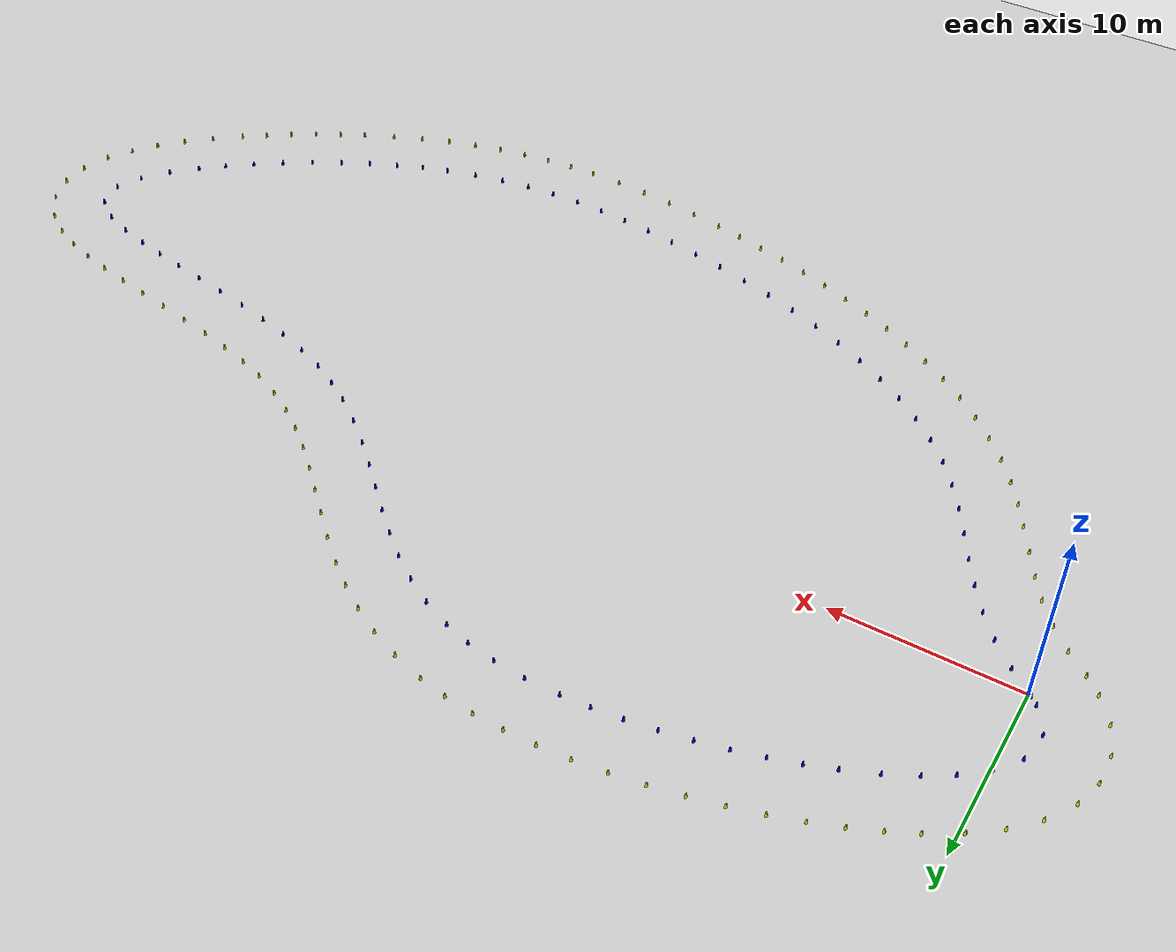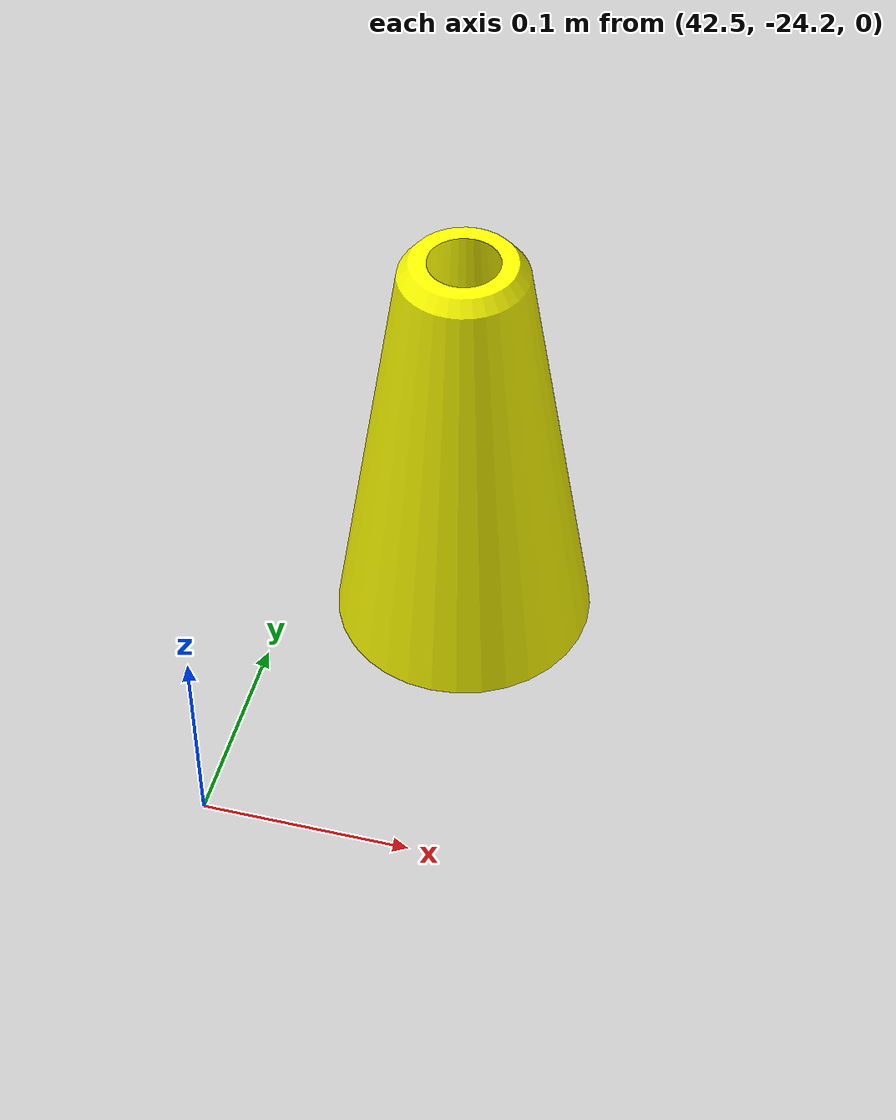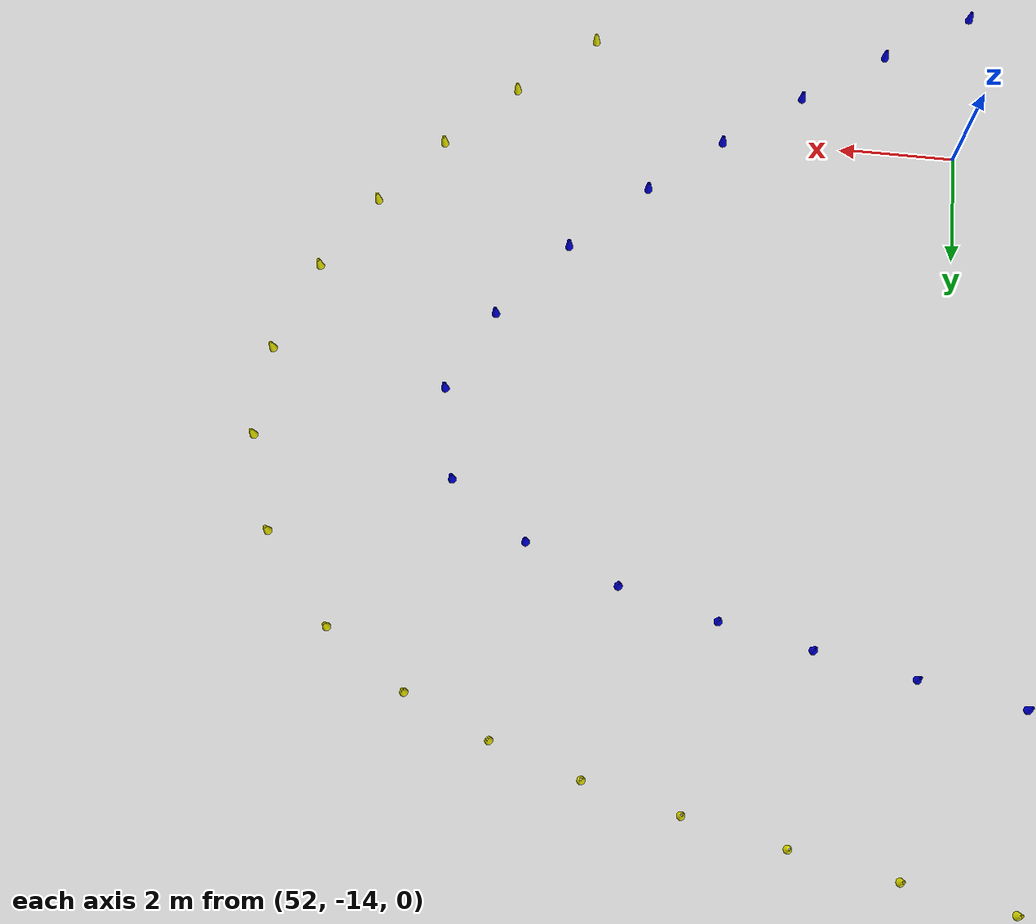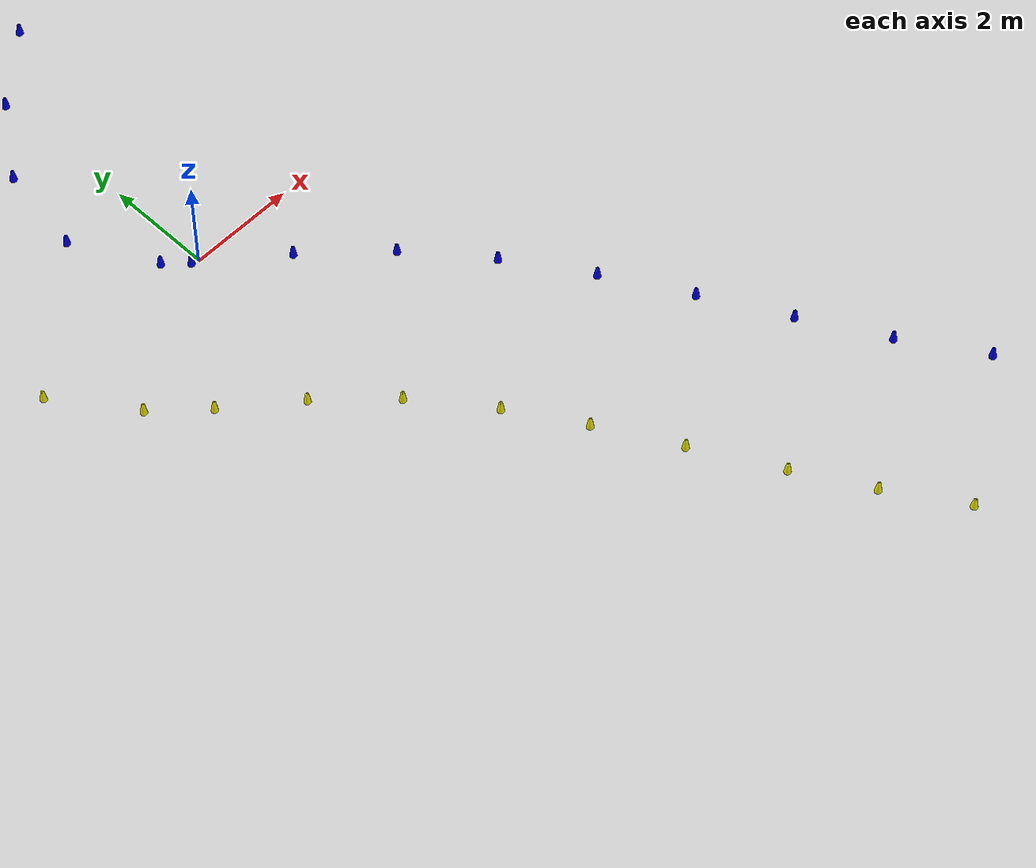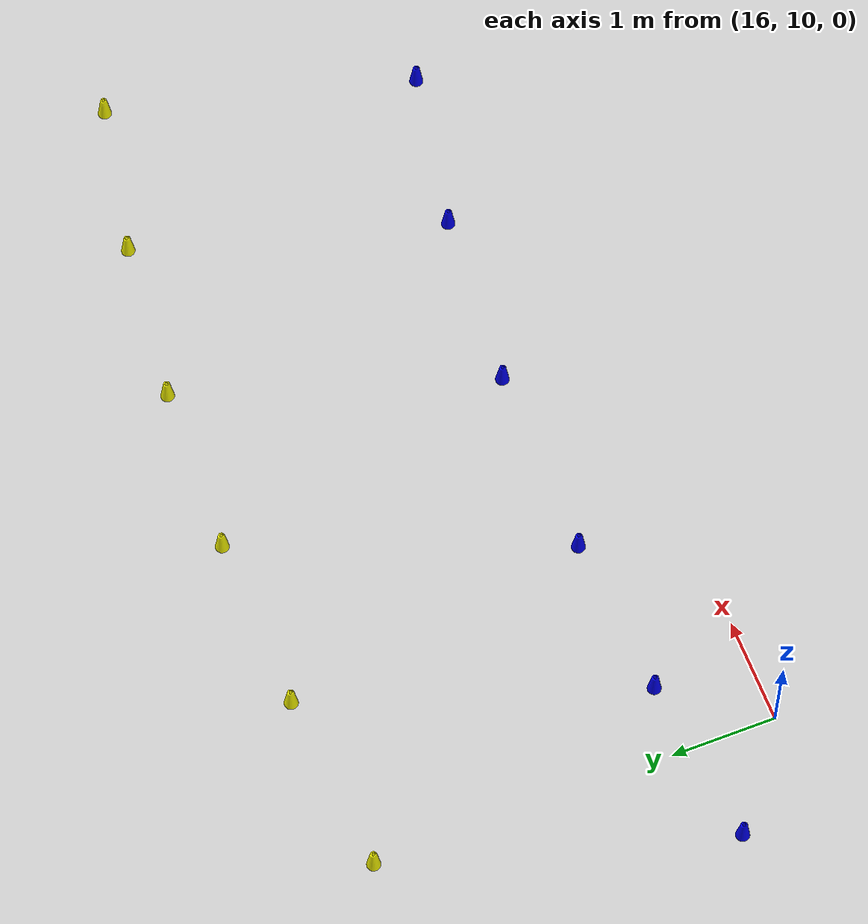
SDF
<sdf version="1.8">
 <world name="sim">
  <physics name="1ms" type="ignored">
   <max_step_size>0.001</max_step_size>
   <real_time_factor>1.0</real_time_factor>
  </physics>
  <plugin filename="libignition-gazebo-physics-system.so" name="ignition::gazebo::systems::Physics"/>
  <plugin filename="libignition-gazebo-user-commands-system.so" name="ignition::gazebo::systems::UserCommands"/>
  <plugin filename="libignition-gazebo-scene-broadcaster-system.so" name="ignition::gazebo::systems::SceneBroadcaster"/>
  <light type="directional" name="sun">
   <pose>0 0 10 0 0 0</pose>
   <diffuse>0.8 0.8 0.8 1</diffuse>
   <specular>0.2 0.2 0.2 1</specular>
   <attenuation>
    <range>1000</range>
    <constant>0.9</constant>
    <linear>0.01</linear>
    <quadratic>0.001</quadratic>
   </attenuation>
   <direction>-0.5 0.1 -0.9</direction>
  </light>
  <model name="ground_plane">
   <static>true</static>
   <link name="link">
    <collision name="collision"><geometry><plane><normal>0 0 0</normal></plane></geometry></collision>
    <visual name="visual">
     <geometry><plane><normal>0 0 1</normal><size>1000 1000</size></plane></geometry>
     <material>
      <ambient>0.8 0.8 0.8 1</ambient>
      <diffuse>0.8 0.8 0.8 1</diffuse>
      <specular>0.8 0.8 0.8 1</specular>
     </material>
    </visual>
   </link>
  </model>
  <plugin filename="libignition-gazebo-sensors-system.so" name="ignition::gazebo::systems::Sensors">
   <render_engine>ogre2</render_engine>
  </plugin>
  <model name="cone_0">
   <static>true</static>
   <pose>-0.501839524610551 0.404460046972835 0 0 0 0</pose>
   <link name="cone_link">
    <inertial>
     <mass>0.14395</mass>
     <inertia><ixx>0.5</ixx><ixy>0</ixy><ixz>0</ixz><iyy>0.5</iyy><iyz>0</iyz><izz>0.5</izz></inertia>
    </inertial>
    <visual name="visual">
     <geometry><mesh><scale>1 1 1</scale><uri>../models/cone_440.stl</uri></mesh></geometry>
     <material>
      <ambient>0.0 0.0 1.0 1</ambient>
      <diffuse>0.0 0.0 1.0 1</diffuse>
      <specular>0.0 0.0 1.0 1</specular>
     </material>
    </visual>
    <collision name="collision"><geometry><mesh><uri>../models/cone_440.stl</uri></mesh></geometry></collision>
    <sensor name="sensor_contact" type="contact"><contact><collision>collision</collision></contact></sensor>
   </link>
  </model>
  <model name="cone_1">
   <static>true</static>
   <pose>-1.321595206293269 1.869856081772146 0 0 0 0</pose>
   <link name="cone_link">
    <inertial>
     <mass>0.14395</mass>
     <inertia><ixx>0.5</ixx><ixy>0</ixy><ixz>0</ixz><iyy>0.5</iyy><iyz>0</iyz><izz>0.5</izz></inertia>
    </inertial>
    <visual name="visual">
     <geometry><mesh><scale>1 1 1</scale><uri>../models/cone_440.stl</uri></mesh></geometry>
     <material>
      <ambient>0.0 0.0 1.0 1</ambient>
      <diffuse>0.0 0.0 1.0 1</diffuse>
      <specular>0.0 0.0 1.0 1</specular>
     </material>
    </visual>
    <collision name="collision"><geometry><mesh><uri>../models/cone_440.stl</uri></mesh></geometry></collision>
    <sensor name="sensor_contact" type="contact"><contact><collision>collision</collision></contact></sensor>
   </link>
  </model>
  <model name="cone_2">
   <static>true</static>
   <pose>-1.050872676349114 3.544081540125663 0 0 0 0</pose>
   <link name="cone_link">
    <inertial>
     <mass>0.14395</mass>
     <inertia><ixx>0.5</ixx><ixy>0</ixy><ixz>0</ixz><iyy>0.5</iyy><iyz>0</iyz><izz>0.5</izz></inertia>
    </inertial>
    <visual name="visual">
     <geometry><mesh><scale>1 1 1</scale><uri>../models/cone_440.stl</uri></mesh></geometry>
     <material>
      <ambient>0.0 0.0 1.0 1</ambient>
      <diffuse>0.0 0.0 1.0 1</diffuse>
      <specular>0.0 0.0 1.0 1</specular>
     </material>
    </visual>
    <collision name="collision"><geometry><mesh><uri>../models/cone_440.stl</uri></mesh></geometry></collision>
    <sensor name="sensor_contact" type="contact"><contact><collision>collision</collision></contact></sensor>
   </link>
  </model>
  <model name="cone_3">
   <static>true</static>
   <pose>-0.091913913027686 4.827807863817258 0 0 0 0</pose>
   <link name="cone_link">
    <inertial>
     <mass>0.14395</mass>
     <inertia><ixx>0.5</ixx><ixy>0</ixy><ixz>0</ixz><iyy>0.5</iyy><iyz>0</iyz><izz>0.5</izz></inertia>
    </inertial>
    <visual name="visual">
     <geometry><mesh><scale>1 1 1</scale><uri>../models/cone_440.stl</uri></mesh></geometry>
     <material>
      <ambient>0.0 0.0 1.0 1</ambient>
      <diffuse>0.0 0.0 1.0 1</diffuse>
      <specular>0.0 0.0 1.0 1</specular>
     </material>
    </visual>
    <collision name="collision"><geometry><mesh><uri>../models/cone_440.stl</uri></mesh></geometry></collision>
    <sensor name="sensor_contact" type="contact"><contact><collision>collision</collision></contact></sensor>
   </link>
  </model>
  <model name="cone_4">
   <static>true</static>
   <pose>1.17153820318694 5.891529484820741 0 0 0 0</pose>
   <link name="cone_link">
    <inertial>
     <mass>0.14395</mass>
     <inertia><ixx>0.5</ixx><ixy>0</ixy><ixz>0</ixz><iyy>0.5</iyy><iyz>0</iyz><izz>0.5</izz></inertia>
    </inertial>
    <visual name="visual">
     <geometry><mesh><scale>1 1 1</scale><uri>../models/cone_440.stl</uri></mesh></geometry>
     <material>
      <ambient>0.0 0.0 1.0 1</ambient>
      <diffuse>0.0 0.0 1.0 1</diffuse>
      <specular>0.0 0.0 1.0 1</specular>
     </material>
    </visual>
    <collision name="collision"><geometry><mesh><uri>../models/cone_440.stl</uri></mesh></geometry></collision>
    <sensor name="sensor_contact" type="contact"><contact><collision>collision</collision></contact></sensor>
   </link>
  </model>
  <model name="cone_5">
   <static>true</static>
   <pose>2.4897293922036488 6.738434126974204 0 0 0 0</pose>
   <link name="cone_link">
    <inertial>
     <mass>0.14395</mass>
     <inertia><ixx>0.5</ixx><ixy>0</ixy><ixz>0</ixz><iyy>0.5</iyy><iyz>0</iyz><izz>0.5</izz></inertia>
    </inertial>
    <visual name="visual">
     <geometry><mesh><scale>1 1 1</scale><uri>../models/cone_440.stl</uri></mesh></geometry>
     <material>
      <ambient>0.0 0.0 1.0 1</ambient>
      <diffuse>0.0 0.0 1.0 1</diffuse>
      <specular>0.0 0.0 1.0 1</specular>
     </material>
    </visual>
    <collision name="collision"><geometry><mesh><uri>../models/cone_440.stl</uri></mesh></geometry></collision>
    <sensor name="sensor_contact" type="contact"><contact><collision>collision</collision></contact></sensor>
   </link>
  </model>
  <model name="cone_6">
   <static>true</static>
   <pose>4.011951201481659 7.538322276705568 0 0 0 0</pose>
   <link name="cone_link">
    <inertial>
     <mass>0.14395</mass>
     <inertia><ixx>0.5</ixx><ixy>0</ixy><ixz>0</ixz><iyy>0.5</iyy><iyz>0</iyz><izz>0.5</izz></inertia>
    </inertial>
    <visual name="visual">
     <geometry><mesh><scale>1 1 1</scale><uri>../models/cone_440.stl</uri></mesh></geometry>
     <material>
      <ambient>0.0 0.0 1.0 1</ambient>
      <diffuse>0.0 0.0 1.0 1</diffuse>
      <specular>0.0 0.0 1.0 1</specular>
     </material>
    </visual>
    <collision name="collision"><geometry><mesh><uri>../models/cone_440.stl</uri></mesh></geometry></collision>
    <sensor name="sensor_contact" type="contact"><contact><collision>collision</collision></contact></sensor>
   </link>
  </model>
  <model name="cone_7">
   <static>true</static>
   <pose>5.703362088506413 8.280806349087385 0 0 0 0</pose>
   <link name="cone_link">
    <inertial>
     <mass>0.14395</mass>
     <inertia><ixx>0.5</ixx><ixy>0</ixy><ixz>0</ixz><iyy>0.5</iyy><iyz>0</iyz><izz>0.5</izz></inertia>
    </inertial>
    <visual name="visual">
     <geometry><mesh><scale>1 1 1</scale><uri>../models/cone_440.stl</uri></mesh></geometry>
     <material>
      <ambient>0.0 0.0 1.0 1</ambient>
      <diffuse>0.0 0.0 1.0 1</diffuse>
      <specular>0.0 0.0 1.0 1</specular>
     </material>
    </visual>
    <collision name="collision"><geometry><mesh><uri>../models/cone_440.stl</uri></mesh></geometry></collision>
    <sensor name="sensor_contact" type="contact"><contact><collision>collision</collision></contact></sensor>
   </link>
  </model>
  <model name="cone_8">
   <static>true</static>
   <pose>7.154893417534084 8.826482214229923 0 0 0 0</pose>
   <link name="cone_link">
    <inertial>
     <mass>0.14395</mass>
     <inertia><ixx>0.5</ixx><ixy>0</ixy><ixz>0</ixz><iyy>0.5</iyy><iyz>0</iyz><izz>0.5</izz></inertia>
    </inertial>
    <visual name="visual">
     <geometry><mesh><scale>1 1 1</scale><uri>../models/cone_440.stl</uri></mesh></geometry>
     <material>
      <ambient>0.0 0.0 1.0 1</ambient>
      <diffuse>0.0 0.0 1.0 1</diffuse>
      <specular>0.0 0.0 1.0 1</specular>
     </material>
    </visual>
    <collision name="collision"><geometry><mesh><uri>../models/cone_440.stl</uri></mesh></geometry></collision>
    <sensor name="sensor_contact" type="contact"><contact><collision>collision</collision></contact></sensor>
   </link>
  </model>
  <model name="cone_9">
   <static>true</static>
   <pose>8.674568299342901 9.323452972032339 0 0 0 0</pose>
   <link name="cone_link">
    <inertial>
     <mass>0.14395</mass>
     <inertia><ixx>0.5</ixx><ixy>0</ixy><ixz>0</ixz><iyy>0.5</iyy><iyz>0</iyz><izz>0.5</izz></inertia>
    </inertial>
    <visual name="visual">
     <geometry><mesh><scale>1 1 1</scale><uri>../models/cone_440.stl</uri></mesh></geometry>
     <material>
      <ambient>0.0 0.0 1.0 1</ambient>
      <diffuse>0.0 0.0 1.0 1</diffuse>
      <specular>0.0 0.0 1.0 1</specular>
     </material>
    </visual>
    <collision name="collision"><geometry><mesh><uri>../models/cone_440.stl</uri></mesh></geometry></collision>
    <sensor name="sensor_contact" type="contact"><contact><collision>collision</collision></contact></sensor>
   </link>
  </model>
  <model name="cone_10">
   <static>true</static>
   <pose>10.244547864165401 9.766400179011768 0 0 0 0</pose>
   <link name="cone_link">
    <inertial>
     <mass>0.14395</mass>
     <inertia><ixx>0.5</ixx><ixy>0</ixy><ixz>0</ixz><iyy>0.5</iyy><iyz>0</iyz><izz>0.5</izz></inertia>
    </inertial>
    <visual name="visual">
     <geometry><mesh><scale>1 1 1</scale><uri>../models/cone_440.stl</uri></mesh></geometry>
     <material>
      <ambient>0.0 0.0 1.0 1</ambient>
      <diffuse>0.0 0.0 1.0 1</diffuse>
      <specular>0.0 0.0 1.0 1</specular>
     </material>
    </visual>
    <collision name="collision"><geometry><mesh><uri>../models/cone_440.stl</uri></mesh></geometry></collision>
    <sensor name="sensor_contact" type="contact"><contact><collision>collision</collision></contact></sensor>
   </link>
  </model>
  <model name="cone_11">
   <static>true</static>
   <pose>11.846993242234134 10.150005391685372 0 0 0 0</pose>
   <link name="cone_link">
    <inertial>
     <mass>0.14395</mass>
     <inertia><ixx>0.5</ixx><ixy>0</ixy><ixz>0</ixz><iyy>0.5</iyy><iyz>0</iyz><izz>0.5</izz></inertia>
    </inertial>
    <visual name="visual">
     <geometry><mesh><scale>1 1 1</scale><uri>../models/cone_440.stl</uri></mesh></geometry>
     <material>
      <ambient>0.0 0.0 1.0 1</ambient>
      <diffuse>0.0 0.0 1.0 1</diffuse>
      <specular>0.0 0.0 1.0 1</specular>
     </material>
    </visual>
    <collision name="collision"><geometry><mesh><uri>../models/cone_440.stl</uri></mesh></geometry></collision>
    <sensor name="sensor_contact" type="contact"><contact><collision>collision</collision></contact></sensor>
   </link>
  </model>
  <model name="cone_12">
   <static>true</static>
   <pose>13.464065563781649 10.468950166570295 0 0 0 0</pose>
   <link name="cone_link">
    <inertial>
     <mass>0.14395</mass>
     <inertia><ixx>0.5</ixx><ixy>0</ixy><ixz>0</ixz><iyy>0.5</iyy><iyz>0</iyz><izz>0.5</izz></inertia>
    </inertial>
    <visual name="visual">
     <geometry><mesh><scale>1 1 1</scale><uri>../models/cone_440.stl</uri></mesh></geometry>
     <material>
      <ambient>0.0 0.0 1.0 1</ambient>
      <diffuse>0.0 0.0 1.0 1</diffuse>
      <specular>0.0 0.0 1.0 1</specular>
     </material>
    </visual>
    <collision name="collision"><geometry><mesh><uri>../models/cone_440.stl</uri></mesh></geometry></collision>
    <sensor name="sensor_contact" type="contact"><contact><collision>collision</collision></contact></sensor>
   </link>
  </model>
  <model name="cone_13">
   <static>true</static>
   <pose>15.07792595904048 10.717916060183681 0 0 0 0</pose>
   <link name="cone_link">
    <inertial>
     <mass>0.14395</mass>
     <inertia><ixx>0.5</ixx><ixy>0</ixy><ixz>0</ixz><iyy>0.5</iyy><iyz>0</iyz><izz>0.5</izz></inertia>
    </inertial>
    <visual name="visual">
     <geometry><mesh><scale>1 1 1</scale><uri>../models/cone_440.stl</uri></mesh></geometry>
     <material>
      <ambient>0.0 0.0 1.0 1</ambient>
      <diffuse>0.0 0.0 1.0 1</diffuse>
      <specular>0.0 0.0 1.0 1</specular>
     </material>
    </visual>
    <collision name="collision"><geometry><mesh><uri>../models/cone_440.stl</uri></mesh></geometry></collision>
    <sensor name="sensor_contact" type="contact"><contact><collision>collision</collision></contact></sensor>
   </link>
  </model>
  <model name="cone_14">
   <static>true</static>
   <pose>16.670735558243173 10.891584629042674 0 0 0 0</pose>
   <link name="cone_link">
    <inertial>
     <mass>0.14395</mass>
     <inertia><ixx>0.5</ixx><ixy>0</ixy><ixz>0</ixz><iyy>0.5</iyy><iyz>0</iyz><izz>0.5</izz></inertia>
    </inertial>
    <visual name="visual">
     <geometry><mesh><scale>1 1 1</scale><uri>../models/cone_440.stl</uri></mesh></geometry>
     <material>
      <ambient>0.0 0.0 1.0 1</ambient>
      <diffuse>0.0 0.0 1.0 1</diffuse>
      <specular>0.0 0.0 1.0 1</specular>
     </material>
    </visual>
    <collision name="collision"><geometry><mesh><uri>../models/cone_440.stl</uri></mesh></geometry></collision>
    <sensor name="sensor_contact" type="contact"><contact><collision>collision</collision></contact></sensor>
   </link>
  </model>
  <model name="cone_15">
   <static>true</static>
   <pose>18.224655491622286 10.984637429664431 0 0 0 0</pose>
   <link name="cone_link">
    <inertial>
     <mass>0.14395</mass>
     <inertia><ixx>0.5</ixx><ixy>0</ixy><ixz>0</ixz><iyy>0.5</iyy><iyz>0</iyz><izz>0.5</izz></inertia>
    </inertial>
    <visual name="visual">
     <geometry><mesh><scale>1 1 1</scale><uri>../models/cone_440.stl</uri></mesh></geometry>
     <material>
      <ambient>0.0 0.0 1.0 1</ambient>
      <diffuse>0.0 0.0 1.0 1</diffuse>
      <specular>0.0 0.0 1.0 1</specular>
     </material>
    </visual>
    <collision name="collision"><geometry><mesh><uri>../models/cone_440.stl</uri></mesh></geometry></collision>
    <sensor name="sensor_contact" type="contact"><contact><collision>collision</collision></contact></sensor>
   </link>
  </model>
  <model name="cone_16">
   <static>true</static>
   <pose>20.085190412620406 10.979485190114605 0 0 0 0</pose>
   <link name="cone_link">
    <inertial>
     <mass>0.14395</mass>
     <inertia><ixx>0.5</ixx><ixy>0</ixy><ixz>0</ixz><iyy>0.5</iyy><iyz>0</iyz><izz>0.5</izz></inertia>
    </inertial>
    <visual name="visual">
     <geometry><mesh><scale>1 1 1</scale><uri>../models/cone_440.stl</uri></mesh></geometry>
     <material>
      <ambient>0.0 0.0 1.0 1</ambient>
      <diffuse>0.0 0.0 1.0 1</diffuse>
      <specular>0.0 0.0 1.0 1</specular>
     </material>
    </visual>
    <collision name="collision"><geometry><mesh><uri>../models/cone_440.stl</uri></mesh></geometry></collision>
    <sensor name="sensor_contact" type="contact"><contact><collision>collision</collision></contact></sensor>
   </link>
  </model>
  <model name="cone_17">
   <static>true</static>
   <pose>21.82224546818126 10.829673166732313 0 0 0 0</pose>
   <link name="cone_link">
    <inertial>
     <mass>0.14395</mass>
     <inertia><ixx>0.5</ixx><ixy>0</ixy><ixz>0</ixz><iyy>0.5</iyy><iyz>0</iyz><izz>0.5</izz></inertia>
    </inertial>
    <visual name="visual">
     <geometry><mesh><scale>1 1 1</scale><uri>../models/cone_440.stl</uri></mesh></geometry>
     <material>
      <ambient>0.0 0.0 1.0 1</ambient>
      <diffuse>0.0 0.0 1.0 1</diffuse>
      <specular>0.0 0.0 1.0 1</specular>
     </material>
    </visual>
    <collision name="collision"><geometry><mesh><uri>../models/cone_440.stl</uri></mesh></geometry></collision>
    <sensor name="sensor_contact" type="contact"><contact><collision>collision</collision></contact></sensor>
   </link>
  </model>
  <model name="cone_18">
   <static>true</static>
   <pose>23.41011242135313 10.529340110433612 0 0 0 0</pose>
   <link name="cone_link">
    <inertial>
     <mass>0.14395</mass>
     <inertia><ixx>0.5</ixx><ixy>0</ixy><ixz>0</ixz><iyy>0.5</iyy><iyz>0</iyz><izz>0.5</izz></inertia>
    </inertial>
    <visual name="visual">
     <geometry><mesh><scale>1 1 1</scale><uri>../models/cone_440.stl</uri></mesh></geometry>
     <material>
      <ambient>0.0 0.0 1.0 1</ambient>
      <diffuse>0.0 0.0 1.0 1</diffuse>
      <specular>0.0 0.0 1.0 1</specular>
     </material>
    </visual>
    <collision name="collision"><geometry><mesh><uri>../models/cone_440.stl</uri></mesh></geometry></collision>
    <sensor name="sensor_contact" type="contact"><contact><collision>collision</collision></contact></sensor>
   </link>
  </model>
  <model name="cone_19">
   <static>true</static>
   <pose>24.858361917620847 10.090108482604162 0 0 0 0</pose>
   <link name="cone_link">
    <inertial>
     <mass>0.14395</mass>
     <inertia><ixx>0.5</ixx><ixy>0</ixy><ixz>0</ixz><iyy>0.5</iyy><iyz>0</iyz><izz>0.5</izz></inertia>
    </inertial>
    <visual name="visual">
     <geometry><mesh><scale>1 1 1</scale><uri>../models/cone_440.stl</uri></mesh></geometry>
     <material>
      <ambient>0.0 0.0 1.0 1</ambient>
      <diffuse>0.0 0.0 1.0 1</diffuse>
      <specular>0.0 0.0 1.0 1</specular>
     </material>
    </visual>
    <collision name="collision"><geometry><mesh><uri>../models/cone_440.stl</uri></mesh></geometry></collision>
    <sensor name="sensor_contact" type="contact"><contact><collision>collision</collision></contact></sensor>
   </link>
  </model>
  <model name="cone_20">
   <static>true</static>
   <pose>26.4374334542188 9.401991763343375 0 0 0 0</pose>
   <link name="cone_link">
    <inertial>
     <mass>0.14395</mass>
     <inertia><ixx>0.5</ixx><ixy>0</ixy><ixz>0</ixz><iyy>0.5</iyy><iyz>0</iyz><izz>0.5</izz></inertia>
    </inertial>
    <visual name="visual">
     <geometry><mesh><scale>1 1 1</scale><uri>../models/cone_440.stl</uri></mesh></geometry>
     <material>
      <ambient>0.0 0.0 1.0 1</ambient>
      <diffuse>0.0 0.0 1.0 1</diffuse>
      <specular>0.0 0.0 1.0 1</specular>
     </material>
    </visual>
    <collision name="collision"><geometry><mesh><uri>../models/cone_440.stl</uri></mesh></geometry></collision>
    <sensor name="sensor_contact" type="contact"><contact><collision>collision</collision></contact></sensor>
   </link>
  </model>
  <model name="cone_21">
   <static>true</static>
   <pose>27.872757017302675 8.56405263532743 0 0 0 0</pose>
   <link name="cone_link">
    <inertial>
     <mass>0.14395</mass>
     <inertia><ixx>0.5</ixx><ixy>0</ixy><ixz>0</ixz><iyy>0.5</iyy><iyz>0</iyz><izz>0.5</izz></inertia>
    </inertial>
    <visual name="visual">
     <geometry><mesh><scale>1 1 1</scale><uri>../models/cone_440.stl</uri></mesh></geometry>
     <material>
      <ambient>0.0 0.0 1.0 1</ambient>
      <diffuse>0.0 0.0 1.0 1</diffuse>
      <specular>0.0 0.0 1.0 1</specular>
     </material>
    </visual>
    <collision name="collision"><geometry><mesh><uri>../models/cone_440.stl</uri></mesh></geometry></collision>
    <sensor name="sensor_contact" type="contact"><contact><collision>collision</collision></contact></sensor>
   </link>
  </model>
  <model name="cone_22">
   <static>true</static>
   <pose>29.19558778746957 7.603668299055839 0 0 0 0</pose>
   <link name="cone_link">
    <inertial>
     <mass>0.14395</mass>
     <inertia><ixx>0.5</ixx><ixy>0</ixy><ixz>0</ixz><iyy>0.5</iyy><iyz>0</iyz><izz>0.5</izz></inertia>
    </inertial>
    <visual name="visual">
     <geometry><mesh><scale>1 1 1</scale><uri>../models/cone_440.stl</uri></mesh></geometry>
     <material>
      <ambient>0.0 0.0 1.0 1</ambient>
      <diffuse>0.0 0.0 1.0 1</diffuse>
      <specular>0.0 0.0 1.0 1</specular>
     </material>
    </visual>
    <collision name="collision"><geometry><mesh><uri>../models/cone_440.stl</uri></mesh></geometry></collision>
    <sensor name="sensor_contact" type="contact"><contact><collision>collision</collision></contact></sensor>
   </link>
  </model>
  <model name="cone_23">
   <static>true</static>
   <pose>30.437180945316534 6.54821595502813 0 0 0 0</pose>
   <link name="cone_link">
    <inertial>
     <mass>0.14395</mass>
     <inertia><ixx>0.5</ixx><ixy>0</ixy><ixz>0</ixz><iyy>0.5</iyy><iyz>0</iyz><izz>0.5</izz></inertia>
    </inertial>
    <visual name="visual">
     <geometry><mesh><scale>1 1 1</scale><uri>../models/cone_440.stl</uri></mesh></geometry>
     <material>
      <ambient>0.0 0.0 1.0 1</ambient>
      <diffuse>0.0 0.0 1.0 1</diffuse>
      <specular>0.0 0.0 1.0 1</specular>
     </material>
    </visual>
    <collision name="collision"><geometry><mesh><uri>../models/cone_440.stl</uri></mesh></geometry></collision>
    <sensor name="sensor_contact" type="contact"><contact><collision>collision</collision></contact></sensor>
   </link>
  </model>
  <model name="cone_24">
   <static>true</static>
   <pose>31.62879167144064 5.425072803743837 0 0 0 0</pose>
   <link name="cone_link">
    <inertial>
     <mass>0.14395</mass>
     <inertia><ixx>0.5</ixx><ixy>0</ixy><ixz>0</ixz><iyy>0.5</iyy><iyz>0</iyz><izz>0.5</izz></inertia>
    </inertial>
    <visual name="visual">
     <geometry><mesh><scale>1 1 1</scale><uri>../models/cone_440.stl</uri></mesh></geometry>
     <material>
      <ambient>0.0 0.0 1.0 1</ambient>
      <diffuse>0.0 0.0 1.0 1</diffuse>
      <specular>0.0 0.0 1.0 1</specular>
     </material>
    </visual>
    <collision name="collision"><geometry><mesh><uri>../models/cone_440.stl</uri></mesh></geometry></collision>
    <sensor name="sensor_contact" type="contact"><contact><collision>collision</collision></contact></sensor>
   </link>
  </model>
  <model name="cone_25">
   <static>true</static>
   <pose>32.80167514643894 4.261616045702469 0 0 0 0</pose>
   <link name="cone_link">
    <inertial>
     <mass>0.14395</mass>
     <inertia><ixx>0.5</ixx><ixy>0</ixy><ixz>0</ixz><iyy>0.5</iyy><iyz>0</iyz><izz>0.5</izz></inertia>
    </inertial>
    <visual name="visual">
     <geometry><mesh><scale>1 1 1</scale><uri>../models/cone_440.stl</uri></mesh></geometry>
     <material>
      <ambient>0.0 0.0 1.0 1</ambient>
      <diffuse>0.0 0.0 1.0 1</diffuse>
      <specular>0.0 0.0 1.0 1</specular>
     </material>
    </visual>
    <collision name="collision"><geometry><mesh><uri>../models/cone_440.stl</uri></mesh></geometry></collision>
    <sensor name="sensor_contact" type="contact"><contact><collision>collision</collision></contact></sensor>
   </link>
  </model>
  <model name="cone_26">
   <static>true</static>
   <pose>33.987086550908515 3.0852228814035647 0 0 0 0</pose>
   <link name="cone_link">
    <inertial>
     <mass>0.14395</mass>
     <inertia><ixx>0.5</ixx><ixy>0</ixy><ixz>0</ixz><iyy>0.5</iyy><iyz>0</iyz><izz>0.5</izz></inertia>
    </inertial>
    <visual name="visual">
     <geometry><mesh><scale>1 1 1</scale><uri>../models/cone_440.stl</uri></mesh></geometry>
     <material>
      <ambient>0.0 0.0 1.0 1</ambient>
      <diffuse>0.0 0.0 1.0 1</diffuse>
      <specular>0.0 0.0 1.0 1</specular>
     </material>
    </visual>
    <collision name="collision"><geometry><mesh><uri>../models/cone_440.stl</uri></mesh></geometry></collision>
    <sensor name="sensor_contact" type="contact"><contact><collision>collision</collision></contact></sensor>
   </link>
  </model>
  <model name="cone_27">
   <static>true</static>
   <pose>35.21628106544644 1.9232705113466468 0 0 0 0</pose>
   <link name="cone_link">
    <inertial>
     <mass>0.14395</mass>
     <inertia><ixx>0.5</ixx><ixy>0</ixy><ixz>0</ixz><iyy>0.5</iyy><iyz>0</iyz><izz>0.5</izz></inertia>
    </inertial>
    <visual name="visual">
     <geometry><mesh><scale>1 1 1</scale><uri>../models/cone_440.stl</uri></mesh></geometry>
     <material>
      <ambient>0.0 0.0 1.0 1</ambient>
      <diffuse>0.0 0.0 1.0 1</diffuse>
      <specular>0.0 0.0 1.0 1</specular>
     </material>
    </visual>
    <collision name="collision"><geometry><mesh><uri>../models/cone_440.stl</uri></mesh></geometry></collision>
    <sensor name="sensor_contact" type="contact"><contact><collision>collision</collision></contact></sensor>
   </link>
  </model>
  <model name="cone_28">
   <static>true</static>
   <pose>36.52051387064975 0.803136136031234 0 0 0 0</pose>
   <link name="cone_link">
    <inertial>
     <mass>0.14395</mass>
     <inertia><ixx>0.5</ixx><ixy>0</ixy><ixz>0</ixz><iyy>0.5</iyy><iyz>0</iyz><izz>0.5</izz></inertia>
    </inertial>
    <visual name="visual">
     <geometry><mesh><scale>1 1 1</scale><uri>../models/cone_440.stl</uri></mesh></geometry>
     <material>
      <ambient>0.0 0.0 1.0 1</ambient>
      <diffuse>0.0 0.0 1.0 1</diffuse>
      <specular>0.0 0.0 1.0 1</specular>
     </material>
    </visual>
    <collision name="collision"><geometry><mesh><uri>../models/cone_440.stl</uri></mesh></geometry></collision>
    <sensor name="sensor_contact" type="contact"><contact><collision>collision</collision></contact></sensor>
   </link>
  </model>
  <model name="cone_29">
   <static>true</static>
   <pose>37.93104014711554 -0.247803044043146 0 0 0 0</pose>
   <link name="cone_link">
    <inertial>
     <mass>0.14395</mass>
     <inertia><ixx>0.5</ixx><ixy>0</ixy><ixz>0</ixz><iyy>0.5</iyy><iyz>0</iyz><izz>0.5</izz></inertia>
    </inertial>
    <visual name="visual">
     <geometry><mesh><scale>1 1 1</scale><uri>../models/cone_440.stl</uri></mesh></geometry>
     <material>
      <ambient>0.0 0.0 1.0 1</ambient>
      <diffuse>0.0 0.0 1.0 1</diffuse>
      <specular>0.0 0.0 1.0 1</specular>
     </material>
    </visual>
    <collision name="collision"><geometry><mesh><uri>../models/cone_440.stl</uri></mesh></geometry></collision>
    <sensor name="sensor_contact" type="contact"><contact><collision>collision</collision></contact></sensor>
   </link>
  </model>
  <model name="cone_30">
   <static>true</static>
   <pose>39.21022418183094 -1.0509769550961199 0 0 0 0</pose>
   <link name="cone_link">
    <inertial>
     <mass>0.14395</mass>
     <inertia><ixx>0.5</ixx><ixy>0</ixy><ixz>0</ixz><iyy>0.5</iyy><iyz>0</iyz><izz>0.5</izz></inertia>
    </inertial>
    <visual name="visual">
     <geometry><mesh><scale>1 1 1</scale><uri>../models/cone_440.stl</uri></mesh></geometry>
     <material>
      <ambient>0.0 0.0 1.0 1</ambient>
      <diffuse>0.0 0.0 1.0 1</diffuse>
      <specular>0.0 0.0 1.0 1</specular>
     </material>
    </visual>
    <collision name="collision"><geometry><mesh><uri>../models/cone_440.stl</uri></mesh></geometry></collision>
    <sensor name="sensor_contact" type="contact"><contact><collision>collision</collision></contact></sensor>
   </link>
  </model>
  <model name="cone_31">
   <static>true</static>
   <pose>40.60301560244245 -1.771243415114254 0 0 0 0</pose>
   <link name="cone_link">
    <inertial>
     <mass>0.14395</mass>
     <inertia><ixx>0.5</ixx><ixy>0</ixy><ixz>0</ixz><iyy>0.5</iyy><iyz>0</iyz><izz>0.5</izz></inertia>
    </inertial>
    <visual name="visual">
     <geometry><mesh><scale>1 1 1</scale><uri>../models/cone_440.stl</uri></mesh></geometry>
     <material>
      <ambient>0.0 0.0 1.0 1</ambient>
      <diffuse>0.0 0.0 1.0 1</diffuse>
      <specular>0.0 0.0 1.0 1</specular>
     </material>
    </visual>
    <collision name="collision"><geometry><mesh><uri>../models/cone_440.stl</uri></mesh></geometry></collision>
    <sensor name="sensor_contact" type="contact"><contact><collision>collision</collision></contact></sensor>
   </link>
  </model>
  <model name="cone_32">
   <static>true</static>
   <pose>42.123545319236385 -2.395179536394365 0 0 0 0</pose>
   <link name="cone_link">
    <inertial>
     <mass>0.14395</mass>
     <inertia><ixx>0.5</ixx><ixy>0</ixy><ixz>0</ixz><iyy>0.5</iyy><iyz>0</iyz><izz>0.5</izz></inertia>
    </inertial>
    <visual name="visual">
     <geometry><mesh><scale>1 1 1</scale><uri>../models/cone_440.stl</uri></mesh></geometry>
     <material>
      <ambient>0.0 0.0 1.0 1</ambient>
      <diffuse>0.0 0.0 1.0 1</diffuse>
      <specular>0.0 0.0 1.0 1</specular>
     </material>
    </visual>
    <collision name="collision"><geometry><mesh><uri>../models/cone_440.stl</uri></mesh></geometry></collision>
    <sensor name="sensor_contact" type="contact"><contact><collision>collision</collision></contact></sensor>
   </link>
  </model>
  <model name="cone_33">
   <static>true</static>
   <pose>43.754646026154006 -2.9285088202974507 0 0 0 0</pose>
   <link name="cone_link">
    <inertial>
     <mass>0.14395</mass>
     <inertia><ixx>0.5</ixx><ixy>0</ixy><ixz>0</ixz><iyy>0.5</iyy><iyz>0</iyz><izz>0.5</izz></inertia>
    </inertial>
    <visual name="visual">
     <geometry><mesh><scale>1 1 1</scale><uri>../models/cone_440.stl</uri></mesh></geometry>
     <material>
      <ambient>0.0 0.0 1.0 1</ambient>
      <diffuse>0.0 0.0 1.0 1</diffuse>
      <specular>0.0 0.0 1.0 1</specular>
     </material>
    </visual>
    <collision name="collision"><geometry><mesh><uri>../models/cone_440.stl</uri></mesh></geometry></collision>
    <sensor name="sensor_contact" type="contact"><contact><collision>collision</collision></contact></sensor>
   </link>
  </model>
  <model name="cone_34">
   <static>true</static>
   <pose>45.46427523637484 -3.3860545199123058 0 0 0 0</pose>
   <link name="cone_link">
    <inertial>
     <mass>0.14395</mass>
     <inertia><ixx>0.5</ixx><ixy>0</ixy><ixz>0</ixz><iyy>0.5</iyy><iyz>0</iyz><izz>0.5</izz></inertia>
    </inertial>
    <visual name="visual">
     <geometry><mesh><scale>1 1 1</scale><uri>../models/cone_440.stl</uri></mesh></geometry>
     <material>
      <ambient>0.0 0.0 1.0 1</ambient>
      <diffuse>0.0 0.0 1.0 1</diffuse>
      <specular>0.0 0.0 1.0 1</specular>
     </material>
    </visual>
    <collision name="collision"><geometry><mesh><uri>../models/cone_440.stl</uri></mesh></geometry></collision>
    <sensor name="sensor_contact" type="contact"><contact><collision>collision</collision></contact></sensor>
   </link>
  </model>
  <model name="cone_35">
   <static>true</static>
   <pose>47.22030010249203 -3.782695165565446 0 0 0 0</pose>
   <link name="cone_link">
    <inertial>
     <mass>0.14395</mass>
     <inertia><ixx>0.5</ixx><ixy>0</ixy><ixz>0</ixz><iyy>0.5</iyy><iyz>0</iyz><izz>0.5</izz></inertia>
    </inertial>
    <visual name="visual">
     <geometry><mesh><scale>1 1 1</scale><uri>../models/cone_440.stl</uri></mesh></geometry>
     <material>
      <ambient>0.0 0.0 1.0 1</ambient>
      <diffuse>0.0 0.0 1.0 1</diffuse>
      <specular>0.0 0.0 1.0 1</specular>
     </material>
    </visual>
    <collision name="collision"><geometry><mesh><uri>../models/cone_440.stl</uri></mesh></geometry></collision>
    <sensor name="sensor_contact" type="contact"><contact><collision>collision</collision></contact></sensor>
   </link>
  </model>
  <model name="cone_36">
   <static>true</static>
   <pose>48.99058777709864 -4.13330928758337 0 0 0 0</pose>
   <link name="cone_link">
    <inertial>
     <mass>0.14395</mass>
     <inertia><ixx>0.5</ixx><ixy>0</ixy><ixz>0</ixz><iyy>0.5</iyy><iyz>0</iyz><izz>0.5</izz></inertia>
    </inertial>
    <visual name="visual">
     <geometry><mesh><scale>1 1 1</scale><uri>../models/cone_440.stl</uri></mesh></geometry>
     <material>
      <ambient>0.0 0.0 1.0 1</ambient>
      <diffuse>0.0 0.0 1.0 1</diffuse>
      <specular>0.0 0.0 1.0 1</specular>
     </material>
    </visual>
    <collision name="collision"><geometry><mesh><uri>../models/cone_440.stl</uri></mesh></geometry></collision>
    <sensor name="sensor_contact" type="contact"><contact><collision>collision</collision></contact></sensor>
   </link>
  </model>
  <model name="cone_37">
   <static>true</static>
   <pose>50.74300541278778 -4.4527754162925905 0 0 0 0</pose>
   <link name="cone_link">
    <inertial>
     <mass>0.14395</mass>
     <inertia><ixx>0.5</ixx><ixy>0</ixy><ixz>0</ixz><iyy>0.5</iyy><iyz>0</iyz><izz>0.5</izz></inertia>
    </inertial>
    <visual name="visual">
     <geometry><mesh><scale>1 1 1</scale><uri>../models/cone_440.stl</uri></mesh></geometry>
     <material>
      <ambient>0.0 0.0 1.0 1</ambient>
      <diffuse>0.0 0.0 1.0 1</diffuse>
      <specular>0.0 0.0 1.0 1</specular>
     </material>
    </visual>
    <collision name="collision"><geometry><mesh><uri>../models/cone_440.stl</uri></mesh></geometry></collision>
    <sensor name="sensor_contact" type="contact"><contact><collision>collision</collision></contact></sensor>
   </link>
  </model>
  <model name="cone_38">
   <static>true</static>
   <pose>52.44542016215256 -4.755972082019614 0 0 0 0</pose>
   <link name="cone_link">
    <inertial>
     <mass>0.14395</mass>
     <inertia><ixx>0.5</ixx><ixy>0</ixy><ixz>0</ixz><iyy>0.5</iyy><iyz>0</iyz><izz>0.5</izz></inertia>
    </inertial>
    <visual name="visual">
     <geometry><mesh><scale>1 1 1</scale><uri>../models/cone_440.stl</uri></mesh></geometry>
     <material>
      <ambient>0.0 0.0 1.0 1</ambient>
      <diffuse>0.0 0.0 1.0 1</diffuse>
      <specular>0.0 0.0 1.0 1</specular>
     </material>
    </visual>
    <collision name="collision"><geometry><mesh><uri>../models/cone_440.stl</uri></mesh></geometry></collision>
    <sensor name="sensor_contact" type="contact"><contact><collision>collision</collision></contact></sensor>
   </link>
  </model>
  <model name="cone_39">
   <static>true</static>
   <pose>54.06569917778606 -5.057777815090945 0 0 0 0</pose>
   <link name="cone_link">
    <inertial>
     <mass>0.14395</mass>
     <inertia><ixx>0.5</ixx><ixy>0</ixy><ixz>0</ixz><iyy>0.5</iyy><iyz>0</iyz><izz>0.5</izz></inertia>
    </inertial>
    <visual name="visual">
     <geometry><mesh><scale>1 1 1</scale><uri>../models/cone_440.stl</uri></mesh></geometry>
     <material>
      <ambient>0.0 0.0 1.0 1</ambient>
      <diffuse>0.0 0.0 1.0 1</diffuse>
      <specular>0.0 0.0 1.0 1</specular>
     </material>
    </visual>
    <collision name="collision"><geometry><mesh><uri>../models/cone_440.stl</uri></mesh></geometry></collision>
    <sensor name="sensor_contact" type="contact"><contact><collision>collision</collision></contact></sensor>
   </link>
  </model>
  <model name="cone_40">
   <static>true</static>
   <pose>55.57170961228139 -5.373071145833092 0 0 0 0</pose>
   <link name="cone_link">
    <inertial>
     <mass>0.14395</mass>
     <inertia><ixx>0.5</ixx><ixy>0</ixy><ixz>0</ixz><iyy>0.5</iyy><iyz>0</iyz><izz>0.5</izz></inertia>
    </inertial>
    <visual name="visual">
     <geometry><mesh><scale>1 1 1</scale><uri>../models/cone_440.stl</uri></mesh></geometry>
     <material>
      <ambient>0.0 0.0 1.0 1</ambient>
      <diffuse>0.0 0.0 1.0 1</diffuse>
      <specular>0.0 0.0 1.0 1</specular>
     </material>
    </visual>
    <collision name="collision"><geometry><mesh><uri>../models/cone_440.stl</uri></mesh></geometry></collision>
    <sensor name="sensor_contact" type="contact"><contact><collision>collision</collision></contact></sensor>
   </link>
  </model>
  <model name="cone_41">
   <static>true</static>
   <pose>57.18284455742446 -5.790175742348863 0 0 0 0</pose>
   <link name="cone_link">
    <inertial>
     <mass>0.14395</mass>
     <inertia><ixx>0.5</ixx><ixy>0</ixy><ixz>0</ixz><iyy>0.5</iyy><iyz>0</iyz><izz>0.5</izz></inertia>
    </inertial>
    <visual name="visual">
     <geometry><mesh><scale>1 1 1</scale><uri>../models/cone_440.stl</uri></mesh></geometry>
     <material>
      <ambient>0.0 0.0 1.0 1</ambient>
      <diffuse>0.0 0.0 1.0 1</diffuse>
      <specular>0.0 0.0 1.0 1</specular>
     </material>
    </visual>
    <collision name="collision"><geometry><mesh><uri>../models/cone_440.stl</uri></mesh></geometry></collision>
    <sensor name="sensor_contact" type="contact"><contact><collision>collision</collision></contact></sensor>
   </link>
  </model>
  <model name="cone_42">
   <static>true</static>
   <pose>58.72197446925063 -6.362724096485099 0 0 0 0</pose>
   <link name="cone_link">
    <inertial>
     <mass>0.14395</mass>
     <inertia><ixx>0.5</ixx><ixy>0</ixy><ixz>0</ixz><iyy>0.5</iyy><iyz>0</iyz><izz>0.5</izz></inertia>
    </inertial>
    <visual name="visual">
     <geometry><mesh><scale>1 1 1</scale><uri>../models/cone_440.stl</uri></mesh></geometry>
     <material>
      <ambient>0.0 0.0 1.0 1</ambient>
      <diffuse>0.0 0.0 1.0 1</diffuse>
      <specular>0.0 0.0 1.0 1</specular>
     </material>
    </visual>
    <collision name="collision"><geometry><mesh><uri>../models/cone_440.stl</uri></mesh></geometry></collision>
    <sensor name="sensor_contact" type="contact"><contact><collision>collision</collision></contact></sensor>
   </link>
  </model>
  <model name="cone_43">
   <static>true</static>
   <pose>60.02626989545873 -7.297675934022811 0 0 0 0</pose>
   <link name="cone_link">
    <inertial>
     <mass>0.14395</mass>
     <inertia><ixx>0.5</ixx><ixy>0</ixy><ixz>0</ixz><iyy>0.5</iyy><iyz>0</iyz><izz>0.5</izz></inertia>
    </inertial>
    <visual name="visual">
     <geometry><mesh><scale>1 1 1</scale><uri>../models/cone_440.stl</uri></mesh></geometry>
     <material>
      <ambient>0.0 0.0 1.0 1</ambient>
      <diffuse>0.0 0.0 1.0 1</diffuse>
      <specular>0.0 0.0 1.0 1</specular>
     </material>
    </visual>
    <collision name="collision"><geometry><mesh><uri>../models/cone_440.stl</uri></mesh></geometry></collision>
    <sensor name="sensor_contact" type="contact"><contact><collision>collision</collision></contact></sensor>
   </link>
  </model>
  <model name="cone_44">
   <static>true</static>
   <pose>60.34456406680583 -8.85705027419842 0 0 0 0</pose>
   <link name="cone_link">
    <inertial>
     <mass>0.14395</mass>
     <inertia><ixx>0.5</ixx><ixy>0</ixy><ixz>0</ixz><iyy>0.5</iyy><iyz>0</iyz><izz>0.5</izz></inertia>
    </inertial>
    <visual name="visual">
     <geometry><mesh><scale>1 1 1</scale><uri>../models/cone_440.stl</uri></mesh></geometry>
     <material>
      <ambient>0.0 0.0 1.0 1</ambient>
      <diffuse>0.0 0.0 1.0 1</diffuse>
      <specular>0.0 0.0 1.0 1</specular>
     </material>
    </visual>
    <collision name="collision"><geometry><mesh><uri>../models/cone_440.stl</uri></mesh></geometry></collision>
    <sensor name="sensor_contact" type="contact"><contact><collision>collision</collision></contact></sensor>
   </link>
  </model>
  <model name="cone_45">
   <static>true</static>
   <pose>59.668864798298536 -10.280041291408226 0 0 0 0</pose>
   <link name="cone_link">
    <inertial>
     <mass>0.14395</mass>
     <inertia><ixx>0.5</ixx><ixy>0</ixy><ixz>0</ixz><iyy>0.5</iyy><iyz>0</iyz><izz>0.5</izz></inertia>
    </inertial>
    <visual name="visual">
     <geometry><mesh><scale>1 1 1</scale><uri>../models/cone_440.stl</uri></mesh></geometry>
     <material>
      <ambient>0.0 0.0 1.0 1</ambient>
      <diffuse>0.0 0.0 1.0 1</diffuse>
      <specular>0.0 0.0 1.0 1</specular>
     </material>
    </visual>
    <collision name="collision"><geometry><mesh><uri>../models/cone_440.stl</uri></mesh></geometry></collision>
    <sensor name="sensor_contact" type="contact"><contact><collision>collision</collision></contact></sensor>
   </link>
  </model>
  <model name="cone_46">
   <static>true</static>
   <pose>58.559149127004446 -11.65900997355598 0 0 0 0</pose>
   <link name="cone_link">
    <inertial>
     <mass>0.14395</mass>
     <inertia><ixx>0.5</ixx><ixy>0</ixy><ixz>0</ixz><iyy>0.5</iyy><iyz>0</iyz><izz>0.5</izz></inertia>
    </inertial>
    <visual name="visual">
     <geometry><mesh><scale>1 1 1</scale><uri>../models/cone_440.stl</uri></mesh></geometry>
     <material>
      <ambient>0.0 0.0 1.0 1</ambient>
      <diffuse>0.0 0.0 1.0 1</diffuse>
      <specular>0.0 0.0 1.0 1</specular>
     </material>
    </visual>
    <collision name="collision"><geometry><mesh><uri>../models/cone_440.stl</uri></mesh></geometry></collision>
    <sensor name="sensor_contact" type="contact"><contact><collision>collision</collision></contact></sensor>
   </link>
  </model>
  <model name="cone_47">
   <static>true</static>
   <pose>57.294075532158644 -12.897604412700154 0 0 0 0</pose>
   <link name="cone_link">
    <inertial>
     <mass>0.14395</mass>
     <inertia><ixx>0.5</ixx><ixy>0</ixy><ixz>0</ixz><iyy>0.5</iyy><iyz>0</iyz><izz>0.5</izz></inertia>
    </inertial>
    <visual name="visual">
     <geometry><mesh><scale>1 1 1</scale><uri>../models/cone_440.stl</uri></mesh></geometry>
     <material>
      <ambient>0.0 0.0 1.0 1</ambient>
      <diffuse>0.0 0.0 1.0 1</diffuse>
      <specular>0.0 0.0 1.0 1</specular>
     </material>
    </visual>
    <collision name="collision"><geometry><mesh><uri>../models/cone_440.stl</uri></mesh></geometry></collision>
    <sensor name="sensor_contact" type="contact"><contact><collision>collision</collision></contact></sensor>
   </link>
  </model>
  <model name="cone_48">
   <static>true</static>
   <pose>56.06158917118052 -13.943816752823619 0 0 0 0</pose>
   <link name="cone_link">
    <inertial>
     <mass>0.14395</mass>
     <inertia><ixx>0.5</ixx><ixy>0</ixy><ixz>0</ixz><iyy>0.5</iyy><iyz>0</iyz><izz>0.5</izz></inertia>
    </inertial>
    <visual name="visual">
     <geometry><mesh><scale>1 1 1</scale><uri>../models/cone_440.stl</uri></mesh></geometry>
     <material>
      <ambient>0.0 0.0 1.0 1</ambient>
      <diffuse>0.0 0.0 1.0 1</diffuse>
      <specular>0.0 0.0 1.0 1</specular>
     </material>
    </visual>
    <collision name="collision"><geometry><mesh><uri>../models/cone_440.stl</uri></mesh></geometry></collision>
    <sensor name="sensor_contact" type="contact"><contact><collision>collision</collision></contact></sensor>
   </link>
  </model>
  <model name="cone_49">
   <static>true</static>
   <pose>54.70185656634292 -14.981893044283126 0 0 0 0</pose>
   <link name="cone_link">
    <inertial>
     <mass>0.14395</mass>
     <inertia><ixx>0.5</ixx><ixy>0</ixy><ixz>0</ixz><iyy>0.5</iyy><iyz>0</iyz><izz>0.5</izz></inertia>
    </inertial>
    <visual name="visual">
     <geometry><mesh><scale>1 1 1</scale><uri>../models/cone_440.stl</uri></mesh></geometry>
     <material>
      <ambient>0.0 0.0 1.0 1</ambient>
      <diffuse>0.0 0.0 1.0 1</diffuse>
      <specular>0.0 0.0 1.0 1</specular>
     </material>
    </visual>
    <collision name="collision"><geometry><mesh><uri>../models/cone_440.stl</uri></mesh></geometry></collision>
    <sensor name="sensor_contact" type="contact"><contact><collision>collision</collision></contact></sensor>
   </link>
  </model>
  <model name="cone_50">
   <static>true</static>
   <pose>53.247509107158194 -15.992231047561331 0 0 0 0</pose>
   <link name="cone_link">
    <inertial>
     <mass>0.14395</mass>
     <inertia><ixx>0.5</ixx><ixy>0</ixy><ixz>0</ixz><iyy>0.5</iyy><iyz>0</iyz><izz>0.5</izz></inertia>
    </inertial>
    <visual name="visual">
     <geometry><mesh><scale>1 1 1</scale><uri>../models/cone_440.stl</uri></mesh></geometry>
     <material>
      <ambient>0.0 0.0 1.0 1</ambient>
      <diffuse>0.0 0.0 1.0 1</diffuse>
      <specular>0.0 0.0 1.0 1</specular>
     </material>
    </visual>
    <collision name="collision"><geometry><mesh><uri>../models/cone_440.stl</uri></mesh></geometry></collision>
    <sensor name="sensor_contact" type="contact"><contact><collision>collision</collision></contact></sensor>
   </link>
  </model>
  <model name="cone_51">
   <static>true</static>
   <pose>51.73117818313876 -16.9552285231409 0 0 0 0</pose>
   <link name="cone_link">
    <inertial>
     <mass>0.14395</mass>
     <inertia><ixx>0.5</ixx><ixy>0</ixy><ixz>0</ixz><iyy>0.5</iyy><iyz>0</iyz><izz>0.5</izz></inertia>
    </inertial>
    <visual name="visual">
     <geometry><mesh><scale>1 1 1</scale><uri>../models/cone_440.stl</uri></mesh></geometry>
     <material>
      <ambient>0.0 0.0 1.0 1</ambient>
      <diffuse>0.0 0.0 1.0 1</diffuse>
      <specular>0.0 0.0 1.0 1</specular>
     </material>
    </visual>
    <collision name="collision"><geometry><mesh><uri>../models/cone_440.stl</uri></mesh></geometry></collision>
    <sensor name="sensor_contact" type="contact"><contact><collision>collision</collision></contact></sensor>
   </link>
  </model>
  <model name="cone_52">
   <static>true</static>
   <pose>50.18549518379692 -17.851283231504503 0 0 0 0</pose>
   <link name="cone_link">
    <inertial>
     <mass>0.14395</mass>
     <inertia><ixx>0.5</ixx><ixy>0</ixy><ixz>0</ixz><iyy>0.5</iyy><iyz>0</iyz><izz>0.5</izz></inertia>
    </inertial>
    <visual name="visual">
     <geometry><mesh><scale>1 1 1</scale><uri>../models/cone_440.stl</uri></mesh></geometry>
     <material>
      <ambient>0.0 0.0 1.0 1</ambient>
      <diffuse>0.0 0.0 1.0 1</diffuse>
      <specular>0.0 0.0 1.0 1</specular>
     </material>
    </visual>
    <collision name="collision"><geometry><mesh><uri>../models/cone_440.stl</uri></mesh></geometry></collision>
    <sensor name="sensor_contact" type="contact"><contact><collision>collision</collision></contact></sensor>
   </link>
  </model>
  <model name="cone_53">
   <static>true</static>
   <pose>48.64309149864512 -18.660792933134807 0 0 0 0</pose>
   <link name="cone_link">
    <inertial>
     <mass>0.14395</mass>
     <inertia><ixx>0.5</ixx><ixy>0</ixy><ixz>0</ixz><iyy>0.5</iyy><iyz>0</iyz><izz>0.5</izz></inertia>
    </inertial>
    <visual name="visual">
     <geometry><mesh><scale>1 1 1</scale><uri>../models/cone_440.stl</uri></mesh></geometry>
     <material>
      <ambient>0.0 0.0 1.0 1</ambient>
      <diffuse>0.0 0.0 1.0 1</diffuse>
      <specular>0.0 0.0 1.0 1</specular>
     </material>
    </visual>
    <collision name="collision"><geometry><mesh><uri>../models/cone_440.stl</uri></mesh></geometry></collision>
    <sensor name="sensor_contact" type="contact"><contact><collision>collision</collision></contact></sensor>
   </link>
  </model>
  <model name="cone_54">
   <static>true</static>
   <pose>47.13072201594224 -19.36812468905719 0 0 0 0</pose>
   <link name="cone_link">
    <inertial>
     <mass>0.14395</mass>
     <inertia><ixx>0.5</ixx><ixy>0</ixy><ixz>0</ixz><iyy>0.5</iyy><iyz>0</iyz><izz>0.5</izz></inertia>
    </inertial>
    <visual name="visual">
     <geometry><mesh><scale>1 1 1</scale><uri>../models/cone_440.stl</uri></mesh></geometry>
     <material>
      <ambient>0.0 0.0 1.0 1</ambient>
      <diffuse>0.0 0.0 1.0 1</diffuse>
      <specular>0.0 0.0 1.0 1</specular>
     </material>
    </visual>
    <collision name="collision"><geometry><mesh><uri>../models/cone_440.stl</uri></mesh></geometry></collision>
    <sensor name="sensor_contact" type="contact"><contact><collision>collision</collision></contact></sensor>
   </link>
  </model>
  <model name="cone_55">
   <static>true</static>
   <pose>45.650742295588586 -19.9741261604226 0 0 0 0</pose>
   <link name="cone_link">
    <inertial>
     <mass>0.14395</mass>
     <inertia><ixx>0.5</ixx><ixy>0</ixy><ixz>0</ixz><iyy>0.5</iyy><iyz>0</iyz><izz>0.5</izz></inertia>
    </inertial>
    <visual name="visual">
     <geometry><mesh><scale>1 1 1</scale><uri>../models/cone_440.stl</uri></mesh></geometry>
     <material>
      <ambient>0.0 0.0 1.0 1</ambient>
      <diffuse>0.0 0.0 1.0 1</diffuse>
      <specular>0.0 0.0 1.0 1</specular>
     </material>
    </visual>
    <collision name="collision"><geometry><mesh><uri>../models/cone_440.stl</uri></mesh></geometry></collision>
    <sensor name="sensor_contact" type="contact"><contact><collision>collision</collision></contact></sensor>
   </link>
  </model>
  <model name="cone_56">
   <static>true</static>
   <pose>44.19917631211612 -20.48392169686632 0 0 0 0</pose>
   <link name="cone_link">
    <inertial>
     <mass>0.14395</mass>
     <inertia><ixx>0.5</ixx><ixy>0</ixy><ixz>0</ixz><iyy>0.5</iyy><iyz>0</iyz><izz>0.5</izz></inertia>
    </inertial>
    <visual name="visual">
     <geometry><mesh><scale>1 1 1</scale><uri>../models/cone_440.stl</uri></mesh></geometry>
     <material>
      <ambient>0.0 0.0 1.0 1</ambient>
      <diffuse>0.0 0.0 1.0 1</diffuse>
      <specular>0.0 0.0 1.0 1</specular>
     </material>
    </visual>
    <collision name="collision"><geometry><mesh><uri>../models/cone_440.stl</uri></mesh></geometry></collision>
    <sensor name="sensor_contact" type="contact"><contact><collision>collision</collision></contact></sensor>
   </link>
  </model>
  <model name="cone_57">
   <static>true</static>
   <pose>42.48920500426688 -20.97589960193798 0 0 0 0</pose>
   <link name="cone_link">
    <inertial>
     <mass>0.14395</mass>
     <inertia><ixx>0.5</ixx><ixy>0</ixy><ixz>0</ixz><iyy>0.5</iyy><iyz>0</iyz><izz>0.5</izz></inertia>
    </inertial>
    <visual name="visual">
     <geometry><mesh><scale>1 1 1</scale><uri>../models/cone_440.stl</uri></mesh></geometry>
     <material>
      <ambient>0.0 0.0 1.0 1</ambient>
      <diffuse>0.0 0.0 1.0 1</diffuse>
      <specular>0.0 0.0 1.0 1</specular>
     </material>
    </visual>
    <collision name="collision"><geometry><mesh><uri>../models/cone_440.stl</uri></mesh></geometry></collision>
    <sensor name="sensor_contact" type="contact"><contact><collision>collision</collision></contact></sensor>
   </link>
  </model>
  <model name="cone_58">
   <static>true</static>
   <pose>40.80755339170423 -21.345574925453047 0 0 0 0</pose>
   <link name="cone_link">
    <inertial>
     <mass>0.14395</mass>
     <inertia><ixx>0.5</ixx><ixy>0</ixy><ixz>0</ixz><iyy>0.5</iyy><iyz>0</iyz><izz>0.5</izz></inertia>
    </inertial>
    <visual name="visual">
     <geometry><mesh><scale>1 1 1</scale><uri>../models/cone_440.stl</uri></mesh></geometry>
     <material>
      <ambient>0.0 0.0 1.0 1</ambient>
      <diffuse>0.0 0.0 1.0 1</diffuse>
      <specular>0.0 0.0 1.0 1</specular>
     </material>
    </visual>
    <collision name="collision"><geometry><mesh><uri>../models/cone_440.stl</uri></mesh></geometry></collision>
    <sensor name="sensor_contact" type="contact"><contact><collision>collision</collision></contact></sensor>
   </link>
  </model>
  <model name="cone_59">
   <static>true</static>
   <pose>39.14735088216143 -21.60180255726457 0 0 0 0</pose>
   <link name="cone_link">
    <inertial>
     <mass>0.14395</mass>
     <inertia><ixx>0.5</ixx><ixy>0</ixy><ixz>0</ixz><iyy>0.5</iyy><iyz>0</iyz><izz>0.5</izz></inertia>
    </inertial>
    <visual name="visual">
     <geometry><mesh><scale>1 1 1</scale><uri>../models/cone_440.stl</uri></mesh></geometry>
     <material>
      <ambient>0.0 0.0 1.0 1</ambient>
      <diffuse>0.0 0.0 1.0 1</diffuse>
      <specular>0.0 0.0 1.0 1</specular>
     </material>
    </visual>
    <collision name="collision"><geometry><mesh><uri>../models/cone_440.stl</uri></mesh></geometry></collision>
    <sensor name="sensor_contact" type="contact"><contact><collision>collision</collision></contact></sensor>
   </link>
  </model>
  <model name="cone_60">
   <static>true</static>
   <pose>37.501726883371774 -21.75343738722564 0 0 0 0</pose>
   <link name="cone_link">
    <inertial>
     <mass>0.14395</mass>
     <inertia><ixx>0.5</ixx><ixy>0</ixy><ixz>0</ixz><iyy>0.5</iyy><iyz>0</iyz><izz>0.5</izz></inertia>
    </inertial>
    <visual name="visual">
     <geometry><mesh><scale>1 1 1</scale><uri>../models/cone_440.stl</uri></mesh></geometry>
     <material>
      <ambient>0.0 0.0 1.0 1</ambient>
      <diffuse>0.0 0.0 1.0 1</diffuse>
      <specular>0.0 0.0 1.0 1</specular>
     </material>
    </visual>
    <collision name="collision"><geometry><mesh><uri>../models/cone_440.stl</uri></mesh></geometry></collision>
    <sensor name="sensor_contact" type="contact"><contact><collision>collision</collision></contact></sensor>
   </link>
  </model>
  <model name="cone_61">
   <static>true</static>
   <pose>35.86381080306849 -21.80933430518932 0 0 0 0</pose>
   <link name="cone_link">
    <inertial>
     <mass>0.14395</mass>
     <inertia><ixx>0.5</ixx><ixy>0</ixy><ixz>0</ixz><iyy>0.5</iyy><iyz>0</iyz><izz>0.5</izz></inertia>
    </inertial>
    <visual name="visual">
     <geometry><mesh><scale>1 1 1</scale><uri>../models/cone_440.stl</uri></mesh></geometry>
     <material>
      <ambient>0.0 0.0 1.0 1</ambient>
      <diffuse>0.0 0.0 1.0 1</diffuse>
      <specular>0.0 0.0 1.0 1</specular>
     </material>
    </visual>
    <collision name="collision"><geometry><mesh><uri>../models/cone_440.stl</uri></mesh></geometry></collision>
    <sensor name="sensor_contact" type="contact"><contact><collision>collision</collision></contact></sensor>
   </link>
  </model>
  <model name="cone_62">
   <static>true</static>
   <pose>34.22673204898486 -21.778348201008683 0 0 0 0</pose>
   <link name="cone_link">
    <inertial>
     <mass>0.14395</mass>
     <inertia><ixx>0.5</ixx><ixy>0</ixy><ixz>0</ixz><iyy>0.5</iyy><iyz>0</iyz><izz>0.5</izz></inertia>
    </inertial>
    <visual name="visual">
     <geometry><mesh><scale>1 1 1</scale><uri>../models/cone_440.stl</uri></mesh></geometry>
     <material>
      <ambient>0.0 0.0 1.0 1</ambient>
      <diffuse>0.0 0.0 1.0 1</diffuse>
      <specular>0.0 0.0 1.0 1</specular>
     </material>
    </visual>
    <collision name="collision"><geometry><mesh><uri>../models/cone_440.stl</uri></mesh></geometry></collision>
    <sensor name="sensor_contact" type="contact"><contact><collision>collision</collision></contact></sensor>
   </link>
  </model>
  <model name="cone_63">
   <static>true</static>
   <pose>32.58362002885417 -21.669333964536808 0 0 0 0</pose>
   <link name="cone_link">
    <inertial>
     <mass>0.14395</mass>
     <inertia><ixx>0.5</ixx><ixy>0</ixy><ixz>0</ixz><iyy>0.5</iyy><iyz>0</iyz><izz>0.5</izz></inertia>
    </inertial>
    <visual name="visual">
     <geometry><mesh><scale>1 1 1</scale><uri>../models/cone_440.stl</uri></mesh></geometry>
     <material>
      <ambient>0.0 0.0 1.0 1</ambient>
      <diffuse>0.0 0.0 1.0 1</diffuse>
      <specular>0.0 0.0 1.0 1</specular>
     </material>
    </visual>
    <collision name="collision"><geometry><mesh><uri>../models/cone_440.stl</uri></mesh></geometry></collision>
    <sensor name="sensor_contact" type="contact"><contact><collision>collision</collision></contact></sensor>
   </link>
  </model>
  <model name="cone_64">
   <static>true</static>
   <pose>30.927604150409667 -21.491146485626757 0 0 0 0</pose>
   <link name="cone_link">
    <inertial>
     <mass>0.14395</mass>
     <inertia><ixx>0.5</ixx><ixy>0</ixy><ixz>0</ixz><iyy>0.5</iyy><iyz>0</iyz><izz>0.5</izz></inertia>
    </inertial>
    <visual name="visual">
     <geometry><mesh><scale>1 1 1</scale><uri>../models/cone_440.stl</uri></mesh></geometry>
     <material>
      <ambient>0.0 0.0 1.0 1</ambient>
      <diffuse>0.0 0.0 1.0 1</diffuse>
      <specular>0.0 0.0 1.0 1</specular>
     </material>
    </visual>
    <collision name="collision"><geometry><mesh><uri>../models/cone_440.stl</uri></mesh></geometry></collision>
    <sensor name="sensor_contact" type="contact"><contact><collision>collision</collision></contact></sensor>
   </link>
  </model>
  <model name="cone_65">
   <static>true</static>
   <pose>29.251813821384637 -21.252640654131604 0 0 0 0</pose>
   <link name="cone_link">
    <inertial>
     <mass>0.14395</mass>
     <inertia><ixx>0.5</ixx><ixy>0</ixy><ixz>0</ixz><iyy>0.5</iyy><iyz>0</iyz><izz>0.5</izz></inertia>
    </inertial>
    <visual name="visual">
     <geometry><mesh><scale>1 1 1</scale><uri>../models/cone_440.stl</uri></mesh></geometry>
     <material>
      <ambient>0.0 0.0 1.0 1</ambient>
      <diffuse>0.0 0.0 1.0 1</diffuse>
      <specular>0.0 0.0 1.0 1</specular>
     </material>
    </visual>
    <collision name="collision"><geometry><mesh><uri>../models/cone_440.stl</uri></mesh></geometry></collision>
    <sensor name="sensor_contact" type="contact"><contact><collision>collision</collision></contact></sensor>
   </link>
  </model>
  <model name="cone_66">
   <static>true</static>
   <pose>27.550173132553923 -20.96211419344927 0 0 0 0</pose>
   <link name="cone_link">
    <inertial>
     <mass>0.14395</mass>
     <inertia><ixx>0.5</ixx><ixy>0</ixy><ixz>0</ixz><iyy>0.5</iyy><iyz>0</iyz><izz>0.5</izz></inertia>
    </inertial>
    <visual name="visual">
     <geometry><mesh><scale>1 1 1</scale><uri>../models/cone_440.stl</uri></mesh></geometry>
     <material>
      <ambient>0.0 0.0 1.0 1</ambient>
      <diffuse>0.0 0.0 1.0 1</diffuse>
      <specular>0.0 0.0 1.0 1</specular>
     </material>
    </visual>
    <collision name="collision"><geometry><mesh><uri>../models/cone_440.stl</uri></mesh></geometry></collision>
    <sensor name="sensor_contact" type="contact"><contact><collision>collision</collision></contact></sensor>
   </link>
  </model>
  <model name="cone_67">
   <static>true</static>
   <pose>25.827224494790407 -20.620420133358962 0 0 0 0</pose>
   <link name="cone_link">
    <inertial>
     <mass>0.14395</mass>
     <inertia><ixx>0.5</ixx><ixy>0</ixy><ixz>0</ixz><iyy>0.5</iyy><iyz>0</iyz><izz>0.5</izz></inertia>
    </inertial>
    <visual name="visual">
     <geometry><mesh><scale>1 1 1</scale><uri>../models/cone_440.stl</uri></mesh></geometry>
     <material>
      <ambient>0.0 0.0 1.0 1</ambient>
      <diffuse>0.0 0.0 1.0 1</diffuse>
      <specular>0.0 0.0 1.0 1</specular>
     </material>
    </visual>
    <collision name="collision"><geometry><mesh><uri>../models/cone_440.stl</uri></mesh></geometry></collision>
    <sensor name="sensor_contact" type="contact"><contact><collision>collision</collision></contact></sensor>
   </link>
  </model>
  <model name="cone_68">
   <static>true</static>
   <pose>24.0950787814773 -20.223105119575926 0 0 0 0</pose>
   <link name="cone_link">
    <inertial>
     <mass>0.14395</mass>
     <inertia><ixx>0.5</ixx><ixy>0</ixy><ixz>0</ixz><iyy>0.5</iyy><iyz>0</iyz><izz>0.5</izz></inertia>
    </inertial>
    <visual name="visual">
     <geometry><mesh><scale>1 1 1</scale><uri>../models/cone_440.stl</uri></mesh></geometry>
     <material>
      <ambient>0.0 0.0 1.0 1</ambient>
      <diffuse>0.0 0.0 1.0 1</diffuse>
      <specular>0.0 0.0 1.0 1</specular>
     </material>
    </visual>
    <collision name="collision"><geometry><mesh><uri>../models/cone_440.stl</uri></mesh></geometry></collision>
    <sensor name="sensor_contact" type="contact"><contact><collision>collision</collision></contact></sensor>
   </link>
  </model>
  <model name="cone_69">
   <static>true</static>
   <pose>22.366009571439967 -19.76560172212773 0 0 0 0</pose>
   <link name="cone_link">
    <inertial>
     <mass>0.14395</mass>
     <inertia><ixx>0.5</ixx><ixy>0</ixy><ixz>0</ixz><iyy>0.5</iyy><iyz>0</iyz><izz>0.5</izz></inertia>
    </inertial>
    <visual name="visual">
     <geometry><mesh><scale>1 1 1</scale><uri>../models/cone_440.stl</uri></mesh></geometry>
     <material>
      <ambient>0.0 0.0 1.0 1</ambient>
      <diffuse>0.0 0.0 1.0 1</diffuse>
      <specular>0.0 0.0 1.0 1</specular>
     </material>
    </visual>
    <collision name="collision"><geometry><mesh><uri>../models/cone_440.stl</uri></mesh></geometry></collision>
    <sensor name="sensor_contact" type="contact"><contact><collision>collision</collision></contact></sensor>
   </link>
  </model>
  <model name="cone_70">
   <static>true</static>
   <pose>20.65229044350376 -19.243342511041966 0 0 0 0</pose>
   <link name="cone_link">
    <inertial>
     <mass>0.14395</mass>
     <inertia><ixx>0.5</ixx><ixy>0</ixy><ixz>0</ixz><iyy>0.5</iyy><iyz>0</iyz><izz>0.5</izz></inertia>
    </inertial>
    <visual name="visual">
     <geometry><mesh><scale>1 1 1</scale><uri>../models/cone_440.stl</uri></mesh></geometry>
     <material>
      <ambient>0.0 0.0 1.0 1</ambient>
      <diffuse>0.0 0.0 1.0 1</diffuse>
      <specular>0.0 0.0 1.0 1</specular>
     </material>
    </visual>
    <collision name="collision"><geometry><mesh><uri>../models/cone_440.stl</uri></mesh></geometry></collision>
    <sensor name="sensor_contact" type="contact"><contact><collision>collision</collision></contact></sensor>
   </link>
  </model>
  <model name="cone_71">
   <static>true</static>
   <pose>18.96619497649403 -18.651760056346205 0 0 0 0</pose>
   <link name="cone_link">
    <inertial>
     <mass>0.14395</mass>
     <inertia><ixx>0.5</ixx><ixy>0</ixy><ixz>0</ixz><iyy>0.5</iyy><iyz>0</iyz><izz>0.5</izz></inertia>
    </inertial>
    <visual name="visual">
     <geometry><mesh><scale>1 1 1</scale><uri>../models/cone_440.stl</uri></mesh></geometry>
     <material>
      <ambient>0.0 0.0 1.0 1</ambient>
      <diffuse>0.0 0.0 1.0 1</diffuse>
      <specular>0.0 0.0 1.0 1</specular>
     </material>
    </visual>
    <collision name="collision"><geometry><mesh><uri>../models/cone_440.stl</uri></mesh></geometry></collision>
    <sensor name="sensor_contact" type="contact"><contact><collision>collision</collision></contact></sensor>
   </link>
  </model>
  <model name="cone_72">
   <static>true</static>
   <pose>17.319996749236154 -17.98628692806802 0 0 0 0</pose>
   <link name="cone_link">
    <inertial>
     <mass>0.14395</mass>
     <inertia><ixx>0.5</ixx><ixy>0</ixy><ixz>0</ixz><iyy>0.5</iyy><iyz>0</iyz><izz>0.5</izz></inertia>
    </inertial>
    <visual name="visual">
     <geometry><mesh><scale>1 1 1</scale><uri>../models/cone_440.stl</uri></mesh></geometry>
     <material>
      <ambient>0.0 0.0 1.0 1</ambient>
      <diffuse>0.0 0.0 1.0 1</diffuse>
      <specular>0.0 0.0 1.0 1</specular>
     </material>
    </visual>
    <collision name="collision"><geometry><mesh><uri>../models/cone_440.stl</uri></mesh></geometry></collision>
    <sensor name="sensor_contact" type="contact"><contact><collision>collision</collision></contact></sensor>
   </link>
  </model>
  <model name="cone_73">
   <static>true</static>
   <pose>15.725969340555503 -17.242355696235016 0 0 0 0</pose>
   <link name="cone_link">
    <inertial>
     <mass>0.14395</mass>
     <inertia><ixx>0.5</ixx><ixy>0</ixy><ixz>0</ixz><iyy>0.5</iyy><iyz>0</iyz><izz>0.5</izz></inertia>
    </inertial>
    <visual name="visual">
     <geometry><mesh><scale>1 1 1</scale><uri>../models/cone_440.stl</uri></mesh></geometry>
     <material>
      <ambient>0.0 0.0 1.0 1</ambient>
      <diffuse>0.0 0.0 1.0 1</diffuse>
      <specular>0.0 0.0 1.0 1</specular>
     </material>
    </visual>
    <collision name="collision"><geometry><mesh><uri>../models/cone_440.stl</uri></mesh></geometry></collision>
    <sensor name="sensor_contact" type="contact"><contact><collision>collision</collision></contact></sensor>
   </link>
  </model>
  <model name="cone_74">
   <static>true</static>
   <pose>14.19638632927743 -16.41539893087476 0 0 0 0</pose>
   <link name="cone_link">
    <inertial>
     <mass>0.14395</mass>
     <inertia><ixx>0.5</ixx><ixy>0</ixy><ixz>0</ixz><iyy>0.5</iyy><iyz>0</iyz><izz>0.5</izz></inertia>
    </inertial>
    <visual name="visual">
     <geometry><mesh><scale>1 1 1</scale><uri>../models/cone_440.stl</uri></mesh></geometry>
     <material>
      <ambient>0.0 0.0 1.0 1</ambient>
      <diffuse>0.0 0.0 1.0 1</diffuse>
      <specular>0.0 0.0 1.0 1</specular>
     </material>
    </visual>
    <collision name="collision"><geometry><mesh><uri>../models/cone_440.stl</uri></mesh></geometry></collision>
    <sensor name="sensor_contact" type="contact"><contact><collision>collision</collision></contact></sensor>
   </link>
  </model>
  <model name="cone_75">
   <static>true</static>
   <pose>12.743521294227293 -15.500849202014827 0 0 0 0</pose>
   <link name="cone_link">
    <inertial>
     <mass>0.14395</mass>
     <inertia><ixx>0.5</ixx><ixy>0</ixy><ixz>0</ixz><iyy>0.5</iyy><iyz>0</iyz><izz>0.5</izz></inertia>
    </inertial>
    <visual name="visual">
     <geometry><mesh><scale>1 1 1</scale><uri>../models/cone_440.stl</uri></mesh></geometry>
     <material>
      <ambient>0.0 0.0 1.0 1</ambient>
      <diffuse>0.0 0.0 1.0 1</diffuse>
      <specular>0.0 0.0 1.0 1</specular>
     </material>
    </visual>
    <collision name="collision"><geometry><mesh><uri>../models/cone_440.stl</uri></mesh></geometry></collision>
    <sensor name="sensor_contact" type="contact"><contact><collision>collision</collision></contact></sensor>
   </link>
  </model>
  <model name="cone_76">
   <static>true</static>
   <pose>11.379647814230458 -14.4941390796828 0 0 0 0</pose>
   <link name="cone_link">
    <inertial>
     <mass>0.14395</mass>
     <inertia><ixx>0.5</ixx><ixy>0</ixy><ixz>0</ixz><iyy>0.5</iyy><iyz>0</iyz><izz>0.5</izz></inertia>
    </inertial>
    <visual name="visual">
     <geometry><mesh><scale>1 1 1</scale><uri>../models/cone_440.stl</uri></mesh></geometry>
     <material>
      <ambient>0.0 0.0 1.0 1</ambient>
      <diffuse>0.0 0.0 1.0 1</diffuse>
      <specular>0.0 0.0 1.0 1</specular>
     </material>
    </visual>
    <collision name="collision"><geometry><mesh><uri>../models/cone_440.stl</uri></mesh></geometry></collision>
    <sensor name="sensor_contact" type="contact"><contact><collision>collision</collision></contact></sensor>
   </link>
  </model>
  <model name="cone_77">
   <static>true</static>
   <pose>10.117039468112301 -13.390701133906276 0 0 0 0</pose>
   <link name="cone_link">
    <inertial>
     <mass>0.14395</mass>
     <inertia><ixx>0.5</ixx><ixy>0</ixy><ixz>0</ixz><iyy>0.5</iyy><iyz>0</iyz><izz>0.5</izz></inertia>
    </inertial>
    <visual name="visual">
     <geometry><mesh><scale>1 1 1</scale><uri>../models/cone_440.stl</uri></mesh></geometry>
     <material>
      <ambient>0.0 0.0 1.0 1</ambient>
      <diffuse>0.0 0.0 1.0 1</diffuse>
      <specular>0.0 0.0 1.0 1</specular>
     </material>
    </visual>
    <collision name="collision"><geometry><mesh><uri>../models/cone_440.stl</uri></mesh></geometry></collision>
    <sensor name="sensor_contact" type="contact"><contact><collision>collision</collision></contact></sensor>
   </link>
  </model>
  <model name="cone_78">
   <static>true</static>
   <pose>8.967969834698161 -12.18596793471281 0 0 0 0</pose>
   <link name="cone_link">
    <inertial>
     <mass>0.14395</mass>
     <inertia><ixx>0.5</ixx><ixy>0</ixy><ixz>0</ixz><iyy>0.5</iyy><iyz>0</iyz><izz>0.5</izz></inertia>
    </inertial>
    <visual name="visual">
     <geometry><mesh><scale>1 1 1</scale><uri>../models/cone_440.stl</uri></mesh></geometry>
     <material>
      <ambient>0.0 0.0 1.0 1</ambient>
      <diffuse>0.0 0.0 1.0 1</diffuse>
      <specular>0.0 0.0 1.0 1</specular>
     </material>
    </visual>
    <collision name="collision"><geometry><mesh><uri>../models/cone_440.stl</uri></mesh></geometry></collision>
    <sensor name="sensor_contact" type="contact"><contact><collision>collision</collision></contact></sensor>
   </link>
  </model>
  <model name="cone_79">
   <static>true</static>
   <pose>7.944440960515461 -10.875549781513982 0 0 0 0</pose>
   <link name="cone_link">
    <inertial>
     <mass>0.14395</mass>
     <inertia><ixx>0.5</ixx><ixy>0</ixy><ixz>0</ixz><iyy>0.5</iyy><iyz>0</iyz><izz>0.5</izz></inertia>
    </inertial>
    <visual name="visual">
     <geometry><mesh><scale>1 1 1</scale><uri>../models/cone_440.stl</uri></mesh></geometry>
     <material>
      <ambient>0.0 0.0 1.0 1</ambient>
      <diffuse>0.0 0.0 1.0 1</diffuse>
      <specular>0.0 0.0 1.0 1</specular>
     </material>
    </visual>
    <collision name="collision"><geometry><mesh><uri>../models/cone_440.stl</uri></mesh></geometry></collision>
    <sensor name="sensor_contact" type="contact"><contact><collision>collision</collision></contact></sensor>
   </link>
  </model>
  <model name="cone_80">
   <static>true</static>
   <pose>7.036492652361684 -9.469432189368277 0 0 0 0</pose>
   <link name="cone_link">
    <inertial>
     <mass>0.14395</mass>
     <inertia><ixx>0.5</ixx><ixy>0</ixy><ixz>0</ixz><iyy>0.5</iyy><iyz>0</iyz><izz>0.5</izz></inertia>
    </inertial>
    <visual name="visual">
     <geometry><mesh><scale>1 1 1</scale><uri>../models/cone_440.stl</uri></mesh></geometry>
     <material>
      <ambient>0.0 0.0 1.0 1</ambient>
      <diffuse>0.0 0.0 1.0 1</diffuse>
      <specular>0.0 0.0 1.0 1</specular>
     </material>
    </visual>
    <collision name="collision"><geometry><mesh><uri>../models/cone_440.stl</uri></mesh></geometry></collision>
    <sensor name="sensor_contact" type="contact"><contact><collision>collision</collision></contact></sensor>
   </link>
  </model>
  <model name="cone_81">
   <static>true</static>
   <pose>6.196387090139864 -8.002327729404733 0 0 0 0</pose>
   <link name="cone_link">
    <inertial>
     <mass>0.14395</mass>
     <inertia><ixx>0.5</ixx><ixy>0</ixy><ixz>0</ixz><iyy>0.5</iyy><iyz>0</iyz><izz>0.5</izz></inertia>
    </inertial>
    <visual name="visual">
     <geometry><mesh><scale>1 1 1</scale><uri>../models/cone_440.stl</uri></mesh></geometry>
     <material>
      <ambient>0.0 0.0 1.0 1</ambient>
      <diffuse>0.0 0.0 1.0 1</diffuse>
      <specular>0.0 0.0 1.0 1</specular>
     </material>
    </visual>
    <collision name="collision"><geometry><mesh><uri>../models/cone_440.stl</uri></mesh></geometry></collision>
    <sensor name="sensor_contact" type="contact"><contact><collision>collision</collision></contact></sensor>
   </link>
  </model>
  <model name="cone_82">
   <static>true</static>
   <pose>5.372657115905081 -6.511389982250673 0 0 0 0</pose>
   <link name="cone_link">
    <inertial>
     <mass>0.14395</mass>
     <inertia><ixx>0.5</ixx><ixy>0</ixy><ixz>0</ixz><iyy>0.5</iyy><iyz>0</iyz><izz>0.5</izz></inertia>
    </inertial>
    <visual name="visual">
     <geometry><mesh><scale>1 1 1</scale><uri>../models/cone_440.stl</uri></mesh></geometry>
     <material>
      <ambient>0.0 0.0 1.0 1</ambient>
      <diffuse>0.0 0.0 1.0 1</diffuse>
      <specular>0.0 0.0 1.0 1</specular>
     </material>
    </visual>
    <collision name="collision"><geometry><mesh><uri>../models/cone_440.stl</uri></mesh></geometry></collision>
    <sensor name="sensor_contact" type="contact"><contact><collision>collision</collision></contact></sensor>
   </link>
  </model>
  <model name="cone_83">
   <static>true</static>
   <pose>4.513835571712422 -5.033772528533428 0 0 0 0</pose>
   <link name="cone_link">
    <inertial>
     <mass>0.14395</mass>
     <inertia><ixx>0.5</ixx><ixy>0</ixy><ixz>0</ixz><iyy>0.5</iyy><iyz>0</iyz><izz>0.5</izz></inertia>
    </inertial>
    <visual name="visual">
     <geometry><mesh><scale>1 1 1</scale><uri>../models/cone_440.stl</uri></mesh></geometry>
     <material>
      <ambient>0.0 0.0 1.0 1</ambient>
      <diffuse>0.0 0.0 1.0 1</diffuse>
      <specular>0.0 0.0 1.0 1</specular>
     </material>
    </visual>
    <collision name="collision"><geometry><mesh><uri>../models/cone_440.stl</uri></mesh></geometry></collision>
    <sensor name="sensor_contact" type="contact"><contact><collision>collision</collision></contact></sensor>
   </link>
  </model>
  <model name="cone_84">
   <static>true</static>
   <pose>3.568455299616965 -3.606628948880319 0 0 0 0</pose>
   <link name="cone_link">
    <inertial>
     <mass>0.14395</mass>
     <inertia><ixx>0.5</ixx><ixy>0</ixy><ixz>0</ixz><iyy>0.5</iyy><iyz>0</iyz><izz>0.5</izz></inertia>
    </inertial>
    <visual name="visual">
     <geometry><mesh><scale>1 1 1</scale><uri>../models/cone_440.stl</uri></mesh></geometry>
     <material>
      <ambient>0.0 0.0 1.0 1</ambient>
      <diffuse>0.0 0.0 1.0 1</diffuse>
      <specular>0.0 0.0 1.0 1</specular>
     </material>
    </visual>
    <collision name="collision"><geometry><mesh><uri>../models/cone_440.stl</uri></mesh></geometry></collision>
    <sensor name="sensor_contact" type="contact"><contact><collision>collision</collision></contact></sensor>
   </link>
  </model>
  <model name="cone_85">
   <static>true</static>
   <pose>2.485049141673798 -2.267112823918677 0 0 0 0</pose>
   <link name="cone_link">
    <inertial>
     <mass>0.14395</mass>
     <inertia><ixx>0.5</ixx><ixy>0</ixy><ixz>0</ixz><iyy>0.5</iyy><iyz>0</iyz><izz>0.5</izz></inertia>
    </inertial>
    <visual name="visual">
     <geometry><mesh><scale>1 1 1</scale><uri>../models/cone_440.stl</uri></mesh></geometry>
     <material>
      <ambient>0.0 0.0 1.0 1</ambient>
      <diffuse>0.0 0.0 1.0 1</diffuse>
      <specular>0.0 0.0 1.0 1</specular>
     </material>
    </visual>
    <collision name="collision"><geometry><mesh><uri>../models/cone_440.stl</uri></mesh></geometry></collision>
    <sensor name="sensor_contact" type="contact"><contact><collision>collision</collision></contact></sensor>
   </link>
  </model>
  <model name="cone_86">
   <static>true</static>
   <pose>1.2128167555790779 -1.052204164906874 0 0 0 0</pose>
   <link name="cone_link">
    <inertial>
     <mass>0.14395</mass>
     <inertia><ixx>0.5</ixx><ixy>0</ixy><ixz>0</ixz><iyy>0.5</iyy><iyz>0</iyz><izz>0.5</izz></inertia>
    </inertial>
    <visual name="visual">
     <geometry><mesh><scale>1 1 1</scale><uri>../models/cone_440.stl</uri></mesh></geometry>
     <material>
      <ambient>0.0 0.0 1.0 1</ambient>
      <diffuse>0.0 0.0 1.0 1</diffuse>
      <specular>0.0 0.0 1.0 1</specular>
     </material>
    </visual>
    <collision name="collision"><geometry><mesh><uri>../models/cone_440.stl</uri></mesh></geometry></collision>
    <sensor name="sensor_contact" type="contact"><contact><collision>collision</collision></contact></sensor>
   </link>
  </model>
  <model name="cone_87">
   <static>true</static>
   <pose>-0.12724071870976 0.045836236162932996 0 0 0 0</pose>
   <link name="cone_link">
    <inertial>
     <mass>0.14395</mass>
     <inertia><ixx>0.5</ixx><ixy>0</ixy><ixz>0</ixz><iyy>0.5</iyy><iyz>0</iyz><izz>0.5</izz></inertia>
    </inertial>
    <visual name="visual">
     <geometry><mesh><scale>1 1 1</scale><uri>../models/cone_440.stl</uri></mesh></geometry>
     <material>
      <ambient>0.0 0.0 1.0 1</ambient>
      <diffuse>0.0 0.0 1.0 1</diffuse>
      <specular>0.0 0.0 1.0 1</specular>
     </material>
    </visual>
    <collision name="collision"><geometry><mesh><uri>../models/cone_440.stl</uri></mesh></geometry></collision>
    <sensor name="sensor_contact" type="contact"><contact><collision>collision</collision></contact></sensor>
   </link>
  </model>
  <model name="cone_88">
   <static>true</static>
   <pose>-2.7326610899534858 -1.6013901826307853 0 0 0 0</pose>
   <link name="cone_link">
    <inertial>
     <mass>0.14395</mass>
     <inertia><ixx>0.5</ixx><ixy>0</ixy><ixz>0</ixz><iyy>0.5</iyy><iyz>0</iyz><izz>0.5</izz></inertia>
    </inertial>
    <visual name="visual">
     <geometry><mesh><scale>1 1 1</scale><uri>../models/cone_440.stl</uri></mesh></geometry>
     <material>
      <ambient>1.0 1.0 0.0 1</ambient>
      <diffuse>1.0 1.0 0.0 1</diffuse>
      <specular>1.0 1.0 0.0 1</specular>
     </material>
    </visual>
    <collision name="collision"><geometry><mesh><uri>../models/cone_440.stl</uri></mesh></geometry></collision>
    <sensor name="sensor_contact" type="contact"><contact><collision>collision</collision></contact></sensor>
   </link>
  </model>
  <model name="cone_89">
   <static>true</static>
   <pose>-3.720584289660846 -0.22756313963876562 0 0 0 0</pose>
   <link name="cone_link">
    <inertial>
     <mass>0.14395</mass>
     <inertia><ixx>0.5</ixx><ixy>0</ixy><ixz>0</ixz><iyy>0.5</iyy><iyz>0</iyz><izz>0.5</izz></inertia>
    </inertial>
    <visual name="visual">
     <geometry><mesh><scale>1 1 1</scale><uri>../models/cone_440.stl</uri></mesh></geometry>
     <material>
      <ambient>1.0 1.0 0.0 1</ambient>
      <diffuse>1.0 1.0 0.0 1</diffuse>
      <specular>1.0 1.0 0.0 1</specular>
     </material>
    </visual>
    <collision name="collision"><geometry><mesh><uri>../models/cone_440.stl</uri></mesh></geometry></collision>
    <sensor name="sensor_contact" type="contact"><contact><collision>collision</collision></contact></sensor>
   </link>
  </model>
  <model name="cone_90">
   <static>true</static>
   <pose>-4.2857805333479195 1.4076814969301017 0 0 0 0</pose>
   <link name="cone_link">
    <inertial>
     <mass>0.14395</mass>
     <inertia><ixx>0.5</ixx><ixy>0</ixy><ixz>0</ixz><iyy>0.5</iyy><iyz>0</iyz><izz>0.5</izz></inertia>
    </inertial>
    <visual name="visual">
     <geometry><mesh><scale>1 1 1</scale><uri>../models/cone_440.stl</uri></mesh></geometry>
     <material>
      <ambient>1.0 1.0 0.0 1</ambient>
      <diffuse>1.0 1.0 0.0 1</diffuse>
      <specular>1.0 1.0 0.0 1</specular>
     </material>
    </visual>
    <collision name="collision"><geometry><mesh><uri>../models/cone_440.stl</uri></mesh></geometry></collision>
    <sensor name="sensor_contact" type="contact"><contact><collision>collision</collision></contact></sensor>
   </link>
  </model>
  <model name="cone_91">
   <static>true</static>
   <pose>-4.30535285337218 3.1064907441268867 0 0 0 0</pose>
   <link name="cone_link">
    <inertial>
     <mass>0.14395</mass>
     <inertia><ixx>0.5</ixx><ixy>0</ixy><ixz>0</ixz><iyy>0.5</iyy><iyz>0</iyz><izz>0.5</izz></inertia>
    </inertial>
    <visual name="visual">
     <geometry><mesh><scale>1 1 1</scale><uri>../models/cone_440.stl</uri></mesh></geometry>
     <material>
      <ambient>1.0 1.0 0.0 1</ambient>
      <diffuse>1.0 1.0 0.0 1</diffuse>
      <specular>1.0 1.0 0.0 1</specular>
     </material>
    </visual>
    <collision name="collision"><geometry><mesh><uri>../models/cone_440.stl</uri></mesh></geometry></collision>
    <sensor name="sensor_contact" type="contact"><contact><collision>collision</collision></contact></sensor>
   </link>
  </model>
  <model name="cone_92">
   <static>true</static>
   <pose>-3.856493829765818 4.625940584928528 0 0 0 0</pose>
   <link name="cone_link">
    <inertial>
     <mass>0.14395</mass>
     <inertia><ixx>0.5</ixx><ixy>0</ixy><ixz>0</ixz><iyy>0.5</iyy><iyz>0</iyz><izz>0.5</izz></inertia>
    </inertial>
    <visual name="visual">
     <geometry><mesh><scale>1 1 1</scale><uri>../models/cone_440.stl</uri></mesh></geometry>
     <material>
      <ambient>1.0 1.0 0.0 1</ambient>
      <diffuse>1.0 1.0 0.0 1</diffuse>
      <specular>1.0 1.0 0.0 1</specular>
     </material>
    </visual>
    <collision name="collision"><geometry><mesh><uri>../models/cone_440.stl</uri></mesh></geometry></collision>
    <sensor name="sensor_contact" type="contact"><contact><collision>collision</collision></contact></sensor>
   </link>
  </model>
  <model name="cone_93">
   <static>true</static>
   <pose>-2.89758214640646 6.181642048234691 0 0 0 0</pose>
   <link name="cone_link">
    <inertial>
     <mass>0.14395</mass>
     <inertia><ixx>0.5</ixx><ixy>0</ixy><ixz>0</ixz><iyy>0.5</iyy><iyz>0</iyz><izz>0.5</izz></inertia>
    </inertial>
    <visual name="visual">
     <geometry><mesh><scale>1 1 1</scale><uri>../models/cone_440.stl</uri></mesh></geometry>
     <material>
      <ambient>1.0 1.0 0.0 1</ambient>
      <diffuse>1.0 1.0 0.0 1</diffuse>
      <specular>1.0 1.0 0.0 1</specular>
     </material>
    </visual>
    <collision name="collision"><geometry><mesh><uri>../models/cone_440.stl</uri></mesh></geometry></collision>
    <sensor name="sensor_contact" type="contact"><contact><collision>collision</collision></contact></sensor>
   </link>
  </model>
  <model name="cone_94">
   <static>true</static>
   <pose>-1.6755237462170356 7.455904888819848 0 0 0 0</pose>
   <link name="cone_link">
    <inertial>
     <mass>0.14395</mass>
     <inertia><ixx>0.5</ixx><ixy>0</ixy><ixz>0</ixz><iyy>0.5</iyy><iyz>0</iyz><izz>0.5</izz></inertia>
    </inertial>
    <visual name="visual">
     <geometry><mesh><scale>1 1 1</scale><uri>../models/cone_440.stl</uri></mesh></geometry>
     <material>
      <ambient>1.0 1.0 0.0 1</ambient>
      <diffuse>1.0 1.0 0.0 1</diffuse>
      <specular>1.0 1.0 0.0 1</specular>
     </material>
    </visual>
    <collision name="collision"><geometry><mesh><uri>../models/cone_440.stl</uri></mesh></geometry></collision>
    <sensor name="sensor_contact" type="contact"><contact><collision>collision</collision></contact></sensor>
   </link>
  </model>
  <model name="cone_95">
   <static>true</static>
   <pose>-0.2546839513675381 8.55512988995229 0 0 0 0</pose>
   <link name="cone_link">
    <inertial>
     <mass>0.14395</mass>
     <inertia><ixx>0.5</ixx><ixy>0</ixy><ixz>0</ixz><iyy>0.5</iyy><iyz>0</iyz><izz>0.5</izz></inertia>
    </inertial>
    <visual name="visual">
     <geometry><mesh><scale>1 1 1</scale><uri>../models/cone_440.stl</uri></mesh></geometry>
     <material>
      <ambient>1.0 1.0 0.0 1</ambient>
      <diffuse>1.0 1.0 0.0 1</diffuse>
      <specular>1.0 1.0 0.0 1</specular>
     </material>
    </visual>
    <collision name="collision"><geometry><mesh><uri>../models/cone_440.stl</uri></mesh></geometry></collision>
    <sensor name="sensor_contact" type="contact"><contact><collision>collision</collision></contact></sensor>
   </link>
  </model>
  <model name="cone_96">
   <static>true</static>
   <pose>1.342119524744676 9.536033822277975 0 0 0 0</pose>
   <link name="cone_link">
    <inertial>
     <mass>0.14395</mass>
     <inertia><ixx>0.5</ixx><ixy>0</ixy><ixz>0</ixz><iyy>0.5</iyy><iyz>0</iyz><izz>0.5</izz></inertia>
    </inertial>
    <visual name="visual">
     <geometry><mesh><scale>1 1 1</scale><uri>../models/cone_440.stl</uri></mesh></geometry>
     <material>
      <ambient>1.0 1.0 0.0 1</ambient>
      <diffuse>1.0 1.0 0.0 1</diffuse>
      <specular>1.0 1.0 0.0 1</specular>
     </material>
    </visual>
    <collision name="collision"><geometry><mesh><uri>../models/cone_440.stl</uri></mesh></geometry></collision>
    <sensor name="sensor_contact" type="contact"><contact><collision>collision</collision></contact></sensor>
   </link>
  </model>
  <model name="cone_97">
   <static>true</static>
   <pose>2.7340505224103575 10.25253852719651 0 0 0 0</pose>
   <link name="cone_link">
    <inertial>
     <mass>0.14395</mass>
     <inertia><ixx>0.5</ixx><ixy>0</ixy><ixz>0</ixz><iyy>0.5</iyy><iyz>0</iyz><izz>0.5</izz></inertia>
    </inertial>
    <visual name="visual">
     <geometry><mesh><scale>1 1 1</scale><uri>../models/cone_440.stl</uri></mesh></geometry>
     <material>
      <ambient>1.0 1.0 0.0 1</ambient>
      <diffuse>1.0 1.0 0.0 1</diffuse>
      <specular>1.0 1.0 0.0 1</specular>
     </material>
    </visual>
    <collision name="collision"><geometry><mesh><uri>../models/cone_440.stl</uri></mesh></geometry></collision>
    <sensor name="sensor_contact" type="contact"><contact><collision>collision</collision></contact></sensor>
   </link>
  </model>
  <model name="cone_98">
   <static>true</static>
   <pose>4.2161995167793735 10.913583246317454 0 0 0 0</pose>
   <link name="cone_link">
    <inertial>
     <mass>0.14395</mass>
     <inertia><ixx>0.5</ixx><ixy>0</ixy><ixz>0</ixz><iyy>0.5</iyy><iyz>0</iyz><izz>0.5</izz></inertia>
    </inertial>
    <visual name="visual">
     <geometry><mesh><scale>1 1 1</scale><uri>../models/cone_440.stl</uri></mesh></geometry>
     <material>
      <ambient>1.0 1.0 0.0 1</ambient>
      <diffuse>1.0 1.0 0.0 1</diffuse>
      <specular>1.0 1.0 0.0 1</specular>
     </material>
    </visual>
    <collision name="collision"><geometry><mesh><uri>../models/cone_440.stl</uri></mesh></geometry></collision>
    <sensor name="sensor_contact" type="contact"><contact><collision>collision</collision></contact></sensor>
   </link>
  </model>
  <model name="cone_99">
   <static>true</static>
   <pose>5.776396036670017 11.519818692922463 0 0 0 0</pose>
   <link name="cone_link">
    <inertial>
     <mass>0.14395</mass>
     <inertia><ixx>0.5</ixx><ixy>0</ixy><ixz>0</ixz><iyy>0.5</iyy><iyz>0</iyz><izz>0.5</izz></inertia>
    </inertial>
    <visual name="visual">
     <geometry><mesh><scale>1 1 1</scale><uri>../models/cone_440.stl</uri></mesh></geometry>
     <material>
      <ambient>1.0 1.0 0.0 1</ambient>
      <diffuse>1.0 1.0 0.0 1</diffuse>
      <specular>1.0 1.0 0.0 1</specular>
     </material>
    </visual>
    <collision name="collision"><geometry><mesh><uri>../models/cone_440.stl</uri></mesh></geometry></collision>
    <sensor name="sensor_contact" type="contact"><contact><collision>collision</collision></contact></sensor>
   </link>
  </model>
  <model name="cone_100">
   <static>true</static>
   <pose>7.401395416862833 12.069680242015654 0 0 0 0</pose>
   <link name="cone_link">
    <inertial>
     <mass>0.14395</mass>
     <inertia><ixx>0.5</ixx><ixy>0</ixy><ixz>0</ixz><iyy>0.5</iyy><iyz>0</iyz><izz>0.5</izz></inertia>
    </inertial>
    <visual name="visual">
     <geometry><mesh><scale>1 1 1</scale><uri>../models/cone_440.stl</uri></mesh></geometry>
     <material>
      <ambient>1.0 1.0 0.0 1</ambient>
      <diffuse>1.0 1.0 0.0 1</diffuse>
      <specular>1.0 1.0 0.0 1</specular>
     </material>
    </visual>
    <collision name="collision"><geometry><mesh><uri>../models/cone_440.stl</uri></mesh></geometry></collision>
    <sensor name="sensor_contact" type="contact"><contact><collision>collision</collision></contact></sensor>
   </link>
  </model>
  <model name="cone_101">
   <static>true</static>
   <pose>9.077247858498804 12.560235963151072 0 0 0 0</pose>
   <link name="cone_link">
    <inertial>
     <mass>0.14395</mass>
     <inertia><ixx>0.5</ixx><ixy>0</ixy><ixz>0</ixz><iyy>0.5</iyy><iyz>0</iyz><izz>0.5</izz></inertia>
    </inertial>
    <visual name="visual">
     <geometry><mesh><scale>1 1 1</scale><uri>../models/cone_440.stl</uri></mesh></geometry>
     <material>
      <ambient>1.0 1.0 0.0 1</ambient>
      <diffuse>1.0 1.0 0.0 1</diffuse>
      <specular>1.0 1.0 0.0 1</specular>
     </material>
    </visual>
    <collision name="collision"><geometry><mesh><uri>../models/cone_440.stl</uri></mesh></geometry></collision>
    <sensor name="sensor_contact" type="contact"><contact><collision>collision</collision></contact></sensor>
   </link>
  </model>
  <model name="cone_102">
   <static>true</static>
   <pose>10.789623586237056 12.987650302223212 0 0 0 0</pose>
   <link name="cone_link">
    <inertial>
     <mass>0.14395</mass>
     <inertia><ixx>0.5</ixx><ixy>0</ixy><ixz>0</ixz><iyy>0.5</iyy><iyz>0</iyz><izz>0.5</izz></inertia>
    </inertial>
    <visual name="visual">
     <geometry><mesh><scale>1 1 1</scale><uri>../models/cone_440.stl</uri></mesh></geometry>
     <material>
      <ambient>1.0 1.0 0.0 1</ambient>
      <diffuse>1.0 1.0 0.0 1</diffuse>
      <specular>1.0 1.0 0.0 1</specular>
     </material>
    </visual>
    <collision name="collision"><geometry><mesh><uri>../models/cone_440.stl</uri></mesh></geometry></collision>
    <sensor name="sensor_contact" type="contact"><contact><collision>collision</collision></contact></sensor>
   </link>
  </model>
  <model name="cone_103">
   <static>true</static>
   <pose>12.524099912580297 13.347422415377824 0 0 0 0</pose>
   <link name="cone_link">
    <inertial>
     <mass>0.14395</mass>
     <inertia><ixx>0.5</ixx><ixy>0</ixy><ixz>0</ixz><iyy>0.5</iyy><iyz>0</iyz><izz>0.5</izz></inertia>
    </inertial>
    <visual name="visual">
     <geometry><mesh><scale>1 1 1</scale><uri>../models/cone_440.stl</uri></mesh></geometry>
     <material>
      <ambient>1.0 1.0 0.0 1</ambient>
      <diffuse>1.0 1.0 0.0 1</diffuse>
      <specular>1.0 1.0 0.0 1</specular>
     </material>
    </visual>
    <collision name="collision"><geometry><mesh><uri>../models/cone_440.stl</uri></mesh></geometry></collision>
    <sensor name="sensor_contact" type="contact"><contact><collision>collision</collision></contact></sensor>
   </link>
  </model>
  <model name="cone_104">
   <static>true</static>
   <pose>14.266435669399232 13.634473465121127 0 0 0 0</pose>
   <link name="cone_link">
    <inertial>
     <mass>0.14395</mass>
     <inertia><ixx>0.5</ixx><ixy>0</ixy><ixz>0</ixz><iyy>0.5</iyy><iyz>0</iyz><izz>0.5</izz></inertia>
    </inertial>
    <visual name="visual">
     <geometry><mesh><scale>1 1 1</scale><uri>../models/cone_440.stl</uri></mesh></geometry>
     <material>
      <ambient>1.0 1.0 0.0 1</ambient>
      <diffuse>1.0 1.0 0.0 1</diffuse>
      <specular>1.0 1.0 0.0 1</specular>
     </material>
    </visual>
    <collision name="collision"><geometry><mesh><uri>../models/cone_440.stl</uri></mesh></geometry></collision>
    <sensor name="sensor_contact" type="contact"><contact><collision>collision</collision></contact></sensor>
   </link>
  </model>
  <model name="cone_105">
   <static>true</static>
   <pose>16.002862616465737 13.843104875388857 0 0 0 0</pose>
   <link name="cone_link">
    <inertial>
     <mass>0.14395</mass>
     <inertia><ixx>0.5</ixx><ixy>0</ixy><ixz>0</ixz><iyy>0.5</iyy><iyz>0</iyz><izz>0.5</izz></inertia>
    </inertial>
    <visual name="visual">
     <geometry><mesh><scale>1 1 1</scale><uri>../models/cone_440.stl</uri></mesh></geometry>
     <material>
      <ambient>1.0 1.0 0.0 1</ambient>
      <diffuse>1.0 1.0 0.0 1</diffuse>
      <specular>1.0 1.0 0.0 1</specular>
     </material>
    </visual>
    <collision name="collision"><geometry><mesh><uri>../models/cone_440.stl</uri></mesh></geometry></collision>
    <sensor name="sensor_contact" type="contact"><contact><collision>collision</collision></contact></sensor>
   </link>
  </model>
  <model name="cone_106">
   <static>true</static>
   <pose>17.720422892564706 13.966806850622884 0 0 0 0</pose>
   <link name="cone_link">
    <inertial>
     <mass>0.14395</mass>
     <inertia><ixx>0.5</ixx><ixy>0</ixy><ixz>0</ixz><iyy>0.5</iyy><iyz>0</iyz><izz>0.5</izz></inertia>
    </inertial>
    <visual name="visual">
     <geometry><mesh><scale>1 1 1</scale><uri>../models/cone_440.stl</uri></mesh></geometry>
     <material>
      <ambient>1.0 1.0 0.0 1</ambient>
      <diffuse>1.0 1.0 0.0 1</diffuse>
      <specular>1.0 1.0 0.0 1</specular>
     </material>
    </visual>
    <collision name="collision"><geometry><mesh><uri>../models/cone_440.stl</uri></mesh></geometry></collision>
    <sensor name="sensor_contact" type="contact"><contact><collision>collision</collision></contact></sensor>
   </link>
  </model>
  <model name="cone_107">
   <static>true</static>
   <pose>19.407373507453457 13.997845930450703 0 0 0 0</pose>
   <link name="cone_link">
    <inertial>
     <mass>0.14395</mass>
     <inertia><ixx>0.5</ixx><ixy>0</ixy><ixz>0</ixz><iyy>0.5</iyy><iyz>0</iyz><izz>0.5</izz></inertia>
    </inertial>
    <visual name="visual">
     <geometry><mesh><scale>1 1 1</scale><uri>../models/cone_440.stl</uri></mesh></geometry>
     <material>
      <ambient>1.0 1.0 0.0 1</ambient>
      <diffuse>1.0 1.0 0.0 1</diffuse>
      <specular>1.0 1.0 0.0 1</specular>
     </material>
    </visual>
    <collision name="collision"><geometry><mesh><uri>../models/cone_440.stl</uri></mesh></geometry></collision>
    <sensor name="sensor_contact" type="contact"><contact><collision>collision</collision></contact></sensor>
   </link>
  </model>
  <model name="cone_108">
   <static>true</static>
   <pose>21.053644472626175 13.926484567893873 0 0 0 0</pose>
   <link name="cone_link">
    <inertial>
     <mass>0.14395</mass>
     <inertia><ixx>0.5</ixx><ixy>0</ixy><ixz>0</ixz><iyy>0.5</iyy><iyz>0</iyz><izz>0.5</izz></inertia>
    </inertial>
    <visual name="visual">
     <geometry><mesh><scale>1 1 1</scale><uri>../models/cone_440.stl</uri></mesh></geometry>
     <material>
      <ambient>1.0 1.0 0.0 1</ambient>
      <diffuse>1.0 1.0 0.0 1</diffuse>
      <specular>1.0 1.0 0.0 1</specular>
     </material>
    </visual>
    <collision name="collision"><geometry><mesh><uri>../models/cone_440.stl</uri></mesh></geometry></collision>
    <sensor name="sensor_contact" type="contact"><contact><collision>collision</collision></contact></sensor>
   </link>
  </model>
  <model name="cone_109">
   <static>true</static>
   <pose>22.64816158447624 13.740140984563936 0 0 0 0</pose>
   <link name="cone_link">
    <inertial>
     <mass>0.14395</mass>
     <inertia><ixx>0.5</ixx><ixy>0</ixy><ixz>0</ixz><iyy>0.5</iyy><iyz>0</iyz><izz>0.5</izz></inertia>
    </inertial>
    <visual name="visual">
     <geometry><mesh><scale>1 1 1</scale><uri>../models/cone_440.stl</uri></mesh></geometry>
     <material>
      <ambient>1.0 1.0 0.0 1</ambient>
      <diffuse>1.0 1.0 0.0 1</diffuse>
      <specular>1.0 1.0 0.0 1</specular>
     </material>
    </visual>
    <collision name="collision"><geometry><mesh><uri>../models/cone_440.stl</uri></mesh></geometry></collision>
    <sensor name="sensor_contact" type="contact"><contact><collision>collision</collision></contact></sensor>
   </link>
  </model>
  <model name="cone_110">
   <static>true</static>
   <pose>24.157568887396003 13.43473317013667 0 0 0 0</pose>
   <link name="cone_link">
    <inertial>
     <mass>0.14395</mass>
     <inertia><ixx>0.5</ixx><ixy>0</ixy><ixz>0</ixz><iyy>0.5</iyy><iyz>0</iyz><izz>0.5</izz></inertia>
    </inertial>
    <visual name="visual">
     <geometry><mesh><scale>1 1 1</scale><uri>../models/cone_440.stl</uri></mesh></geometry>
     <material>
      <ambient>1.0 1.0 0.0 1</ambient>
      <diffuse>1.0 1.0 0.0 1</diffuse>
      <specular>1.0 1.0 0.0 1</specular>
     </material>
    </visual>
    <collision name="collision"><geometry><mesh><uri>../models/cone_440.stl</uri></mesh></geometry></collision>
    <sensor name="sensor_contact" type="contact"><contact><collision>collision</collision></contact></sensor>
   </link>
  </model>
  <model name="cone_111">
   <static>true</static>
   <pose>25.913410598802333 12.898466059611977 0 0 0 0</pose>
   <link name="cone_link">
    <inertial>
     <mass>0.14395</mass>
     <inertia><ixx>0.5</ixx><ixy>0</ixy><ixz>0</ixz><iyy>0.5</iyy><iyz>0</iyz><izz>0.5</izz></inertia>
    </inertial>
    <visual name="visual">
     <geometry><mesh><scale>1 1 1</scale><uri>../models/cone_440.stl</uri></mesh></geometry>
     <material>
      <ambient>1.0 1.0 0.0 1</ambient>
      <diffuse>1.0 1.0 0.0 1</diffuse>
      <specular>1.0 1.0 0.0 1</specular>
     </material>
    </visual>
    <collision name="collision"><geometry><mesh><uri>../models/cone_440.stl</uri></mesh></geometry></collision>
    <sensor name="sensor_contact" type="contact"><contact><collision>collision</collision></contact></sensor>
   </link>
  </model>
  <model name="cone_112">
   <static>true</static>
   <pose>27.523774893134956 12.212574790876198 0 0 0 0</pose>
   <link name="cone_link">
    <inertial>
     <mass>0.14395</mass>
     <inertia><ixx>0.5</ixx><ixy>0</ixy><ixz>0</ixz><iyy>0.5</iyy><iyz>0</iyz><izz>0.5</izz></inertia>
    </inertial>
    <visual name="visual">
     <geometry><mesh><scale>1 1 1</scale><uri>../models/cone_440.stl</uri></mesh></geometry>
     <material>
      <ambient>1.0 1.0 0.0 1</ambient>
      <diffuse>1.0 1.0 0.0 1</diffuse>
      <specular>1.0 1.0 0.0 1</specular>
     </material>
    </visual>
    <collision name="collision"><geometry><mesh><uri>../models/cone_440.stl</uri></mesh></geometry></collision>
    <sensor name="sensor_contact" type="contact"><contact><collision>collision</collision></contact></sensor>
   </link>
  </model>
  <model name="cone_113">
   <static>true</static>
   <pose>28.992276656199778 11.40610665115323 0 0 0 0</pose>
   <link name="cone_link">
    <inertial>
     <mass>0.14395</mass>
     <inertia><ixx>0.5</ixx><ixy>0</ixy><ixz>0</ixz><iyy>0.5</iyy><iyz>0</iyz><izz>0.5</izz></inertia>
    </inertial>
    <visual name="visual">
     <geometry><mesh><scale>1 1 1</scale><uri>../models/cone_440.stl</uri></mesh></geometry>
     <material>
      <ambient>1.0 1.0 0.0 1</ambient>
      <diffuse>1.0 1.0 0.0 1</diffuse>
      <specular>1.0 1.0 0.0 1</specular>
     </material>
    </visual>
    <collision name="collision"><geometry><mesh><uri>../models/cone_440.stl</uri></mesh></geometry></collision>
    <sensor name="sensor_contact" type="contact"><contact><collision>collision</collision></contact></sensor>
   </link>
  </model>
  <model name="cone_114">
   <static>true</static>
   <pose>30.328905856955274 10.510388325460376 0 0 0 0</pose>
   <link name="cone_link">
    <inertial>
     <mass>0.14395</mass>
     <inertia><ixx>0.5</ixx><ixy>0</ixy><ixz>0</ixz><iyy>0.5</iyy><iyz>0</iyz><izz>0.5</izz></inertia>
    </inertial>
    <visual name="visual">
     <geometry><mesh><scale>1 1 1</scale><uri>../models/cone_440.stl</uri></mesh></geometry>
     <material>
      <ambient>1.0 1.0 0.0 1</ambient>
      <diffuse>1.0 1.0 0.0 1</diffuse>
      <specular>1.0 1.0 0.0 1</specular>
     </material>
    </visual>
    <collision name="collision"><geometry><mesh><uri>../models/cone_440.stl</uri></mesh></geometry></collision>
    <sensor name="sensor_contact" type="contact"><contact><collision>collision</collision></contact></sensor>
   </link>
  </model>
  <model name="cone_115">
   <static>true</static>
   <pose>31.549884418955205 9.555339005273094 0 0 0 0</pose>
   <link name="cone_link">
    <inertial>
     <mass>0.14395</mass>
     <inertia><ixx>0.5</ixx><ixy>0</ixy><ixz>0</ixz><iyy>0.5</iyy><iyz>0</iyz><izz>0.5</izz></inertia>
    </inertial>
    <visual name="visual">
     <geometry><mesh><scale>1 1 1</scale><uri>../models/cone_440.stl</uri></mesh></geometry>
     <material>
      <ambient>1.0 1.0 0.0 1</ambient>
      <diffuse>1.0 1.0 0.0 1</diffuse>
      <specular>1.0 1.0 0.0 1</specular>
     </material>
    </visual>
    <collision name="collision"><geometry><mesh><uri>../models/cone_440.stl</uri></mesh></geometry></collision>
    <sensor name="sensor_contact" type="contact"><contact><collision>collision</collision></contact></sensor>
   </link>
  </model>
  <model name="cone_116">
   <static>true</static>
   <pose>32.891118648073196 8.3677710937792 0 0 0 0</pose>
   <link name="cone_link">
    <inertial>
     <mass>0.14395</mass>
     <inertia><ixx>0.5</ixx><ixy>0</ixy><ixz>0</ixz><iyy>0.5</iyy><iyz>0</iyz><izz>0.5</izz></inertia>
    </inertial>
    <visual name="visual">
     <geometry><mesh><scale>1 1 1</scale><uri>../models/cone_440.stl</uri></mesh></geometry>
     <material>
      <ambient>1.0 1.0 0.0 1</ambient>
      <diffuse>1.0 1.0 0.0 1</diffuse>
      <specular>1.0 1.0 0.0 1</specular>
     </material>
    </visual>
    <collision name="collision"><geometry><mesh><uri>../models/cone_440.stl</uri></mesh></geometry></collision>
    <sensor name="sensor_contact" type="contact"><contact><collision>collision</collision></contact></sensor>
   </link>
  </model>
  <model name="cone_117">
   <static>true</static>
   <pose>34.13274766620763 7.170527529065531 0 0 0 0</pose>
   <link name="cone_link">
    <inertial>
     <mass>0.14395</mass>
     <inertia><ixx>0.5</ixx><ixy>0</ixy><ixz>0</ixz><iyy>0.5</iyy><iyz>0</iyz><izz>0.5</izz></inertia>
    </inertial>
    <visual name="visual">
     <geometry><mesh><scale>1 1 1</scale><uri>../models/cone_440.stl</uri></mesh></geometry>
     <material>
      <ambient>1.0 1.0 0.0 1</ambient>
      <diffuse>1.0 1.0 0.0 1</diffuse>
      <specular>1.0 1.0 0.0 1</specular>
     </material>
    </visual>
    <collision name="collision"><geometry><mesh><uri>../models/cone_440.stl</uri></mesh></geometry></collision>
    <sensor name="sensor_contact" type="contact"><contact><collision>collision</collision></contact></sensor>
   </link>
  </model>
  <model name="cone_118">
   <static>true</static>
   <pose>35.31120348286073 5.994876931982215 0 0 0 0</pose>
   <link name="cone_link">
    <inertial>
     <mass>0.14395</mass>
     <inertia><ixx>0.5</ixx><ixy>0</ixy><ixz>0</ixz><iyy>0.5</iyy><iyz>0</iyz><izz>0.5</izz></inertia>
    </inertial>
    <visual name="visual">
     <geometry><mesh><scale>1 1 1</scale><uri>../models/cone_440.stl</uri></mesh></geometry>
     <material>
      <ambient>1.0 1.0 0.0 1</ambient>
      <diffuse>1.0 1.0 0.0 1</diffuse>
      <specular>1.0 1.0 0.0 1</specular>
     </material>
    </visual>
    <collision name="collision"><geometry><mesh><uri>../models/cone_440.stl</uri></mesh></geometry></collision>
    <sensor name="sensor_contact" type="contact"><contact><collision>collision</collision></contact></sensor>
   </link>
  </model>
  <model name="cone_119">
   <static>true</static>
   <pose>36.45980979923484 4.866948849398553 0 0 0 0</pose>
   <link name="cone_link">
    <inertial>
     <mass>0.14395</mass>
     <inertia><ixx>0.5</ixx><ixy>0</ixy><ixz>0</ixz><iyy>0.5</iyy><iyz>0</iyz><izz>0.5</izz></inertia>
    </inertial>
    <visual name="visual">
     <geometry><mesh><scale>1 1 1</scale><uri>../models/cone_440.stl</uri></mesh></geometry>
     <material>
      <ambient>1.0 1.0 0.0 1</ambient>
      <diffuse>1.0 1.0 0.0 1</diffuse>
      <specular>1.0 1.0 0.0 1</specular>
     </material>
    </visual>
    <collision name="collision"><geometry><mesh><uri>../models/cone_440.stl</uri></mesh></geometry></collision>
    <sensor name="sensor_contact" type="contact"><contact><collision>collision</collision></contact></sensor>
   </link>
  </model>
  <model name="cone_120">
   <static>true</static>
   <pose>37.608918903337894 3.808372516289301 0 0 0 0</pose>
   <link name="cone_link">
    <inertial>
     <mass>0.14395</mass>
     <inertia><ixx>0.5</ixx><ixy>0</ixy><ixz>0</ixz><iyy>0.5</iyy><iyz>0</iyz><izz>0.5</izz></inertia>
    </inertial>
    <visual name="visual">
     <geometry><mesh><scale>1 1 1</scale><uri>../models/cone_440.stl</uri></mesh></geometry>
     <material>
      <ambient>1.0 1.0 0.0 1</ambient>
      <diffuse>1.0 1.0 0.0 1</diffuse>
      <specular>1.0 1.0 0.0 1</specular>
     </material>
    </visual>
    <collision name="collision"><geometry><mesh><uri>../models/cone_440.stl</uri></mesh></geometry></collision>
    <sensor name="sensor_contact" type="contact"><contact><collision>collision</collision></contact></sensor>
   </link>
  </model>
  <model name="cone_121">
   <static>true</static>
   <pose>38.78766299847585 2.8360022629657125 0 0 0 0</pose>
   <link name="cone_link">
    <inertial>
     <mass>0.14395</mass>
     <inertia><ixx>0.5</ixx><ixy>0</ixy><ixz>0</ixz><iyy>0.5</iyy><iyz>0</iyz><izz>0.5</izz></inertia>
    </inertial>
    <visual name="visual">
     <geometry><mesh><scale>1 1 1</scale><uri>../models/cone_440.stl</uri></mesh></geometry>
     <material>
      <ambient>1.0 1.0 0.0 1</ambient>
      <diffuse>1.0 1.0 0.0 1</diffuse>
      <specular>1.0 1.0 0.0 1</specular>
     </material>
    </visual>
    <collision name="collision"><geometry><mesh><uri>../models/cone_440.stl</uri></mesh></geometry></collision>
    <sensor name="sensor_contact" type="contact"><contact><collision>collision</collision></contact></sensor>
   </link>
  </model>
  <model name="cone_122">
   <static>true</static>
   <pose>40.02704341003546 1.9617196177467162 0 0 0 0</pose>
   <link name="cone_link">
    <inertial>
     <mass>0.14395</mass>
     <inertia><ixx>0.5</ixx><ixy>0</ixy><ixz>0</ixz><iyy>0.5</iyy><iyz>0</iyz><izz>0.5</izz></inertia>
    </inertial>
    <visual name="visual">
     <geometry><mesh><scale>1 1 1</scale><uri>../models/cone_440.stl</uri></mesh></geometry>
     <material>
      <ambient>1.0 1.0 0.0 1</ambient>
      <diffuse>1.0 1.0 0.0 1</diffuse>
      <specular>1.0 1.0 0.0 1</specular>
     </material>
    </visual>
    <collision name="collision"><geometry><mesh><uri>../models/cone_440.stl</uri></mesh></geometry></collision>
    <sensor name="sensor_contact" type="contact"><contact><collision>collision</collision></contact></sensor>
   </link>
  </model>
  <model name="cone_123">
   <static>true</static>
   <pose>41.36354145449291 1.1937661029862663 0 0 0 0</pose>
   <link name="cone_link">
    <inertial>
     <mass>0.14395</mass>
     <inertia><ixx>0.5</ixx><ixy>0</ixy><ixz>0</ixz><iyy>0.5</iyy><iyz>0</iyz><izz>0.5</izz></inertia>
    </inertial>
    <visual name="visual">
     <geometry><mesh><scale>1 1 1</scale><uri>../models/cone_440.stl</uri></mesh></geometry>
     <material>
      <ambient>1.0 1.0 0.0 1</ambient>
      <diffuse>1.0 1.0 0.0 1</diffuse>
      <specular>1.0 1.0 0.0 1</specular>
     </material>
    </visual>
    <collision name="collision"><geometry><mesh><uri>../models/cone_440.stl</uri></mesh></geometry></collision>
    <sensor name="sensor_contact" type="contact"><contact><collision>collision</collision></contact></sensor>
   </link>
  </model>
  <model name="cone_124">
   <static>true</static>
   <pose>42.85769219440993 0.5328419995153557 0 0 0 0</pose>
   <link name="cone_link">
    <inertial>
     <mass>0.14395</mass>
     <inertia><ixx>0.5</ixx><ixy>0</ixy><ixz>0</ixz><iyy>0.5</iyy><iyz>0</iyz><izz>0.5</izz></inertia>
    </inertial>
    <visual name="visual">
     <geometry><mesh><scale>1 1 1</scale><uri>../models/cone_440.stl</uri></mesh></geometry>
     <material>
      <ambient>1.0 1.0 0.0 1</ambient>
      <diffuse>1.0 1.0 0.0 1</diffuse>
      <specular>1.0 1.0 0.0 1</specular>
     </material>
    </visual>
    <collision name="collision"><geometry><mesh><uri>../models/cone_440.stl</uri></mesh></geometry></collision>
    <sensor name="sensor_contact" type="contact"><contact><collision>collision</collision></contact></sensor>
   </link>
  </model>
  <model name="cone_125">
   <static>true</static>
   <pose>44.28369529134818 0.04493615350471636 0 0 0 0</pose>
   <link name="cone_link">
    <inertial>
     <mass>0.14395</mass>
     <inertia><ixx>0.5</ixx><ixy>0</ixy><ixz>0</ixz><iyy>0.5</iyy><iyz>0</iyz><izz>0.5</izz></inertia>
    </inertial>
    <visual name="visual">
     <geometry><mesh><scale>1 1 1</scale><uri>../models/cone_440.stl</uri></mesh></geometry>
     <material>
      <ambient>1.0 1.0 0.0 1</ambient>
      <diffuse>1.0 1.0 0.0 1</diffuse>
      <specular>1.0 1.0 0.0 1</specular>
     </material>
    </visual>
    <collision name="collision"><geometry><mesh><uri>../models/cone_440.stl</uri></mesh></geometry></collision>
    <sensor name="sensor_contact" type="contact"><contact><collision>collision</collision></contact></sensor>
   </link>
  </model>
  <model name="cone_126">
   <static>true</static>
   <pose>45.84121755510962 -0.38846961195139773 0 0 0 0</pose>
   <link name="cone_link">
    <inertial>
     <mass>0.14395</mass>
     <inertia><ixx>0.5</ixx><ixy>0</ixy><ixz>0</ixz><iyy>0.5</iyy><iyz>0</iyz><izz>0.5</izz></inertia>
    </inertial>
    <visual name="visual">
     <geometry><mesh><scale>1 1 1</scale><uri>../models/cone_440.stl</uri></mesh></geometry>
     <material>
      <ambient>1.0 1.0 0.0 1</ambient>
      <diffuse>1.0 1.0 0.0 1</diffuse>
      <specular>1.0 1.0 0.0 1</specular>
     </material>
    </visual>
    <collision name="collision"><geometry><mesh><uri>../models/cone_440.stl</uri></mesh></geometry></collision>
    <sensor name="sensor_contact" type="contact"><contact><collision>collision</collision></contact></sensor>
   </link>
  </model>
  <model name="cone_127">
   <static>true</static>
   <pose>47.491120756893 -0.7731802468410889 0 0 0 0</pose>
   <link name="cone_link">
    <inertial>
     <mass>0.14395</mass>
     <inertia><ixx>0.5</ixx><ixy>0</ixy><ixz>0</ixz><iyy>0.5</iyy><iyz>0</iyz><izz>0.5</izz></inertia>
    </inertial>
    <visual name="visual">
     <geometry><mesh><scale>1 1 1</scale><uri>../models/cone_440.stl</uri></mesh></geometry>
     <material>
      <ambient>1.0 1.0 0.0 1</ambient>
      <diffuse>1.0 1.0 0.0 1</diffuse>
      <specular>1.0 1.0 0.0 1</specular>
     </material>
    </visual>
    <collision name="collision"><geometry><mesh><uri>../models/cone_440.stl</uri></mesh></geometry></collision>
    <sensor name="sensor_contact" type="contact"><contact><collision>collision</collision></contact></sensor>
   </link>
  </model>
  <model name="cone_128">
   <static>true</static>
   <pose>49.19659337360001 -1.118820248498929 0 0 0 0</pose>
   <link name="cone_link">
    <inertial>
     <mass>0.14395</mass>
     <inertia><ixx>0.5</ixx><ixy>0</ixy><ixz>0</ixz><iyy>0.5</iyy><iyz>0</iyz><izz>0.5</izz></inertia>
    </inertial>
    <visual name="visual">
     <geometry><mesh><scale>1 1 1</scale><uri>../models/cone_440.stl</uri></mesh></geometry>
     <material>
      <ambient>1.0 1.0 0.0 1</ambient>
      <diffuse>1.0 1.0 0.0 1</diffuse>
      <specular>1.0 1.0 0.0 1</specular>
     </material>
    </visual>
    <collision name="collision"><geometry><mesh><uri>../models/cone_440.stl</uri></mesh></geometry></collision>
    <sensor name="sensor_contact" type="contact"><contact><collision>collision</collision></contact></sensor>
   </link>
  </model>
  <model name="cone_129">
   <static>true</static>
   <pose>50.923359263887356 -1.437465298543776 0 0 0 0</pose>
   <link name="cone_link">
    <inertial>
     <mass>0.14395</mass>
     <inertia><ixx>0.5</ixx><ixy>0</ixy><ixz>0</ixz><iyy>0.5</iyy><iyz>0</iyz><izz>0.5</izz></inertia>
    </inertial>
    <visual name="visual">
     <geometry><mesh><scale>1 1 1</scale><uri>../models/cone_440.stl</uri></mesh></geometry>
     <material>
      <ambient>1.0 1.0 0.0 1</ambient>
      <diffuse>1.0 1.0 0.0 1</diffuse>
      <specular>1.0 1.0 0.0 1</specular>
     </material>
    </visual>
    <collision name="collision"><geometry><mesh><uri>../models/cone_440.stl</uri></mesh></geometry></collision>
    <sensor name="sensor_contact" type="contact"><contact><collision>collision</collision></contact></sensor>
   </link>
  </model>
  <model name="cone_130">
   <static>true</static>
   <pose>52.63991211563324 -1.7430060767199462 0 0 0 0</pose>
   <link name="cone_link">
    <inertial>
     <mass>0.14395</mass>
     <inertia><ixx>0.5</ixx><ixy>0</ixy><ixz>0</ixz><iyy>0.5</iyy><iyz>0</iyz><izz>0.5</izz></inertia>
    </inertial>
    <visual name="visual">
     <geometry><mesh><scale>1 1 1</scale><uri>../models/cone_440.stl</uri></mesh></geometry>
     <material>
      <ambient>1.0 1.0 0.0 1</ambient>
      <diffuse>1.0 1.0 0.0 1</diffuse>
      <specular>1.0 1.0 0.0 1</specular>
     </material>
    </visual>
    <collision name="collision"><geometry><mesh><uri>../models/cone_440.stl</uri></mesh></geometry></collision>
    <sensor name="sensor_contact" type="contact"><contact><collision>collision</collision></contact></sensor>
   </link>
  </model>
  <model name="cone_131">
   <static>true</static>
   <pose>54.31814950576881 -2.05115094226978 0 0 0 0</pose>
   <link name="cone_link">
    <inertial>
     <mass>0.14395</mass>
     <inertia><ixx>0.5</ixx><ixy>0</ixy><ixz>0</ixz><iyy>0.5</iyy><iyz>0</iyz><izz>0.5</izz></inertia>
    </inertial>
    <visual name="visual">
     <geometry><mesh><scale>1 1 1</scale><uri>../models/cone_440.stl</uri></mesh></geometry>
     <material>
      <ambient>1.0 1.0 0.0 1</ambient>
      <diffuse>1.0 1.0 0.0 1</diffuse>
      <specular>1.0 1.0 0.0 1</specular>
     </material>
    </visual>
    <collision name="collision"><geometry><mesh><uri>../models/cone_440.stl</uri></mesh></geometry></collision>
    <sensor name="sensor_contact" type="contact"><contact><collision>collision</collision></contact></sensor>
   </link>
  </model>
  <model name="cone_132">
   <static>true</static>
   <pose>55.934789132229504 -2.3802831710327377 0 0 0 0</pose>
   <link name="cone_link">
    <inertial>
     <mass>0.14395</mass>
     <inertia><ixx>0.5</ixx><ixy>0</ixy><ixz>0</ixz><iyy>0.5</iyy><iyz>0</iyz><izz>0.5</izz></inertia>
    </inertial>
    <visual name="visual">
     <geometry><mesh><scale>1 1 1</scale><uri>../models/cone_440.stl</uri></mesh></geometry>
     <material>
      <ambient>1.0 1.0 0.0 1</ambient>
      <diffuse>1.0 1.0 0.0 1</diffuse>
      <specular>1.0 1.0 0.0 1</specular>
     </material>
    </visual>
    <collision name="collision"><geometry><mesh><uri>../models/cone_440.stl</uri></mesh></geometry></collision>
    <sensor name="sensor_contact" type="contact"><contact><collision>collision</collision></contact></sensor>
   </link>
  </model>
  <model name="cone_133">
   <static>true</static>
   <pose>57.474164657962426 -2.754067943019051 0 0 0 0</pose>
   <link name="cone_link">
    <inertial>
     <mass>0.14395</mass>
     <inertia><ixx>0.5</ixx><ixy>0</ixy><ixz>0</ixz><iyy>0.5</iyy><iyz>0</iyz><izz>0.5</izz></inertia>
    </inertial>
    <visual name="visual">
     <geometry><mesh><scale>1 1 1</scale><uri>../models/cone_440.stl</uri></mesh></geometry>
     <material>
      <ambient>1.0 1.0 0.0 1</ambient>
      <diffuse>1.0 1.0 0.0 1</diffuse>
      <specular>1.0 1.0 0.0 1</specular>
     </material>
    </visual>
    <collision name="collision"><geometry><mesh><uri>../models/cone_440.stl</uri></mesh></geometry></collision>
    <sensor name="sensor_contact" type="contact"><contact><collision>collision</collision></contact></sensor>
   </link>
  </model>
  <model name="cone_134">
   <static>true</static>
   <pose>58.93314615452268 -3.2085375463969354 0 0 0 0</pose>
   <link name="cone_link">
    <inertial>
     <mass>0.14395</mass>
     <inertia><ixx>0.5</ixx><ixy>0</ixy><ixz>0</ixz><iyy>0.5</iyy><iyz>0</iyz><izz>0.5</izz></inertia>
    </inertial>
    <visual name="visual">
     <geometry><mesh><scale>1 1 1</scale><uri>../models/cone_440.stl</uri></mesh></geometry>
     <material>
      <ambient>1.0 1.0 0.0 1</ambient>
      <diffuse>1.0 1.0 0.0 1</diffuse>
      <specular>1.0 1.0 0.0 1</specular>
     </material>
    </visual>
    <collision name="collision"><geometry><mesh><uri>../models/cone_440.stl</uri></mesh></geometry></collision>
    <sensor name="sensor_contact" type="contact"><contact><collision>collision</collision></contact></sensor>
   </link>
  </model>
  <model name="cone_135">
   <static>true</static>
   <pose>60.32672530759359 -3.8114328999306397 0 0 0 0</pose>
   <link name="cone_link">
    <inertial>
     <mass>0.14395</mass>
     <inertia><ixx>0.5</ixx><ixy>0</ixy><ixz>0</ixz><iyy>0.5</iyy><iyz>0</iyz><izz>0.5</izz></inertia>
    </inertial>
    <visual name="visual">
     <geometry><mesh><scale>1 1 1</scale><uri>../models/cone_440.stl</uri></mesh></geometry>
     <material>
      <ambient>1.0 1.0 0.0 1</ambient>
      <diffuse>1.0 1.0 0.0 1</diffuse>
      <specular>1.0 1.0 0.0 1</specular>
     </material>
    </visual>
    <collision name="collision"><geometry><mesh><uri>../models/cone_440.stl</uri></mesh></geometry></collision>
    <sensor name="sensor_contact" type="contact"><contact><collision>collision</collision></contact></sensor>
   </link>
  </model>
  <model name="cone_136">
   <static>true</static>
   <pose>61.67333932132657 -4.709332714959701 0 0 0 0</pose>
   <link name="cone_link">
    <inertial>
     <mass>0.14395</mass>
     <inertia><ixx>0.5</ixx><ixy>0</ixy><ixz>0</ixz><iyy>0.5</iyy><iyz>0</iyz><izz>0.5</izz></inertia>
    </inertial>
    <visual name="visual">
     <geometry><mesh><scale>1 1 1</scale><uri>../models/cone_440.stl</uri></mesh></geometry>
     <material>
      <ambient>1.0 1.0 0.0 1</ambient>
      <diffuse>1.0 1.0 0.0 1</diffuse>
      <specular>1.0 1.0 0.0 1</specular>
     </material>
    </visual>
    <collision name="collision"><geometry><mesh><uri>../models/cone_440.stl</uri></mesh></geometry></collision>
    <sensor name="sensor_contact" type="contact"><contact><collision>collision</collision></contact></sensor>
   </link>
  </model>
  <model name="cone_137">
   <static>true</static>
   <pose>62.858105841823985 -6.160327425694543 0 0 0 0</pose>
   <link name="cone_link">
    <inertial>
     <mass>0.14395</mass>
     <inertia><ixx>0.5</ixx><ixy>0</ixy><ixz>0</ixz><iyy>0.5</iyy><iyz>0</iyz><izz>0.5</izz></inertia>
    </inertial>
    <visual name="visual">
     <geometry><mesh><scale>1 1 1</scale><uri>../models/cone_440.stl</uri></mesh></geometry>
     <material>
      <ambient>1.0 1.0 0.0 1</ambient>
      <diffuse>1.0 1.0 0.0 1</diffuse>
      <specular>1.0 1.0 0.0 1</specular>
     </material>
    </visual>
    <collision name="collision"><geometry><mesh><uri>../models/cone_440.stl</uri></mesh></geometry></collision>
    <sensor name="sensor_contact" type="contact"><contact><collision>collision</collision></contact></sensor>
   </link>
  </model>
  <model name="cone_138">
   <static>true</static>
   <pose>63.37070622706809 -7.750549892429087 0 0 0 0</pose>
   <link name="cone_link">
    <inertial>
     <mass>0.14395</mass>
     <inertia><ixx>0.5</ixx><ixy>0</ixy><ixz>0</ixz><iyy>0.5</iyy><iyz>0</iyz><izz>0.5</izz></inertia>
    </inertial>
    <visual name="visual">
     <geometry><mesh><scale>1 1 1</scale><uri>../models/cone_440.stl</uri></mesh></geometry>
     <material>
      <ambient>1.0 1.0 0.0 1</ambient>
      <diffuse>1.0 1.0 0.0 1</diffuse>
      <specular>1.0 1.0 0.0 1</specular>
     </material>
    </visual>
    <collision name="collision"><geometry><mesh><uri>../models/cone_440.stl</uri></mesh></geometry></collision>
    <sensor name="sensor_contact" type="contact"><contact><collision>collision</collision></contact></sensor>
   </link>
  </model>
  <model name="cone_139">
   <static>true</static>
   <pose>63.31571727007568 -9.304083827055072 0 0 0 0</pose>
   <link name="cone_link">
    <inertial>
     <mass>0.14395</mass>
     <inertia><ixx>0.5</ixx><ixy>0</ixy><ixz>0</ixz><iyy>0.5</iyy><iyz>0</iyz><izz>0.5</izz></inertia>
    </inertial>
    <visual name="visual">
     <geometry><mesh><scale>1 1 1</scale><uri>../models/cone_440.stl</uri></mesh></geometry>
     <material>
      <ambient>1.0 1.0 0.0 1</ambient>
      <diffuse>1.0 1.0 0.0 1</diffuse>
      <specular>1.0 1.0 0.0 1</specular>
     </material>
    </visual>
    <collision name="collision"><geometry><mesh><uri>../models/cone_440.stl</uri></mesh></geometry></collision>
    <sensor name="sensor_contact" type="contact"><contact><collision>collision</collision></contact></sensor>
   </link>
  </model>
  <model name="cone_140">
   <static>true</static>
   <pose>62.77296964809597 -10.89254521987307 0 0 0 0</pose>
   <link name="cone_link">
    <inertial>
     <mass>0.14395</mass>
     <inertia><ixx>0.5</ixx><ixy>0</ixy><ixz>0</ixz><iyy>0.5</iyy><iyz>0</iyz><izz>0.5</izz></inertia>
    </inertial>
    <visual name="visual">
     <geometry><mesh><scale>1 1 1</scale><uri>../models/cone_440.stl</uri></mesh></geometry>
     <material>
      <ambient>1.0 1.0 0.0 1</ambient>
      <diffuse>1.0 1.0 0.0 1</diffuse>
      <specular>1.0 1.0 0.0 1</specular>
     </material>
    </visual>
    <collision name="collision"><geometry><mesh><uri>../models/cone_440.stl</uri></mesh></geometry></collision>
    <sensor name="sensor_contact" type="contact"><contact><collision>collision</collision></contact></sensor>
   </link>
  </model>
  <model name="cone_141">
   <static>true</static>
   <pose>61.96175698937492 -12.238147965516863 0 0 0 0</pose>
   <link name="cone_link">
    <inertial>
     <mass>0.14395</mass>
     <inertia><ixx>0.5</ixx><ixy>0</ixy><ixz>0</ixz><iyy>0.5</iyy><iyz>0</iyz><izz>0.5</izz></inertia>
    </inertial>
    <visual name="visual">
     <geometry><mesh><scale>1 1 1</scale><uri>../models/cone_440.stl</uri></mesh></geometry>
     <material>
      <ambient>1.0 1.0 0.0 1</ambient>
      <diffuse>1.0 1.0 0.0 1</diffuse>
      <specular>1.0 1.0 0.0 1</specular>
     </material>
    </visual>
    <collision name="collision"><geometry><mesh><uri>../models/cone_440.stl</uri></mesh></geometry></collision>
    <sensor name="sensor_contact" type="contact"><contact><collision>collision</collision></contact></sensor>
   </link>
  </model>
  <model name="cone_142">
   <static>true</static>
   <pose>60.96096805209238 -13.477331415510678 0 0 0 0</pose>
   <link name="cone_link">
    <inertial>
     <mass>0.14395</mass>
     <inertia><ixx>0.5</ixx><ixy>0</ixy><ixz>0</ixz><iyy>0.5</iyy><iyz>0</iyz><izz>0.5</izz></inertia>
    </inertial>
    <visual name="visual">
     <geometry><mesh><scale>1 1 1</scale><uri>../models/cone_440.stl</uri></mesh></geometry>
     <material>
      <ambient>1.0 1.0 0.0 1</ambient>
      <diffuse>1.0 1.0 0.0 1</diffuse>
      <specular>1.0 1.0 0.0 1</specular>
     </material>
    </visual>
    <collision name="collision"><geometry><mesh><uri>../models/cone_440.stl</uri></mesh></geometry></collision>
    <sensor name="sensor_contact" type="contact"><contact><collision>collision</collision></contact></sensor>
   </link>
  </model>
  <model name="cone_143">
   <static>true</static>
   <pose>59.7961367348354 -14.669673584957348 0 0 0 0</pose>
   <link name="cone_link">
    <inertial>
     <mass>0.14395</mass>
     <inertia><ixx>0.5</ixx><ixy>0</ixy><ixz>0</ixz><iyy>0.5</iyy><iyz>0</iyz><izz>0.5</izz></inertia>
    </inertial>
    <visual name="visual">
     <geometry><mesh><scale>1 1 1</scale><uri>../models/cone_440.stl</uri></mesh></geometry>
     <material>
      <ambient>1.0 1.0 0.0 1</ambient>
      <diffuse>1.0 1.0 0.0 1</diffuse>
      <specular>1.0 1.0 0.0 1</specular>
     </material>
    </visual>
    <collision name="collision"><geometry><mesh><uri>../models/cone_440.stl</uri></mesh></geometry></collision>
    <sensor name="sensor_contact" type="contact"><contact><collision>collision</collision></contact></sensor>
   </link>
  </model>
  <model name="cone_144">
   <static>true</static>
   <pose>58.487256332737374 -15.834013072023144 0 0 0 0</pose>
   <link name="cone_link">
    <inertial>
     <mass>0.14395</mass>
     <inertia><ixx>0.5</ixx><ixy>0</ixy><ixz>0</ixz><iyy>0.5</iyy><iyz>0</iyz><izz>0.5</izz></inertia>
    </inertial>
    <visual name="visual">
     <geometry><mesh><scale>1 1 1</scale><uri>../models/cone_440.stl</uri></mesh></geometry>
     <material>
      <ambient>1.0 1.0 0.0 1</ambient>
      <diffuse>1.0 1.0 0.0 1</diffuse>
      <specular>1.0 1.0 0.0 1</specular>
     </material>
    </visual>
    <collision name="collision"><geometry><mesh><uri>../models/cone_440.stl</uri></mesh></geometry></collision>
    <sensor name="sensor_contact" type="contact"><contact><collision>collision</collision></contact></sensor>
   </link>
  </model>
  <model name="cone_145">
   <static>true</static>
   <pose>57.05665348771467 -16.970599655617146 0 0 0 0</pose>
   <link name="cone_link">
    <inertial>
     <mass>0.14395</mass>
     <inertia><ixx>0.5</ixx><ixy>0</ixy><ixz>0</ixz><iyy>0.5</iyy><iyz>0</iyz><izz>0.5</izz></inertia>
    </inertial>
    <visual name="visual">
     <geometry><mesh><scale>1 1 1</scale><uri>../models/cone_440.stl</uri></mesh></geometry>
     <material>
      <ambient>1.0 1.0 0.0 1</ambient>
      <diffuse>1.0 1.0 0.0 1</diffuse>
      <specular>1.0 1.0 0.0 1</specular>
     </material>
    </visual>
    <collision name="collision"><geometry><mesh><uri>../models/cone_440.stl</uri></mesh></geometry></collision>
    <sensor name="sensor_contact" type="contact"><contact><collision>collision</collision></contact></sensor>
   </link>
  </model>
  <model name="cone_146">
   <static>true</static>
   <pose>55.841119367622255 -17.854364485061986 0 0 0 0</pose>
   <link name="cone_link">
    <inertial>
     <mass>0.14395</mass>
     <inertia><ixx>0.5</ixx><ixy>0</ixy><ixz>0</ixz><iyy>0.5</iyy><iyz>0</iyz><izz>0.5</izz></inertia>
    </inertial>
    <visual name="visual">
     <geometry><mesh><scale>1 1 1</scale><uri>../models/cone_440.stl</uri></mesh></geometry>
     <material>
      <ambient>1.0 1.0 0.0 1</ambient>
      <diffuse>1.0 1.0 0.0 1</diffuse>
      <specular>1.0 1.0 0.0 1</specular>
     </material>
    </visual>
    <collision name="collision"><geometry><mesh><uri>../models/cone_440.stl</uri></mesh></geometry></collision>
    <sensor name="sensor_contact" type="contact"><contact><collision>collision</collision></contact></sensor>
   </link>
  </model>
  <model name="cone_147">
   <static>true</static>
   <pose>54.57691027097998 -18.708602924990966 0 0 0 0</pose>
   <link name="cone_link">
    <inertial>
     <mass>0.14395</mass>
     <inertia><ixx>0.5</ixx><ixy>0</ixy><ixz>0</ixz><iyy>0.5</iyy><iyz>0</iyz><izz>0.5</izz></inertia>
    </inertial>
    <visual name="visual">
     <geometry><mesh><scale>1 1 1</scale><uri>../models/cone_440.stl</uri></mesh></geometry>
     <material>
      <ambient>1.0 1.0 0.0 1</ambient>
      <diffuse>1.0 1.0 0.0 1</diffuse>
      <specular>1.0 1.0 0.0 1</specular>
     </material>
    </visual>
    <collision name="collision"><geometry><mesh><uri>../models/cone_440.stl</uri></mesh></geometry></collision>
    <sensor name="sensor_contact" type="contact"><contact><collision>collision</collision></contact></sensor>
   </link>
  </model>
  <model name="cone_148">
   <static>true</static>
   <pose>53.27769800857459 -19.525885332116754 0 0 0 0</pose>
   <link name="cone_link">
    <inertial>
     <mass>0.14395</mass>
     <inertia><ixx>0.5</ixx><ixy>0</ixy><ixz>0</ixz><iyy>0.5</iyy><iyz>0</iyz><izz>0.5</izz></inertia>
    </inertial>
    <visual name="visual">
     <geometry><mesh><scale>1 1 1</scale><uri>../models/cone_440.stl</uri></mesh></geometry>
     <material>
      <ambient>1.0 1.0 0.0 1</ambient>
      <diffuse>1.0 1.0 0.0 1</diffuse>
      <specular>1.0 1.0 0.0 1</specular>
     </material>
    </visual>
    <collision name="collision"><geometry><mesh><uri>../models/cone_440.stl</uri></mesh></geometry></collision>
    <sensor name="sensor_contact" type="contact"><contact><collision>collision</collision></contact></sensor>
   </link>
  </model>
  <model name="cone_149">
   <static>true</static>
   <pose>51.95710519361881 -20.298188805442646 0 0 0 0</pose>
   <link name="cone_link">
    <inertial>
     <mass>0.14395</mass>
     <inertia><ixx>0.5</ixx><ixy>0</ixy><ixz>0</ixz><iyy>0.5</iyy><iyz>0</iyz><izz>0.5</izz></inertia>
    </inertial>
    <visual name="visual">
     <geometry><mesh><scale>1 1 1</scale><uri>../models/cone_440.stl</uri></mesh></geometry>
     <material>
      <ambient>1.0 1.0 0.0 1</ambient>
      <diffuse>1.0 1.0 0.0 1</diffuse>
      <specular>1.0 1.0 0.0 1</specular>
     </material>
    </visual>
    <collision name="collision"><geometry><mesh><uri>../models/cone_440.stl</uri></mesh></geometry></collision>
    <sensor name="sensor_contact" type="contact"><contact><collision>collision</collision></contact></sensor>
   </link>
  </model>
  <model name="cone_150">
   <static>true</static>
   <pose>50.62834827036202 -21.017143527472836 0 0 0 0</pose>
   <link name="cone_link">
    <inertial>
     <mass>0.14395</mass>
     <inertia><ixx>0.5</ixx><ixy>0</ixy><ixz>0</ixz><iyy>0.5</iyy><iyz>0</iyz><izz>0.5</izz></inertia>
    </inertial>
    <visual name="visual">
     <geometry><mesh><scale>1 1 1</scale><uri>../models/cone_440.stl</uri></mesh></geometry>
     <material>
      <ambient>1.0 1.0 0.0 1</ambient>
      <diffuse>1.0 1.0 0.0 1</diffuse>
      <specular>1.0 1.0 0.0 1</specular>
     </material>
    </visual>
    <collision name="collision"><geometry><mesh><uri>../models/cone_440.stl</uri></mesh></geometry></collision>
    <sensor name="sensor_contact" type="contact"><contact><collision>collision</collision></contact></sensor>
   </link>
  </model>
  <model name="cone_151">
   <static>true</static>
   <pose>48.97623148764328 -21.827252811908842 0 0 0 0</pose>
   <link name="cone_link">
    <inertial>
     <mass>0.14395</mass>
     <inertia><ixx>0.5</ixx><ixy>0</ixy><ixz>0</ixz><iyy>0.5</iyy><iyz>0</iyz><izz>0.5</izz></inertia>
    </inertial>
    <visual name="visual">
     <geometry><mesh><scale>1 1 1</scale><uri>../models/cone_440.stl</uri></mesh></geometry>
     <material>
      <ambient>1.0 1.0 0.0 1</ambient>
      <diffuse>1.0 1.0 0.0 1</diffuse>
      <specular>1.0 1.0 0.0 1</specular>
     </material>
    </visual>
    <collision name="collision"><geometry><mesh><uri>../models/cone_440.stl</uri></mesh></geometry></collision>
    <sensor name="sensor_contact" type="contact"><contact><collision>collision</collision></contact></sensor>
   </link>
  </model>
  <model name="cone_152">
   <static>true</static>
   <pose>47.34775627558108 -22.531188038743323 0 0 0 0</pose>
   <link name="cone_link">
    <inertial>
     <mass>0.14395</mass>
     <inertia><ixx>0.5</ixx><ixy>0</ixy><ixz>0</ixz><iyy>0.5</iyy><iyz>0</iyz><izz>0.5</izz></inertia>
    </inertial>
    <visual name="visual">
     <geometry><mesh><scale>1 1 1</scale><uri>../models/cone_440.stl</uri></mesh></geometry>
     <material>
      <ambient>1.0 1.0 0.0 1</ambient>
      <diffuse>1.0 1.0 0.0 1</diffuse>
      <specular>1.0 1.0 0.0 1</specular>
     </material>
    </visual>
    <collision name="collision"><geometry><mesh><uri>../models/cone_440.stl</uri></mesh></geometry></collision>
    <sensor name="sensor_contact" type="contact"><contact><collision>collision</collision></contact></sensor>
   </link>
  </model>
  <model name="cone_153">
   <static>true</static>
   <pose>45.74104535723275 -23.131983657321502 0 0 0 0</pose>
   <link name="cone_link">
    <inertial>
     <mass>0.14395</mass>
     <inertia><ixx>0.5</ixx><ixy>0</ixy><ixz>0</ixz><iyy>0.5</iyy><iyz>0</iyz><izz>0.5</izz></inertia>
    </inertial>
    <visual name="visual">
     <geometry><mesh><scale>1 1 1</scale><uri>../models/cone_440.stl</uri></mesh></geometry>
     <material>
      <ambient>1.0 1.0 0.0 1</ambient>
      <diffuse>1.0 1.0 0.0 1</diffuse>
      <specular>1.0 1.0 0.0 1</specular>
     </material>
    </visual>
    <collision name="collision"><geometry><mesh><uri>../models/cone_440.stl</uri></mesh></geometry></collision>
    <sensor name="sensor_contact" type="contact"><contact><collision>collision</collision></contact></sensor>
   </link>
  </model>
  <model name="cone_154">
   <static>true</static>
   <pose>44.153987021845985 -23.6332742531607 0 0 0 0</pose>
   <link name="cone_link">
    <inertial>
     <mass>0.14395</mass>
     <inertia><ixx>0.5</ixx><ixy>0</ixy><ixz>0</ixz><iyy>0.5</iyy><iyz>0</iyz><izz>0.5</izz></inertia>
    </inertial>
    <visual name="visual">
     <geometry><mesh><scale>1 1 1</scale><uri>../models/cone_440.stl</uri></mesh></geometry>
     <material>
      <ambient>1.0 1.0 0.0 1</ambient>
      <diffuse>1.0 1.0 0.0 1</diffuse>
      <specular>1.0 1.0 0.0 1</specular>
     </material>
    </visual>
    <collision name="collision"><geometry><mesh><uri>../models/cone_440.stl</uri></mesh></geometry></collision>
    <sensor name="sensor_contact" type="contact"><contact><collision>collision</collision></contact></sensor>
   </link>
  </model>
  <model name="cone_155">
   <static>true</static>
   <pose>42.585027957972905 -24.038960844500348 0 0 0 0</pose>
   <link name="cone_link">
    <inertial>
     <mass>0.14395</mass>
     <inertia><ixx>0.5</ixx><ixy>0</ixy><ixz>0</ixz><iyy>0.5</iyy><iyz>0</iyz><izz>0.5</izz></inertia>
    </inertial>
    <visual name="visual">
     <geometry><mesh><scale>1 1 1</scale><uri>../models/cone_440.stl</uri></mesh></geometry>
     <material>
      <ambient>1.0 1.0 0.0 1</ambient>
      <diffuse>1.0 1.0 0.0 1</diffuse>
      <specular>1.0 1.0 0.0 1</specular>
     </material>
    </visual>
    <collision name="collision"><geometry><mesh><uri>../models/cone_440.stl</uri></mesh></geometry></collision>
    <sensor name="sensor_contact" type="contact"><contact><collision>collision</collision></contact></sensor>
   </link>
  </model>
  <model name="cone_156">
   <static>true</static>
   <pose>41.03304602380727 -24.35336536617624 0 0 0 0</pose>
   <link name="cone_link">
    <inertial>
     <mass>0.14395</mass>
     <inertia><ixx>0.5</ixx><ixy>0</ixy><ixz>0</ixz><iyy>0.5</iyy><iyz>0</iyz><izz>0.5</izz></inertia>
    </inertial>
    <visual name="visual">
     <geometry><mesh><scale>1 1 1</scale><uri>../models/cone_440.stl</uri></mesh></geometry>
     <material>
      <ambient>1.0 1.0 0.0 1</ambient>
      <diffuse>1.0 1.0 0.0 1</diffuse>
      <specular>1.0 1.0 0.0 1</specular>
     </material>
    </visual>
    <collision name="collision"><geometry><mesh><uri>../models/cone_440.stl</uri></mesh></geometry></collision>
    <sensor name="sensor_contact" type="contact"><contact><collision>collision</collision></contact></sensor>
   </link>
  </model>
  <model name="cone_157">
   <static>true</static>
   <pose>39.497151489188255 -24.5813393560512 0 0 0 0</pose>
   <link name="cone_link">
    <inertial>
     <mass>0.14395</mass>
     <inertia><ixx>0.5</ixx><ixy>0</ixy><ixz>0</ixz><iyy>0.5</iyy><iyz>0</iyz><izz>0.5</izz></inertia>
    </inertial>
    <visual name="visual">
     <geometry><mesh><scale>1 1 1</scale><uri>../models/cone_440.stl</uri></mesh></geometry>
     <material>
      <ambient>1.0 1.0 0.0 1</ambient>
      <diffuse>1.0 1.0 0.0 1</diffuse>
      <specular>1.0 1.0 0.0 1</specular>
     </material>
    </visual>
    <collision name="collision"><geometry><mesh><uri>../models/cone_440.stl</uri></mesh></geometry></collision>
    <sensor name="sensor_contact" type="contact"><contact><collision>collision</collision></contact></sensor>
   </link>
  </model>
  <model name="cone_158">
   <static>true</static>
   <pose>37.976448331881606 -24.72829991647715 0 0 0 0</pose>
   <link name="cone_link">
    <inertial>
     <mass>0.14395</mass>
     <inertia><ixx>0.5</ixx><ixy>0</ixy><ixz>0</ixz><iyy>0.5</iyy><iyz>0</iyz><izz>0.5</izz></inertia>
    </inertial>
    <visual name="visual">
     <geometry><mesh><scale>1 1 1</scale><uri>../models/cone_440.stl</uri></mesh></geometry>
     <material>
      <ambient>1.0 1.0 0.0 1</ambient>
      <diffuse>1.0 1.0 0.0 1</diffuse>
      <specular>1.0 1.0 0.0 1</specular>
     </material>
    </visual>
    <collision name="collision"><geometry><mesh><uri>../models/cone_440.stl</uri></mesh></geometry></collision>
    <sensor name="sensor_contact" type="contact"><contact><collision>collision</collision></contact></sensor>
   </link>
  </model>
  <model name="cone_159">
   <static>true</static>
   <pose>36.4697994244833 -24.80018387303524 0 0 0 0</pose>
   <link name="cone_link">
    <inertial>
     <mass>0.14395</mass>
     <inertia><ixx>0.5</ixx><ixy>0</ixy><ixz>0</ixz><iyy>0.5</iyy><iyz>0</iyz><izz>0.5</izz></inertia>
    </inertial>
    <visual name="visual">
     <geometry><mesh><scale>1 1 1</scale><uri>../models/cone_440.stl</uri></mesh></geometry>
     <material>
      <ambient>1.0 1.0 0.0 1</ambient>
      <diffuse>1.0 1.0 0.0 1</diffuse>
      <specular>1.0 1.0 0.0 1</specular>
     </material>
    </visual>
    <collision name="collision"><geometry><mesh><uri>../models/cone_440.stl</uri></mesh></geometry></collision>
    <sensor name="sensor_contact" type="contact"><contact><collision>collision</collision></contact></sensor>
   </link>
  </model>
  <model name="cone_160">
   <static>true</static>
   <pose>34.678128110870794 -24.79629119445277 0 0 0 0</pose>
   <link name="cone_link">
    <inertial>
     <mass>0.14395</mass>
     <inertia><ixx>0.5</ixx><ixy>0</ixy><ixz>0</ixz><iyy>0.5</iyy><iyz>0</iyz><izz>0.5</izz></inertia>
    </inertial>
    <visual name="visual">
     <geometry><mesh><scale>1 1 1</scale><uri>../models/cone_440.stl</uri></mesh></geometry>
     <material>
      <ambient>1.0 1.0 0.0 1</ambient>
      <diffuse>1.0 1.0 0.0 1</diffuse>
      <specular>1.0 1.0 0.0 1</specular>
     </material>
    </visual>
    <collision name="collision"><geometry><mesh><uri>../models/cone_440.stl</uri></mesh></geometry></collision>
    <sensor name="sensor_contact" type="contact"><contact><collision>collision</collision></contact></sensor>
   </link>
  </model>
  <model name="cone_161">
   <static>true</static>
   <pose>32.90065571986617 -24.70482950857038 0 0 0 0</pose>
   <link name="cone_link">
    <inertial>
     <mass>0.14395</mass>
     <inertia><ixx>0.5</ixx><ixy>0</ixy><ixz>0</ixz><iyy>0.5</iyy><iyz>0</iyz><izz>0.5</izz></inertia>
    </inertial>
    <visual name="visual">
     <geometry><mesh><scale>1 1 1</scale><uri>../models/cone_440.stl</uri></mesh></geometry>
     <material>
      <ambient>1.0 1.0 0.0 1</ambient>
      <diffuse>1.0 1.0 0.0 1</diffuse>
      <specular>1.0 1.0 0.0 1</specular>
     </material>
    </visual>
    <collision name="collision"><geometry><mesh><uri>../models/cone_440.stl</uri></mesh></geometry></collision>
    <sensor name="sensor_contact" type="contact"><contact><collision>collision</collision></contact></sensor>
   </link>
  </model>
  <model name="cone_162">
   <static>true</static>
   <pose>31.132435292785832 -24.537308560433768 0 0 0 0</pose>
   <link name="cone_link">
    <inertial>
     <mass>0.14395</mass>
     <inertia><ixx>0.5</ixx><ixy>0</ixy><ixz>0</ixz><iyy>0.5</iyy><iyz>0</iyz><izz>0.5</izz></inertia>
    </inertial>
    <visual name="visual">
     <geometry><mesh><scale>1 1 1</scale><uri>../models/cone_440.stl</uri></mesh></geometry>
     <material>
      <ambient>1.0 1.0 0.0 1</ambient>
      <diffuse>1.0 1.0 0.0 1</diffuse>
      <specular>1.0 1.0 0.0 1</specular>
     </material>
    </visual>
    <collision name="collision"><geometry><mesh><uri>../models/cone_440.stl</uri></mesh></geometry></collision>
    <sensor name="sensor_contact" type="contact"><contact><collision>collision</collision></contact></sensor>
   </link>
  </model>
  <model name="cone_163">
   <static>true</static>
   <pose>29.36743908263895 -24.30502132711903 0 0 0 0</pose>
   <link name="cone_link">
    <inertial>
     <mass>0.14395</mass>
     <inertia><ixx>0.5</ixx><ixy>0</ixy><ixz>0</ixz><iyy>0.5</iyy><iyz>0</iyz><izz>0.5</izz></inertia>
    </inertial>
    <visual name="visual">
     <geometry><mesh><scale>1 1 1</scale><uri>../models/cone_440.stl</uri></mesh></geometry>
     <material>
      <ambient>1.0 1.0 0.0 1</ambient>
      <diffuse>1.0 1.0 0.0 1</diffuse>
      <specular>1.0 1.0 0.0 1</specular>
     </material>
    </visual>
    <collision name="collision"><geometry><mesh><uri>../models/cone_440.stl</uri></mesh></geometry></collision>
    <sensor name="sensor_contact" type="contact"><contact><collision>collision</collision></contact></sensor>
   </link>
  </model>
  <model name="cone_164">
   <static>true</static>
   <pose>27.596802197616114 -24.018409057637772 0 0 0 0</pose>
   <link name="cone_link">
    <inertial>
     <mass>0.14395</mass>
     <inertia><ixx>0.5</ixx><ixy>0</ixy><ixz>0</ixz><iyy>0.5</iyy><iyz>0</iyz><izz>0.5</izz></inertia>
    </inertial>
    <visual name="visual">
     <geometry><mesh><scale>1 1 1</scale><uri>../models/cone_440.stl</uri></mesh></geometry>
     <material>
      <ambient>1.0 1.0 0.0 1</ambient>
      <diffuse>1.0 1.0 0.0 1</diffuse>
      <specular>1.0 1.0 0.0 1</specular>
     </material>
    </visual>
    <collision name="collision"><geometry><mesh><uri>../models/cone_440.stl</uri></mesh></geometry></collision>
    <sensor name="sensor_contact" type="contact"><contact><collision>collision</collision></contact></sensor>
   </link>
  </model>
  <model name="cone_165">
   <static>true</static>
   <pose>26.100572489951723 -23.73933690732711 0 0 0 0</pose>
   <link name="cone_link">
    <inertial>
     <mass>0.14395</mass>
     <inertia><ixx>0.5</ixx><ixy>0</ixy><ixz>0</ixz><iyy>0.5</iyy><iyz>0</iyz><izz>0.5</izz></inertia>
    </inertial>
    <visual name="visual">
     <geometry><mesh><scale>1 1 1</scale><uri>../models/cone_440.stl</uri></mesh></geometry>
     <material>
      <ambient>1.0 1.0 0.0 1</ambient>
      <diffuse>1.0 1.0 0.0 1</diffuse>
      <specular>1.0 1.0 0.0 1</specular>
     </material>
    </visual>
    <collision name="collision"><geometry><mesh><uri>../models/cone_440.stl</uri></mesh></geometry></collision>
    <sensor name="sensor_contact" type="contact"><contact><collision>collision</collision></contact></sensor>
   </link>
  </model>
  <model name="cone_166">
   <static>true</static>
   <pose>24.587634672988106 -23.42029411918107 0 0 0 0</pose>
   <link name="cone_link">
    <inertial>
     <mass>0.14395</mass>
     <inertia><ixx>0.5</ixx><ixy>0</ixy><ixz>0</ixz><iyy>0.5</iyy><iyz>0</iyz><izz>0.5</izz></inertia>
    </inertial>
    <visual name="visual">
     <geometry><mesh><scale>1 1 1</scale><uri>../models/cone_440.stl</uri></mesh></geometry>
     <material>
      <ambient>1.0 1.0 0.0 1</ambient>
      <diffuse>1.0 1.0 0.0 1</diffuse>
      <specular>1.0 1.0 0.0 1</specular>
     </material>
    </visual>
    <collision name="collision"><geometry><mesh><uri>../models/cone_440.stl</uri></mesh></geometry></collision>
    <sensor name="sensor_contact" type="contact"><contact><collision>collision</collision></contact></sensor>
   </link>
  </model>
  <model name="cone_167">
   <static>true</static>
   <pose>23.06458162880117 -23.0580067297323 0 0 0 0</pose>
   <link name="cone_link">
    <inertial>
     <mass>0.14395</mass>
     <inertia><ixx>0.5</ixx><ixy>0</ixy><ixz>0</ixz><iyy>0.5</iyy><iyz>0</iyz><izz>0.5</izz></inertia>
    </inertial>
    <visual name="visual">
     <geometry><mesh><scale>1 1 1</scale><uri>../models/cone_440.stl</uri></mesh></geometry>
     <material>
      <ambient>1.0 1.0 0.0 1</ambient>
      <diffuse>1.0 1.0 0.0 1</diffuse>
      <specular>1.0 1.0 0.0 1</specular>
     </material>
    </visual>
    <collision name="collision"><geometry><mesh><uri>../models/cone_440.stl</uri></mesh></geometry></collision>
    <sensor name="sensor_contact" type="contact"><contact><collision>collision</collision></contact></sensor>
   </link>
  </model>
  <model name="cone_168">
   <static>true</static>
   <pose>21.53796470019823 -22.649061742868483 0 0 0 0</pose>
   <link name="cone_link">
    <inertial>
     <mass>0.14395</mass>
     <inertia><ixx>0.5</ixx><ixy>0</ixy><ixz>0</ixz><iyy>0.5</iyy><iyz>0</iyz><izz>0.5</izz></inertia>
    </inertial>
    <visual name="visual">
     <geometry><mesh><scale>1 1 1</scale><uri>../models/cone_440.stl</uri></mesh></geometry>
     <material>
      <ambient>1.0 1.0 0.0 1</ambient>
      <diffuse>1.0 1.0 0.0 1</diffuse>
      <specular>1.0 1.0 0.0 1</specular>
     </material>
    </visual>
    <collision name="collision"><geometry><mesh><uri>../models/cone_440.stl</uri></mesh></geometry></collision>
    <sensor name="sensor_contact" type="contact"><contact><collision>collision</collision></contact></sensor>
   </link>
  </model>
  <model name="cone_169">
   <static>true</static>
   <pose>20.014309976374072 -22.18987789917322 0 0 0 0</pose>
   <link name="cone_link">
    <inertial>
     <mass>0.14395</mass>
     <inertia><ixx>0.5</ixx><ixy>0</ixy><ixz>0</ixz><iyy>0.5</iyy><iyz>0</iyz><izz>0.5</izz></inertia>
    </inertial>
    <visual name="visual">
     <geometry><mesh><scale>1 1 1</scale><uri>../models/cone_440.stl</uri></mesh></geometry>
     <material>
      <ambient>1.0 1.0 0.0 1</ambient>
      <diffuse>1.0 1.0 0.0 1</diffuse>
      <specular>1.0 1.0 0.0 1</specular>
     </material>
    </visual>
    <collision name="collision"><geometry><mesh><uri>../models/cone_440.stl</uri></mesh></geometry></collision>
    <sensor name="sensor_contact" type="contact"><contact><collision>collision</collision></contact></sensor>
   </link>
  </model>
  <model name="cone_170">
   <static>true</static>
   <pose>18.50014436327252 -21.676672875395024 0 0 0 0</pose>
   <link name="cone_link">
    <inertial>
     <mass>0.14395</mass>
     <inertia><ixx>0.5</ixx><ixy>0</ixy><ixz>0</ixz><iyy>0.5</iyy><iyz>0</iyz><izz>0.5</izz></inertia>
    </inertial>
    <visual name="visual">
     <geometry><mesh><scale>1 1 1</scale><uri>../models/cone_440.stl</uri></mesh></geometry>
     <material>
      <ambient>1.0 1.0 0.0 1</ambient>
      <diffuse>1.0 1.0 0.0 1</diffuse>
      <specular>1.0 1.0 0.0 1</specular>
     </material>
    </visual>
    <collision name="collision"><geometry><mesh><uri>../models/cone_440.stl</uri></mesh></geometry></collision>
    <sensor name="sensor_contact" type="contact"><contact><collision>collision</collision></contact></sensor>
   </link>
  </model>
  <model name="cone_171">
   <static>true</static>
   <pose>17.002036079887883 -21.105428679591807 0 0 0 0</pose>
   <link name="cone_link">
    <inertial>
     <mass>0.14395</mass>
     <inertia><ixx>0.5</ixx><ixy>0</ixy><ixz>0</ixz><iyy>0.5</iyy><iyz>0</iyz><izz>0.5</izz></inertia>
    </inertial>
    <visual name="visual">
     <geometry><mesh><scale>1 1 1</scale><uri>../models/cone_440.stl</uri></mesh></geometry>
     <material>
      <ambient>1.0 1.0 0.0 1</ambient>
      <diffuse>1.0 1.0 0.0 1</diffuse>
      <specular>1.0 1.0 0.0 1</specular>
     </material>
    </visual>
    <collision name="collision"><geometry><mesh><uri>../models/cone_440.stl</uri></mesh></geometry></collision>
    <sensor name="sensor_contact" type="contact"><contact><collision>collision</collision></contact></sensor>
   </link>
  </model>
  <model name="cone_172">
   <static>true</static>
   <pose>15.526655351791092 -20.47185909102628 0 0 0 0</pose>
   <link name="cone_link">
    <inertial>
     <mass>0.14395</mass>
     <inertia><ixx>0.5</ixx><ixy>0</ixy><ixz>0</ixz><iyy>0.5</iyy><iyz>0</iyz><izz>0.5</izz></inertia>
    </inertial>
    <visual name="visual">
     <geometry><mesh><scale>1 1 1</scale><uri>../models/cone_440.stl</uri></mesh></geometry>
     <material>
      <ambient>1.0 1.0 0.0 1</ambient>
      <diffuse>1.0 1.0 0.0 1</diffuse>
      <specular>1.0 1.0 0.0 1</specular>
     </material>
    </visual>
    <collision name="collision"><geometry><mesh><uri>../models/cone_440.stl</uri></mesh></geometry></collision>
    <sensor name="sensor_contact" type="contact"><contact><collision>collision</collision></contact></sensor>
   </link>
  </model>
  <model name="cone_173">
   <static>true</static>
   <pose>14.08086185308579 -19.771386328218497 0 0 0 0</pose>
   <link name="cone_link">
    <inertial>
     <mass>0.14395</mass>
     <inertia><ixx>0.5</ixx><ixy>0</ixy><ixz>0</ixz><iyy>0.5</iyy><iyz>0</iyz><izz>0.5</izz></inertia>
    </inertial>
    <visual name="visual">
     <geometry><mesh><scale>1 1 1</scale><uri>../models/cone_440.stl</uri></mesh></geometry>
     <material>
      <ambient>1.0 1.0 0.0 1</ambient>
      <diffuse>1.0 1.0 0.0 1</diffuse>
      <specular>1.0 1.0 0.0 1</specular>
     </material>
    </visual>
    <collision name="collision"><geometry><mesh><uri>../models/cone_440.stl</uri></mesh></geometry></collision>
    <sensor name="sensor_contact" type="contact"><contact><collision>collision</collision></contact></sensor>
   </link>
  </model>
  <model name="cone_174">
   <static>true</static>
   <pose>12.671825039664801 -18.99913902504342 0 0 0 0</pose>
   <link name="cone_link">
    <inertial>
     <mass>0.14395</mass>
     <inertia><ixx>0.5</ixx><ixy>0</ixy><ixz>0</ixz><iyy>0.5</iyy><iyz>0</iyz><izz>0.5</izz></inertia>
    </inertial>
    <visual name="visual">
     <geometry><mesh><scale>1 1 1</scale><uri>../models/cone_440.stl</uri></mesh></geometry>
     <material>
      <ambient>1.0 1.0 0.0 1</ambient>
      <diffuse>1.0 1.0 0.0 1</diffuse>
      <specular>1.0 1.0 0.0 1</specular>
     </material>
    </visual>
    <collision name="collision"><geometry><mesh><uri>../models/cone_440.stl</uri></mesh></geometry></collision>
    <sensor name="sensor_contact" type="contact"><contact><collision>collision</collision></contact></sensor>
   </link>
  </model>
  <model name="cone_175">
   <static>true</static>
   <pose>11.307180446196618 -18.149989971844864 0 0 0 0</pose>
   <link name="cone_link">
    <inertial>
     <mass>0.14395</mass>
     <inertia><ixx>0.5</ixx><ixy>0</ixy><ixz>0</ixz><iyy>0.5</iyy><iyz>0</iyz><izz>0.5</izz></inertia>
    </inertial>
    <visual name="visual">
     <geometry><mesh><scale>1 1 1</scale><uri>../models/cone_440.stl</uri></mesh></geometry>
     <material>
      <ambient>1.0 1.0 0.0 1</ambient>
      <diffuse>1.0 1.0 0.0 1</diffuse>
      <specular>1.0 1.0 0.0 1</specular>
     </material>
    </visual>
    <collision name="collision"><geometry><mesh><uri>../models/cone_440.stl</uri></mesh></geometry></collision>
    <sensor name="sensor_contact" type="contact"><contact><collision>collision</collision></contact></sensor>
   </link>
  </model>
  <model name="cone_176">
   <static>true</static>
   <pose>9.99521711920426 -17.218658799225018 0 0 0 0</pose>
   <link name="cone_link">
    <inertial>
     <mass>0.14395</mass>
     <inertia><ixx>0.5</ixx><ixy>0</ixy><ixz>0</ixz><iyy>0.5</iyy><iyz>0</iyz><izz>0.5</izz></inertia>
    </inertial>
    <visual name="visual">
     <geometry><mesh><scale>1 1 1</scale><uri>../models/cone_440.stl</uri></mesh></geometry>
     <material>
      <ambient>1.0 1.0 0.0 1</ambient>
      <diffuse>1.0 1.0 0.0 1</diffuse>
      <specular>1.0 1.0 0.0 1</specular>
     </material>
    </visual>
    <collision name="collision"><geometry><mesh><uri>../models/cone_440.stl</uri></mesh></geometry></collision>
    <sensor name="sensor_contact" type="contact"><contact><collision>collision</collision></contact></sensor>
   </link>
  </model>
  <model name="cone_177">
   <static>true</static>
   <pose>8.745076269506614 -16.19990863821311 0 0 0 0</pose>
   <link name="cone_link">
    <inertial>
     <mass>0.14395</mass>
     <inertia><ixx>0.5</ixx><ixy>0</ixy><ixz>0</ixz><iyy>0.5</iyy><iyz>0</iyz><izz>0.5</izz></inertia>
    </inertial>
    <visual name="visual">
     <geometry><mesh><scale>1 1 1</scale><uri>../models/cone_440.stl</uri></mesh></geometry>
     <material>
      <ambient>1.0 1.0 0.0 1</ambient>
      <diffuse>1.0 1.0 0.0 1</diffuse>
      <specular>1.0 1.0 0.0 1</specular>
     </material>
    </visual>
    <collision name="collision"><geometry><mesh><uri>../models/cone_440.stl</uri></mesh></geometry></collision>
    <sensor name="sensor_contact" type="contact"><contact><collision>collision</collision></contact></sensor>
   </link>
  </model>
  <model name="cone_178">
   <static>true</static>
   <pose>7.5669181371790355 -15.088860567844117 0 0 0 0</pose>
   <link name="cone_link">
    <inertial>
     <mass>0.14395</mass>
     <inertia><ixx>0.5</ixx><ixy>0</ixy><ixz>0</ixz><iyy>0.5</iyy><iyz>0</iyz><izz>0.5</izz></inertia>
    </inertial>
    <visual name="visual">
     <geometry><mesh><scale>1 1 1</scale><uri>../models/cone_440.stl</uri></mesh></geometry>
     <material>
      <ambient>1.0 1.0 0.0 1</ambient>
      <diffuse>1.0 1.0 0.0 1</diffuse>
      <specular>1.0 1.0 0.0 1</specular>
     </material>
    </visual>
    <collision name="collision"><geometry><mesh><uri>../models/cone_440.stl</uri></mesh></geometry></collision>
    <sensor name="sensor_contact" type="contact"><contact><collision>collision</collision></contact></sensor>
   </link>
  </model>
  <model name="cone_179">
   <static>true</static>
   <pose>6.471987191537794 -13.881426714198017 0 0 0 0</pose>
   <link name="cone_link">
    <inertial>
     <mass>0.14395</mass>
     <inertia><ixx>0.5</ixx><ixy>0</ixy><ixz>0</ixz><iyy>0.5</iyy><iyz>0</iyz><izz>0.5</izz></inertia>
    </inertial>
    <visual name="visual">
     <geometry><mesh><scale>1 1 1</scale><uri>../models/cone_440.stl</uri></mesh></geometry>
     <material>
      <ambient>1.0 1.0 0.0 1</ambient>
      <diffuse>1.0 1.0 0.0 1</diffuse>
      <specular>1.0 1.0 0.0 1</specular>
     </material>
    </visual>
    <collision name="collision"><geometry><mesh><uri>../models/cone_440.stl</uri></mesh></geometry></collision>
    <sensor name="sensor_contact" type="contact"><contact><collision>collision</collision></contact></sensor>
   </link>
  </model>
  <model name="cone_180">
   <static>true</static>
   <pose>5.477861887125542 -12.583176109114646 0 0 0 0</pose>
   <link name="cone_link">
    <inertial>
     <mass>0.14395</mass>
     <inertia><ixx>0.5</ixx><ixy>0</ixy><ixz>0</ixz><iyy>0.5</iyy><iyz>0</iyz><izz>0.5</izz></inertia>
    </inertial>
    <visual name="visual">
     <geometry><mesh><scale>1 1 1</scale><uri>../models/cone_440.stl</uri></mesh></geometry>
     <material>
      <ambient>1.0 1.0 0.0 1</ambient>
      <diffuse>1.0 1.0 0.0 1</diffuse>
      <specular>1.0 1.0 0.0 1</specular>
     </material>
    </visual>
    <collision name="collision"><geometry><mesh><uri>../models/cone_440.stl</uri></mesh></geometry></collision>
    <sensor name="sensor_contact" type="contact"><contact><collision>collision</collision></contact></sensor>
   </link>
  </model>
  <model name="cone_181">
   <static>true</static>
   <pose>4.6162010128357975 -11.264058147788093 0 0 0 0</pose>
   <link name="cone_link">
    <inertial>
     <mass>0.14395</mass>
     <inertia><ixx>0.5</ixx><ixy>0</ixy><ixz>0</ixz><iyy>0.5</iyy><iyz>0</iyz><izz>0.5</izz></inertia>
    </inertial>
    <visual name="visual">
     <geometry><mesh><scale>1 1 1</scale><uri>../models/cone_440.stl</uri></mesh></geometry>
     <material>
      <ambient>1.0 1.0 0.0 1</ambient>
      <diffuse>1.0 1.0 0.0 1</diffuse>
      <specular>1.0 1.0 0.0 1</specular>
     </material>
    </visual>
    <collision name="collision"><geometry><mesh><uri>../models/cone_440.stl</uri></mesh></geometry></collision>
    <sensor name="sensor_contact" type="contact"><contact><collision>collision</collision></contact></sensor>
   </link>
  </model>
  <model name="cone_182">
   <static>true</static>
   <pose>3.8555951700548876 -9.963532604159585 0 0 0 0</pose>
   <link name="cone_link">
    <inertial>
     <mass>0.14395</mass>
     <inertia><ixx>0.5</ixx><ixy>0</ixy><ixz>0</ixz><iyy>0.5</iyy><iyz>0</iyz><izz>0.5</izz></inertia>
    </inertial>
    <visual name="visual">
     <geometry><mesh><scale>1 1 1</scale><uri>../models/cone_440.stl</uri></mesh></geometry>
     <material>
      <ambient>1.0 1.0 0.0 1</ambient>
      <diffuse>1.0 1.0 0.0 1</diffuse>
      <specular>1.0 1.0 0.0 1</specular>
     </material>
    </visual>
    <collision name="collision"><geometry><mesh><uri>../models/cone_440.stl</uri></mesh></geometry></collision>
    <sensor name="sensor_contact" type="contact"><contact><collision>collision</collision></contact></sensor>
   </link>
  </model>
  <model name="cone_183">
   <static>true</static>
   <pose>3.023415807209485 -8.460775560418401 0 0 0 0</pose>
   <link name="cone_link">
    <inertial>
     <mass>0.14395</mass>
     <inertia><ixx>0.5</ixx><ixy>0</ixy><ixz>0</ixz><iyy>0.5</iyy><iyz>0</iyz><izz>0.5</izz></inertia>
    </inertial>
    <visual name="visual">
     <geometry><mesh><scale>1 1 1</scale><uri>../models/cone_440.stl</uri></mesh></geometry>
     <material>
      <ambient>1.0 1.0 0.0 1</ambient>
      <diffuse>1.0 1.0 0.0 1</diffuse>
      <specular>1.0 1.0 0.0 1</specular>
     </material>
    </visual>
    <collision name="collision"><geometry><mesh><uri>../models/cone_440.stl</uri></mesh></geometry></collision>
    <sensor name="sensor_contact" type="contact"><contact><collision>collision</collision></contact></sensor>
   </link>
  </model>
  <model name="cone_184">
   <static>true</static>
   <pose>2.2281962660266825 -7.055122535401337 0 0 0 0</pose>
   <link name="cone_link">
    <inertial>
     <mass>0.14395</mass>
     <inertia><ixx>0.5</ixx><ixy>0</ixy><ixz>0</ixz><iyy>0.5</iyy><iyz>0</iyz><izz>0.5</izz></inertia>
    </inertial>
    <visual name="visual">
     <geometry><mesh><scale>1 1 1</scale><uri>../models/cone_440.stl</uri></mesh></geometry>
     <material>
      <ambient>1.0 1.0 0.0 1</ambient>
      <diffuse>1.0 1.0 0.0 1</diffuse>
      <specular>1.0 1.0 0.0 1</specular>
     </material>
    </visual>
    <collision name="collision"><geometry><mesh><uri>../models/cone_440.stl</uri></mesh></geometry></collision>
    <sensor name="sensor_contact" type="contact"><contact><collision>collision</collision></contact></sensor>
   </link>
  </model>
  <model name="cone_185">
   <static>true</static>
   <pose>1.4270721634988632 -5.778124674248378 0 0 0 0</pose>
   <link name="cone_link">
    <inertial>
     <mass>0.14395</mass>
     <inertia><ixx>0.5</ixx><ixy>0</ixy><ixz>0</ixz><iyy>0.5</iyy><iyz>0</iyz><izz>0.5</izz></inertia>
    </inertial>
    <visual name="visual">
     <geometry><mesh><scale>1 1 1</scale><uri>../models/cone_440.stl</uri></mesh></geometry>
     <material>
      <ambient>1.0 1.0 0.0 1</ambient>
      <diffuse>1.0 1.0 0.0 1</diffuse>
      <specular>1.0 1.0 0.0 1</specular>
     </material>
    </visual>
    <collision name="collision"><geometry><mesh><uri>../models/cone_440.stl</uri></mesh></geometry></collision>
    <sensor name="sensor_contact" type="contact"><contact><collision>collision</collision></contact></sensor>
   </link>
  </model>
  <model name="cone_186">
   <static>true</static>
   <pose>0.43877525494253655 -4.479856834959731 0 0 0 0</pose>
   <link name="cone_link">
    <inertial>
     <mass>0.14395</mass>
     <inertia><ixx>0.5</ixx><ixy>0</ixy><ixz>0</ixz><iyy>0.5</iyy><iyz>0</iyz><izz>0.5</izz></inertia>
    </inertial>
    <visual name="visual">
     <geometry><mesh><scale>1 1 1</scale><uri>../models/cone_440.stl</uri></mesh></geometry>
     <material>
      <ambient>1.0 1.0 0.0 1</ambient>
      <diffuse>1.0 1.0 0.0 1</diffuse>
      <specular>1.0 1.0 0.0 1</specular>
     </material>
    </visual>
    <collision name="collision"><geometry><mesh><uri>../models/cone_440.stl</uri></mesh></geometry></collision>
    <sensor name="sensor_contact" type="contact"><contact><collision>collision</collision></contact></sensor>
   </link>
  </model>
  <model name="cone_187">
   <static>true</static>
   <pose>-0.6888064766201856 -3.372512136439969 0 0 0 0</pose>
   <link name="cone_link">
    <inertial>
     <mass>0.14395</mass>
     <inertia><ixx>0.5</ixx><ixy>0</ixy><ixz>0</ixz><iyy>0.5</iyy><iyz>0</iyz><izz>0.5</izz></inertia>
    </inertial>
    <visual name="visual">
     <geometry><mesh><scale>1 1 1</scale><uri>../models/cone_440.stl</uri></mesh></geometry>
     <material>
      <ambient>1.0 1.0 0.0 1</ambient>
      <diffuse>1.0 1.0 0.0 1</diffuse>
      <specular>1.0 1.0 0.0 1</specular>
     </material>
    </visual>
    <collision name="collision"><geometry><mesh><uri>../models/cone_440.stl</uri></mesh></geometry></collision>
    <sensor name="sensor_contact" type="contact"><contact><collision>collision</collision></contact></sensor>
   </link>
  </model>
  <model name="cone_188">
   <static>true</static>
   <pose>-1.8808143400401645 -2.4036858732848754 0 0 0 0</pose>
   <link name="cone_link">
    <inertial>
     <mass>0.14395</mass>
     <inertia><ixx>0.5</ixx><ixy>0</ixy><ixz>0</ixz><iyy>0.5</iyy><iyz>0</iyz><izz>0.5</izz></inertia>
    </inertial>
    <visual name="visual">
     <geometry><mesh><scale>1 1 1</scale><uri>../models/cone_440.stl</uri></mesh></geometry>
     <material>
      <ambient>1.0 1.0 0.0 1</ambient>
      <diffuse>1.0 1.0 0.0 1</diffuse>
      <specular>1.0 1.0 0.0 1</specular>
     </material>
    </visual>
    <collision name="collision"><geometry><mesh><uri>../models/cone_440.stl</uri></mesh></geometry></collision>
    <sensor name="sensor_contact" type="contact"><contact><collision>collision</collision></contact></sensor>
   </link>
  </model>
  <plugin filename="libignition-gazebo-triggered-publisher-system.so" name="ignition::gazebo::systems::TriggeredPublisher">
   <input type="ignition.msgs.Int32" topic="/keyboard/keypress"><match field="data">16777235</match></input>
   <output type="ignition.msgs.Twist" topic="/cmd_vel">linear: {x: 0.5}, angular: {z: 0.0}</output>
  </plugin>
  <plugin filename="libignition-gazebo-triggered-publisher-system.so" name="ignition::gazebo::systems::TriggeredPublisher">
   <input type="ignition.msgs.Int32" topic="/keyboard/keypress"><match field="data">16777237</match></input>
   <output type="ignition.msgs.Twist" topic="/cmd_vel">linear: {x: -0.5}, angular: {z: 0.0}</output>
  </plugin>
  <plugin filename="libignition-gazebo-triggered-publisher-system.so" name="ignition::gazebo::systems::TriggeredPublisher">
   <input type="ignition.msgs.Int32" topic="/keyboard/keypress"><match field="data">16777236</match></input>
   <output type="ignition.msgs.Twist" topic="/cmd_vel">linear: {x: 0.0}, angular: {z: 0.5}</output>
  </plugin>
  <plugin filename="libignition-gazebo-triggered-publisher-system.so" name="ignition::gazebo::systems::TriggeredPublisher">
   <input type="ignition.msgs.Int32" topic="/keyboard/keypress"><match field="data">16777234</match></input>
   <output type="ignition.msgs.Twist" topic="/cmd_vel">linear: {x: 0.0}, angular: {z: -0.5}</output>
  </plugin>
 </world>
</sdf>
